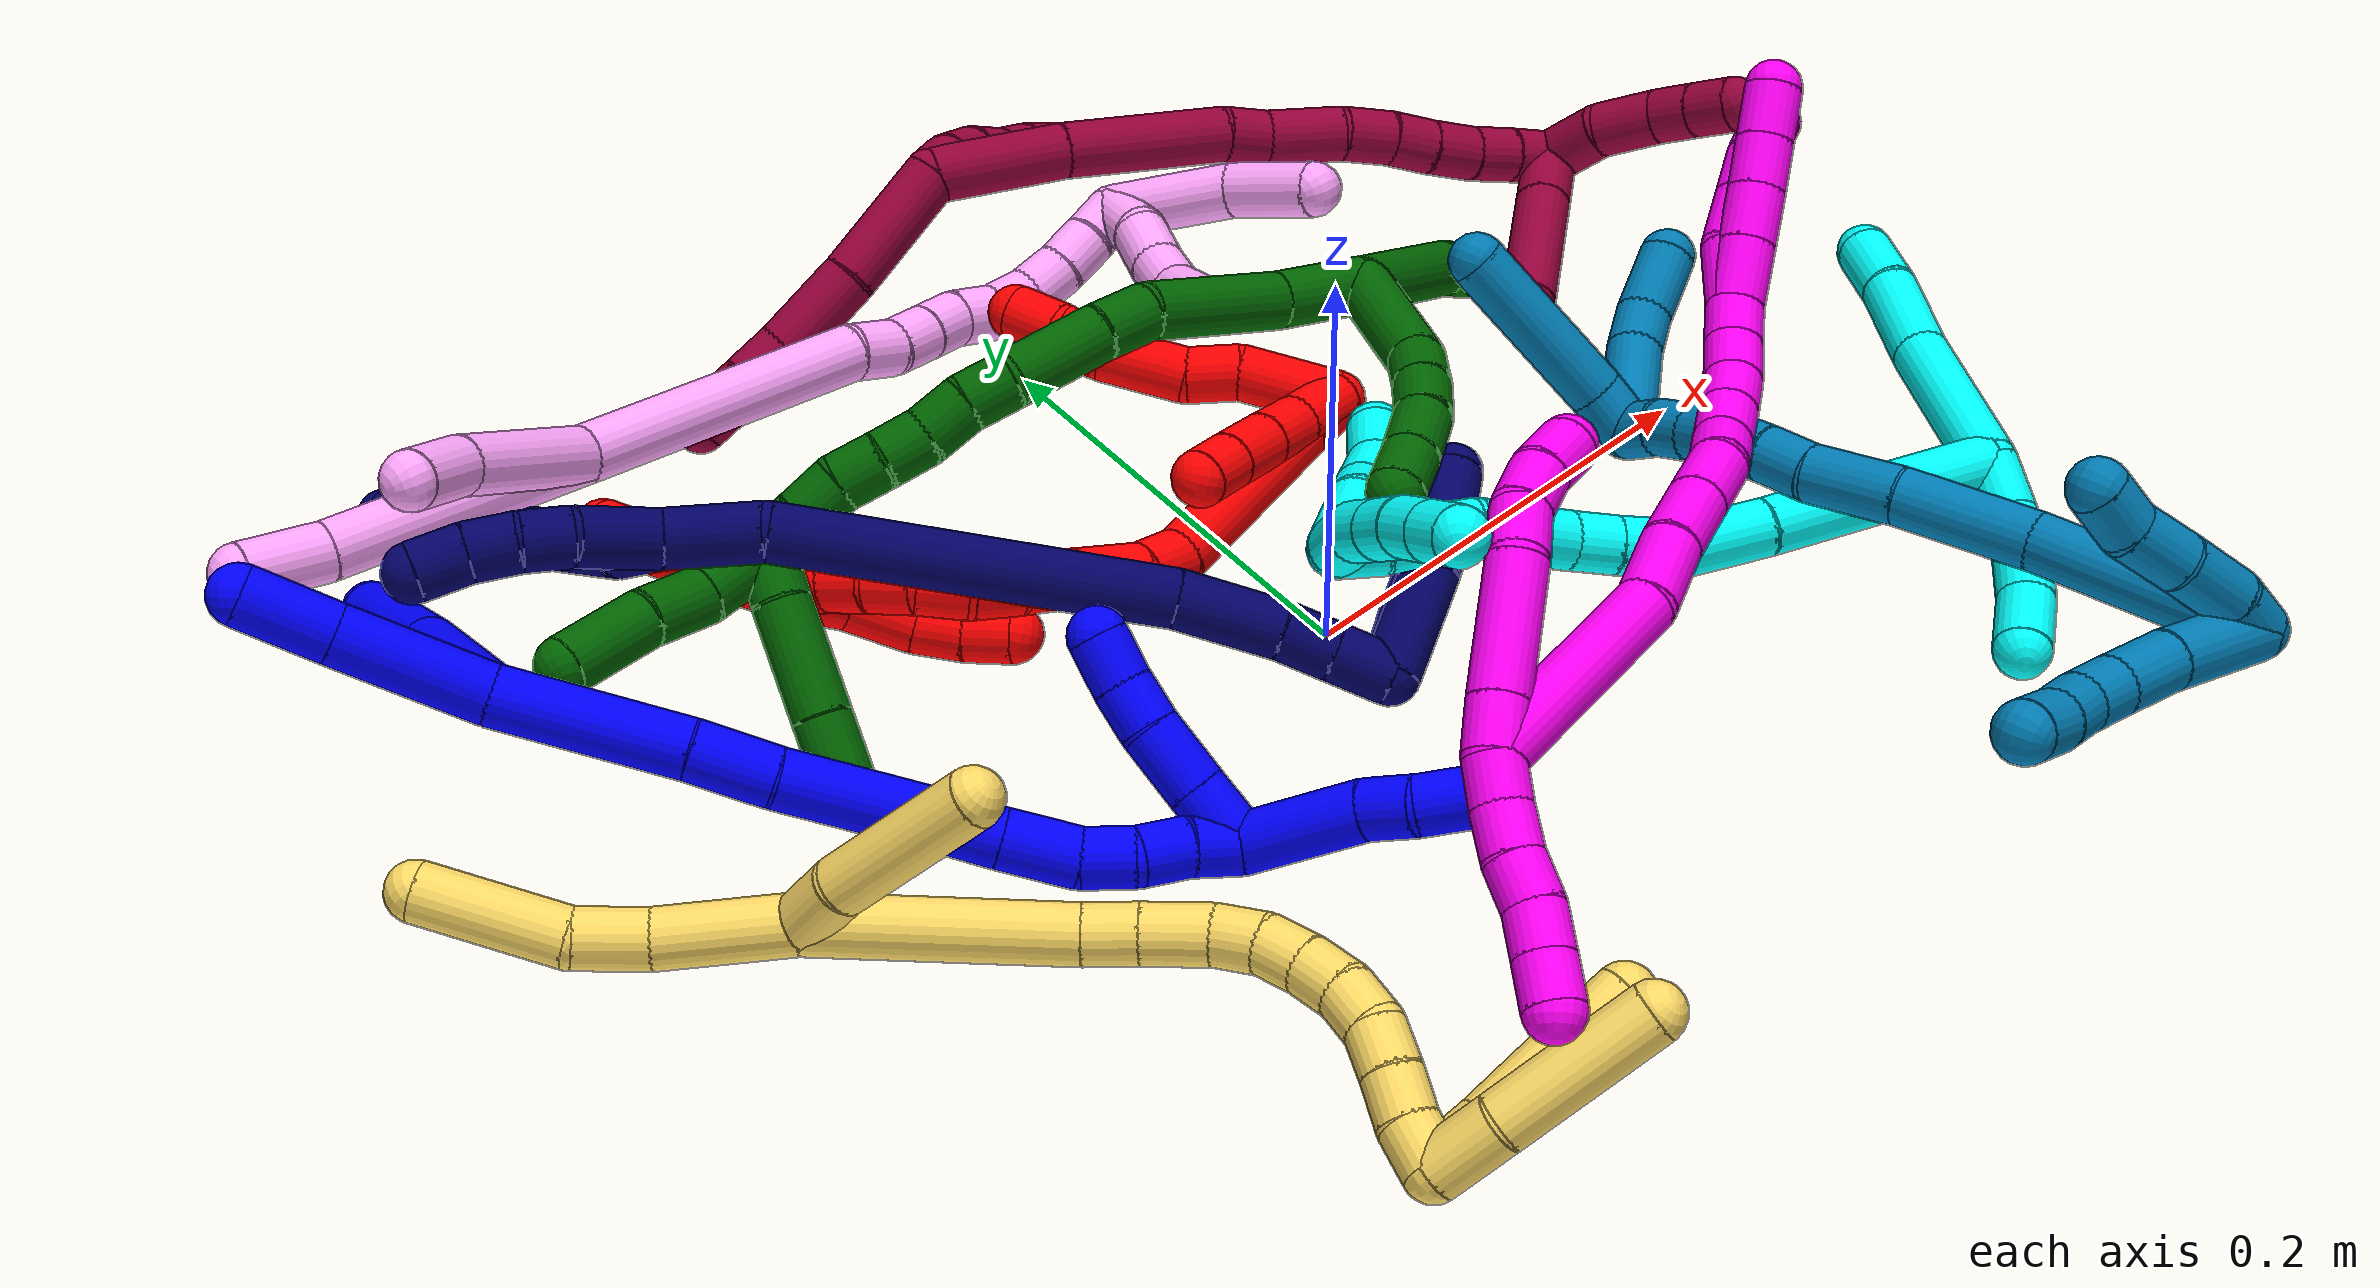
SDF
<sdf version="1.7">
 <world name="default">
  <plugin name="TubeGeneratorPlugin" filename="libtube_generator_plugin.so"/>
  <model name="photoneo_s_sensor">
   <static>1</static>
   <pose>0 0 2 1.57079 1.57079 3.14159</pose>
   <link name="link">
    <inertial><mass>0.1</mass></inertial>
    <sensor name="sensor" type="depth">
     <update_rate>30</update_rate>
     <camera>
      <horizontal_fov>1.22</horizontal_fov>
      <image><width>1920</width><height>1200</height><format>B8G8R8</format></image>
      <clip><near>0.1</near><far>4</far></clip>
      <depth_camera><output>points</output></depth_camera>
     </camera>
     <plugin name="camera_plugin" filename="libgazebo_ros_depth_camera.so">
      <baseline>0.2</baseline>
      <alwaysOn>1</alwaysOn>
      <updateRate>0.0</updateRate>
      <cameraName>camera_ir</cameraName>
      <imageTopicName>/camera/color/image_raw</imageTopicName>
      <cameraInfoTopicName>/camera/color/camera_info</cameraInfoTopicName>
      <depthImageTopicName>/camera/depth/image_raw</depthImageTopicName>
      <depthImageCameraInfoTopicName>/camera/depth/camera_info</depthImageCameraInfoTopicName>
      <pointCloudTopicName>/camera/depth/points</pointCloudTopicName>
      <frameName>fr_optical</frameName>
      <pointCloudCutoff>0.1</pointCloudCutoff>
      <pointCloudCutoffMax>2.0</pointCloudCutoffMax>
      <distortionK1>0</distortionK1>
      <distortionK2>0</distortionK2>
      <distortionK3>0</distortionK3>
      <distortionT1>0</distortionT1>
      <distortionT2>0</distortionT2>
      <CxPrime>0</CxPrime>
      <Cx>0</Cx>
      <Cy>0</Cy>
      <focalLength>0</focalLength>
      <hackBaseline>0</hackBaseline>
     </plugin>
    </sensor>
   </link>
  </model>
  <gravity>0 0 -9.8</gravity>
  <magnetic_field>6e-06 2.3e-05 -4.2e-05</magnetic_field>
  <atmosphere type="adiabatic"/>
  <physics name="default_physics" default="0" type="ode">
   <max_step_size>0.003</max_step_size>
   <real_time_factor>1</real_time_factor>
   <real_time_update_rate>1000</real_time_update_rate>
   <max_contacts>10000</max_contacts>
   <ode>
    <solver>
     <type>quick</type>
     <iters>100</iters>
     <sor>1.3</sor>
     <use_dynamic_moi_rescaling>0</use_dynamic_moi_rescaling>
    </solver>
    <constraints>
     <contact_max_correcting_vel>0</contact_max_correcting_vel>
     <contact_surface_layer>0.001</contact_surface_layer>
     <cfm>0</cfm>
     <erp>0.2</erp>
    </constraints>
   </ode>
  </physics>
  <scene><ambient>0.4 0.4 0.4 1</ambient><background>0.7 0.7 0.7 1</background><shadows>0</shadows></scene>
  <audio><device>default</device></audio>
  <spherical_coordinates>
   <surface_model>EARTH_WGS84</surface_model>
   <latitude_deg>0</latitude_deg>
   <longitude_deg>0</longitude_deg>
   <elevation>0</elevation>
   <heading_deg>0</heading_deg>
  </spherical_coordinates>
  <model name="bin">
   <static>1</static>
   <link name="bottom">
    <collision name="collision-bottom">
     <pose>0 0 -0.01 0 -0 0</pose>
     <geometry><box><size>0.8 0.6 0.02</size></box></geometry>
     <surface>
      <friction><ode><mu>100</mu><mu2>100</mu2></ode></friction>
      <contact><collide_bitmask>65535</collide_bitmask></contact>
     </surface>
    </collision>
   </link>
   <link name="west_wall">
    <collision name="collision-west_wall">
     <pose>-0.41 0 0.1 0 -0 0</pose>
     <geometry><box><size>0.02 0.6 0.2</size></box></geometry>
     <surface>
      <friction><ode><mu>100</mu><mu2>100</mu2></ode></friction>
      <contact><collide_bitmask>65535</collide_bitmask></contact>
     </surface>
    </collision>
   </link>
   <link name="east_wall">
    <collision name="collision-east_wall">
     <pose>0.41 0 0.1 0 -0 0</pose>
     <geometry><box><size>0.02 0.6 0.2</size></box></geometry>
     <surface>
      <friction><ode><mu>100</mu><mu2>100</mu2></ode></friction>
      <contact><collide_bitmask>65535</collide_bitmask></contact>
     </surface>
    </collision>
   </link>
   <link name="south_wall">
    <collision name="collision-south_wall">
     <pose>0 -0.31 0.1 0 -0 0</pose>
     <geometry><box><size>0.8 0.02 0.2</size></box></geometry>
     <surface>
      <friction><ode><mu>100</mu><mu2>100</mu2></ode></friction>
      <contact><collide_bitmask>65535</collide_bitmask></contact>
     </surface>
    </collision>
   </link>
   <link name="north_wall">
    <collision name="collision-north_wall">
     <pose>0 0.31 0.1 0 -0 0</pose>
     <geometry><box><size>0.8 0.02 0.2</size></box></geometry>
     <surface>
      <friction><ode><mu>100</mu><mu2>100</mu2></ode></friction>
      <contact><collide_bitmask>65535</collide_bitmask></contact>
     </surface>
    </collision>
   </link>
  </model>
  <model name="1">
   <static>0</static>
   <link name="1">
    <collision name="collision-cylinder-e_1_2_8">
     <pose>-0.029915 0.015747 0.020905 -0.645601 -0.85204 0.301301</pose>
     <geometry><cylinder><radius>0.0125</radius><length>0.079496</length></cylinder></geometry>
     <surface>
      <friction><ode><mu>1.16</mu><mu2>1.16</mu2><slip1>0</slip1><slip2>0</slip2></ode></friction>
      <contact><ode><kp>1e+06</kp><kd>1</kd><max_vel>0</max_vel><min_depth>0.001</min_depth></ode></contact>
     </surface>
    </collision>
    <visual name="visual-cylinder-e_1_2_8">
     <pose>-0.029915 0.015747 0.020905 -0.645601 -0.85204 0.301301</pose>
     <geometry><cylinder><radius>0.0125</radius><length>0.079496</length></cylinder></geometry>
     <material><ambient>0 0 1 1</ambient></material>
    </visual>
    <collision name="collision-cylinder-e_2_8_6">
     <pose>-0.085674 0.044643 0.061858 -0.580463 -0.822875 0.259179</pose>
     <geometry><cylinder><radius>0.0125</radius><length>0.070504</length></cylinder></geometry>
     <surface>
      <friction><ode><mu>1.16</mu><mu2>1.16</mu2><slip1>0</slip1><slip2>0</slip2></ode></friction>
      <contact><ode><kp>1e+06</kp><kd>1</kd><max_vel>0</max_vel><min_depth>0.001</min_depth></ode></contact>
     </surface>
    </collision>
    <visual name="visual-cylinder-e_2_8_6">
     <pose>-0.085674 0.044643 0.061858 -0.580463 -0.822875 0.259179</pose>
     <geometry><cylinder><radius>0.0125</radius><length>0.070504</length></cylinder></geometry>
     <material><ambient>0 0 1 1</ambient></material>
    </visual>
    <collision name="collision-cylinder-e_1_2_9">
     <pose>0.011663 0.009392 0.027526 -0.328805 0.381384 -0.064028</pose>
     <geometry><cylinder><radius>0.0125</radius><length>0.062671</length></cylinder></geometry>
     <surface>
      <friction><ode><mu>1.16</mu><mu2>1.16</mu2><slip1>0</slip1><slip2>0</slip2></ode></friction>
      <contact><ode><kp>1e+06</kp><kd>1</kd><max_vel>0</max_vel><min_depth>0.001</min_depth></ode></contact>
     </surface>
    </collision>
    <visual name="visual-cylinder-e_1_2_9">
     <pose>0.011663 0.009392 0.027526 -0.328805 0.381384 -0.064028</pose>
     <geometry><cylinder><radius>0.0125</radius><length>0.062671</length></cylinder></geometry>
     <material><ambient>0 0 1 1</ambient></material>
    </visual>
    <collision name="collision-cylinder-e_2_9_5">
     <pose>0.030401 0.024668 0.071291 -0.347682 0.388746 -0.069115</pose>
     <geometry><cylinder><radius>0.0125</radius><length>0.037329</length></cylinder></geometry>
     <surface>
      <friction><ode><mu>1.16</mu><mu2>1.16</mu2><slip1>0</slip1><slip2>0</slip2></ode></friction>
      <contact><ode><kp>1e+06</kp><kd>1</kd><max_vel>0</max_vel><min_depth>0.001</min_depth></ode></contact>
     </surface>
    </collision>
    <visual name="visual-cylinder-e_2_9_5">
     <pose>0.030401 0.024668 0.071291 -0.347682 0.388746 -0.069115</pose>
     <geometry><cylinder><radius>0.0125</radius><length>0.037329</length></cylinder></geometry>
     <material><ambient>0 0 1 1</ambient></material>
    </visual>
    <collision name="collision-cylinder-e_1_2_10">
     <pose>-0.006516 -0.009317 -0.037463 2.89785 -0.167205 -1.20006</pose>
     <geometry><cylinder><radius>0.0125</radius><length>0.0783</length></cylinder></geometry>
     <surface>
      <friction><ode><mu>1.16</mu><mu2>1.16</mu2><slip1>0</slip1><slip2>0</slip2></ode></friction>
      <contact><ode><kp>1e+06</kp><kd>1</kd><max_vel>0</max_vel><min_depth>0.001</min_depth></ode></contact>
     </surface>
    </collision>
    <visual name="visual-cylinder-e_1_2_10">
     <pose>-0.006516 -0.009317 -0.037463 2.89785 -0.167205 -1.20006</pose>
     <geometry><cylinder><radius>0.0125</radius><length>0.0783</length></cylinder></geometry>
     <material><ambient>0 0 1 1</ambient></material>
    </visual>
    <collision name="collision-cylinder-e_2_10_11">
     <pose>-0.017143 -0.023383 -0.090851 2.85172 -0.242556 -1.39143</pose>
     <geometry><cylinder><radius>0.0125</radius><length>0.034239</length></cylinder></geometry>
     <surface>
      <friction><ode><mu>1.16</mu><mu2>1.16</mu2><slip1>0</slip1><slip2>0</slip2></ode></friction>
      <contact><ode><kp>1e+06</kp><kd>1</kd><max_vel>0</max_vel><min_depth>0.001</min_depth></ode></contact>
     </surface>
    </collision>
    <visual name="visual-cylinder-e_2_10_11">
     <pose>-0.017143 -0.023383 -0.090851 2.85172 -0.242556 -1.39143</pose>
     <geometry><cylinder><radius>0.0125</radius><length>0.034239</length></cylinder></geometry>
     <material><ambient>0 0 1 1</ambient></material>
    </visual>
    <collision name="collision-cylinder-e_3_11_12">
     <pose>-0.032321 -0.034599 -0.13748 2.93404 -0.339058 -2.04837</pose>
     <geometry><cylinder><radius>0.0125</radius><length>0.066544</length></cylinder></geometry>
     <surface>
      <friction><ode><mu>1.16</mu><mu2>1.16</mu2><slip1>0</slip1><slip2>0</slip2></ode></friction>
      <contact><ode><kp>1e+06</kp><kd>1</kd><max_vel>0</max_vel><min_depth>0.001</min_depth></ode></contact>
     </surface>
    </collision>
    <visual name="visual-cylinder-e_3_11_12">
     <pose>-0.032321 -0.034599 -0.13748 2.93404 -0.339058 -2.04837</pose>
     <geometry><cylinder><radius>0.0125</radius><length>0.066544</length></cylinder></geometry>
     <material><ambient>0 0 1 1</ambient></material>
    </visual>
    <collision name="collision-cylinder-e_4_12_13">
     <pose>-0.046033 -0.043985 -0.179445 2.88788 -0.223622 -1.44369</pose>
     <geometry><cylinder><radius>0.0125</radius><length>0.023859</length></cylinder></geometry>
     <surface>
      <friction><ode><mu>1.16</mu><mu2>1.16</mu2><slip1>0</slip1><slip2>0</slip2></ode></friction>
      <contact><ode><kp>1e+06</kp><kd>1</kd><max_vel>0</max_vel><min_depth>0.001</min_depth></ode></contact>
     </surface>
    </collision>
    <visual name="visual-cylinder-e_4_12_13">
     <pose>-0.046033 -0.043985 -0.179445 2.88788 -0.223622 -1.44369</pose>
     <geometry><cylinder><radius>0.0125</radius><length>0.023859</length></cylinder></geometry>
     <material><ambient>0 0 1 1</ambient></material>
    </visual>
    <collision name="collision-cylinder-e_5_13_14">
     <pose>-0.051768 -0.050335 -0.206055 2.92175 -0.193927 -1.44478</pose>
     <geometry><cylinder><radius>0.0125</radius><length>0.032059</length></cylinder></geometry>
     <surface>
      <friction><ode><mu>1.16</mu><mu2>1.16</mu2><slip1>0</slip1><slip2>0</slip2></ode></friction>
      <contact><ode><kp>1e+06</kp><kd>1</kd><max_vel>0</max_vel><min_depth>0.001</min_depth></ode></contact>
     </surface>
    </collision>
    <visual name="visual-cylinder-e_5_13_14">
     <pose>-0.051768 -0.050335 -0.206055 2.92175 -0.193927 -1.44478</pose>
     <geometry><cylinder><radius>0.0125</radius><length>0.032059</length></cylinder></geometry>
     <material><ambient>0 0 1 1</ambient></material>
    </visual>
    <collision name="collision-cylinder-e_6_14_15">
     <pose>-0.055504 -0.05338 -0.232438 -3.10674 -0.05859 2.06838</pose>
     <geometry><cylinder><radius>0.0125</radius><length>0.022116</length></cylinder></geometry>
     <surface>
      <friction><ode><mu>1.16</mu><mu2>1.16</mu2><slip1>0</slip1><slip2>0</slip2></ode></friction>
      <contact><ode><kp>1e+06</kp><kd>1</kd><max_vel>0</max_vel><min_depth>0.001</min_depth></ode></contact>
     </surface>
    </collision>
    <visual name="visual-cylinder-e_6_14_15">
     <pose>-0.055504 -0.05338 -0.232438 -3.10674 -0.05859 2.06838</pose>
     <geometry><cylinder><radius>0.0125</radius><length>0.022116</length></cylinder></geometry>
     <material><ambient>0 0 1 1</ambient></material>
    </visual>
    <collision name="collision-cylinder-e_7_15_16">
     <pose>-0.059526 -0.050392 -0.253192 -2.87989 -0.323451 1.78405</pose>
     <geometry><cylinder><radius>0.0125</radius><length>0.02123</length></cylinder></geometry>
     <surface>
      <friction><ode><mu>1.16</mu><mu2>1.16</mu2><slip1>0</slip1><slip2>0</slip2></ode></friction>
      <contact><ode><kp>1e+06</kp><kd>1</kd><max_vel>0</max_vel><min_depth>0.001</min_depth></ode></contact>
     </surface>
    </collision>
    <visual name="visual-cylinder-e_7_15_16">
     <pose>-0.059526 -0.050392 -0.253192 -2.87989 -0.323451 1.78405</pose>
     <geometry><cylinder><radius>0.0125</radius><length>0.02123</length></cylinder></geometry>
     <material><ambient>0 0 1 1</ambient></material>
    </visual>
    <collision name="collision-cylinder-e_8_16_1">
     <pose>-0.066859 -0.04672 -0.272933 -3.03539 -0.374427 2.59448</pose>
     <geometry><cylinder><radius>0.0125</radius><length>0.021653</length></cylinder></geometry>
     <surface>
      <friction><ode><mu>1.16</mu><mu2>1.16</mu2><slip1>0</slip1><slip2>0</slip2></ode></friction>
      <contact><ode><kp>1e+06</kp><kd>1</kd><max_vel>0</max_vel><min_depth>0.001</min_depth></ode></contact>
     </surface>
    </collision>
    <visual name="visual-cylinder-e_8_16_1">
     <pose>-0.066859 -0.04672 -0.272933 -3.03539 -0.374427 2.59448</pose>
     <geometry><cylinder><radius>0.0125</radius><length>0.021653</length></cylinder></geometry>
     <material><ambient>0 0 1 1</ambient></material>
    </visual>
    <collision name="collision-cylinder-e_1_1_17">
     <pose>-0.061743 -0.040176 -0.307669 -2.92359 0.344227 -2.01786</pose>
     <geometry><cylinder><radius>0.0125</radius><length>0.053786</length></cylinder></geometry>
     <surface>
      <friction><ode><mu>1.16</mu><mu2>1.16</mu2><slip1>0</slip1><slip2>0</slip2></ode></friction>
      <contact><ode><kp>1e+06</kp><kd>1</kd><max_vel>0</max_vel><min_depth>0.001</min_depth></ode></contact>
     </surface>
    </collision>
    <visual name="visual-cylinder-e_1_1_17">
     <pose>-0.061743 -0.040176 -0.307669 -2.92359 0.344227 -2.01786</pose>
     <geometry><cylinder><radius>0.0125</radius><length>0.053786</length></cylinder></geometry>
     <material><ambient>0 0 1 1</ambient></material>
    </visual>
    <collision name="collision-cylinder-e_2_17_18">
     <pose>-0.048302 -0.034663 -0.342479 -3.13782 0.408232 -3.12335</pose>
     <geometry><cylinder><radius>0.0125</radius><length>0.021995</length></cylinder></geometry>
     <surface>
      <friction><ode><mu>1.16</mu><mu2>1.16</mu2><slip1>0</slip1><slip2>0</slip2></ode></friction>
      <contact><ode><kp>1e+06</kp><kd>1</kd><max_vel>0</max_vel><min_depth>0.001</min_depth></ode></contact>
     </surface>
    </collision>
    <visual name="visual-cylinder-e_2_17_18">
     <pose>-0.048302 -0.034663 -0.342479 -3.13782 0.408232 -3.12335</pose>
     <geometry><cylinder><radius>0.0125</radius><length>0.021995</length></cylinder></geometry>
     <material><ambient>0 0 1 1</ambient></material>
    </visual>
    <collision name="collision-cylinder-e_3_18_4">
     <pose>-0.041764 -0.033033 -0.364379 -3.00759 0.180365 -1.86479</pose>
     <geometry><cylinder><radius>0.0125</radius><length>0.024219</length></cylinder></geometry>
     <surface>
      <friction><ode><mu>1.16</mu><mu2>1.16</mu2><slip1>0</slip1><slip2>0</slip2></ode></friction>
      <contact><ode><kp>1e+06</kp><kd>1</kd><max_vel>0</max_vel><min_depth>0.001</min_depth></ode></contact>
     </surface>
    </collision>
    <visual name="visual-cylinder-e_3_18_4">
     <pose>-0.041764 -0.033033 -0.364379 -3.00759 0.180365 -1.86479</pose>
     <geometry><cylinder><radius>0.0125</radius><length>0.024219</length></cylinder></geometry>
     <material><ambient>0 0 1 1</ambient></material>
    </visual>
    <collision name="collision-cylinder-e_1_1_19">
     <pose>-0.068661 -0.034897 -0.274114 -0.882801 0.153756 -0.07276</pose>
     <geometry><cylinder><radius>0.0125</radius><length>0.028174</length></cylinder></geometry>
     <surface>
      <friction><ode><mu>1.16</mu><mu2>1.16</mu2><slip1>0</slip1><slip2>0</slip2></ode></friction>
      <contact><ode><kp>1e+06</kp><kd>1</kd><max_vel>0</max_vel><min_depth>0.001</min_depth></ode></contact>
     </surface>
    </collision>
    <visual name="visual-cylinder-e_1_1_19">
     <pose>-0.068661 -0.034897 -0.274114 -0.882801 0.153756 -0.07276</pose>
     <geometry><cylinder><radius>0.0125</radius><length>0.028174</length></cylinder></geometry>
     <material><ambient>0 0 1 1</ambient></material>
    </visual>
    <collision name="collision-cylinder-e_2_19_20">
     <pose>-0.063879 -0.012691 -0.256122 -0.896563 0.177182 -0.085385</pose>
     <geometry><cylinder><radius>0.0125</radius><length>0.029786</length></cylinder></geometry>
     <surface>
      <friction><ode><mu>1.16</mu><mu2>1.16</mu2><slip1>0</slip1><slip2>0</slip2></ode></friction>
      <contact><ode><kp>1e+06</kp><kd>1</kd><max_vel>0</max_vel><min_depth>0.001</min_depth></ode></contact>
     </surface>
    </collision>
    <visual name="visual-cylinder-e_2_19_20">
     <pose>-0.063879 -0.012691 -0.256122 -0.896563 0.177182 -0.085385</pose>
     <geometry><cylinder><radius>0.0125</radius><length>0.029786</length></cylinder></geometry>
     <material><ambient>0 0 1 1</ambient></material>
    </visual>
    <collision name="collision-cylinder-e_3_20_21">
     <pose>-0.060446 0.007303 -0.241547 -1.00514 0.079702 -0.043824</pose>
     <geometry><cylinder><radius>0.0125</radius><length>0.020299</length></cylinder></geometry>
     <surface>
      <friction><ode><mu>1.16</mu><mu2>1.16</mu2><slip1>0</slip1><slip2>0</slip2></ode></friction>
      <contact><ode><kp>1e+06</kp><kd>1</kd><max_vel>0</max_vel><min_depth>0.001</min_depth></ode></contact>
     </surface>
    </collision>
    <visual name="visual-cylinder-e_3_20_21">
     <pose>-0.060446 0.007303 -0.241547 -1.00514 0.079702 -0.043824</pose>
     <geometry><cylinder><radius>0.0125</radius><length>0.020299</length></cylinder></geometry>
     <material><ambient>0 0 1 1</ambient></material>
    </visual>
    <collision name="collision-cylinder-e_4_21_3">
     <pose>-0.05765 0.025302 -0.231148 -1.08645 0.183896 -0.111239</pose>
     <geometry><cylinder><radius>0.0125</radius><length>0.02174</length></cylinder></geometry>
     <surface>
      <friction><ode><mu>1.16</mu><mu2>1.16</mu2><slip1>0</slip1><slip2>0</slip2></ode></friction>
      <contact><ode><kp>1e+06</kp><kd>1</kd><max_vel>0</max_vel><min_depth>0.001</min_depth></ode></contact>
     </surface>
    </collision>
    <visual name="visual-cylinder-e_4_21_3">
     <pose>-0.05765 0.025302 -0.231148 -1.08645 0.183896 -0.111239</pose>
     <geometry><cylinder><radius>0.0125</radius><length>0.02174</length></cylinder></geometry>
     <material><ambient>0 0 1 1</ambient></material>
    </visual>
    <collision name="collision-sphere-3">
     <pose>-0.055662 0.03476 -0.226172 0 -0 0</pose>
     <geometry><sphere><radius>0.0125</radius></sphere></geometry>
     <surface>
      <friction><ode><mu>1.16</mu><mu2>1.16</mu2><slip1>0</slip1><slip2>0</slip2></ode></friction>
      <contact><ode><kp>1e+06</kp><kd>1</kd><max_vel>0</max_vel><min_depth>0.001</min_depth></ode></contact>
     </surface>
    </collision>
    <visual name="visual-sphere-3">
     <pose>-0.055662 0.03476 -0.226172 0 -0 0</pose>
     <geometry><sphere><radius>0.0125</radius></sphere></geometry>
     <material><ambient>0 0 1 1</ambient></material>
    </visual>
    <collision name="collision-sphere-21">
     <pose>-0.059638 0.015845 -0.236124 0 -0 0</pose>
     <geometry><sphere><radius>0.0125</radius></sphere></geometry>
     <surface>
      <friction><ode><mu>1.16</mu><mu2>1.16</mu2><slip1>0</slip1><slip2>0</slip2></ode></friction>
      <contact><ode><kp>1e+06</kp><kd>1</kd><max_vel>0</max_vel><min_depth>0.001</min_depth></ode></contact>
     </surface>
    </collision>
    <visual name="visual-sphere-21">
     <pose>-0.059638 0.015845 -0.236124 0 -0 0</pose>
     <geometry><sphere><radius>0.0125</radius></sphere></geometry>
     <material><ambient>0 0 1 1</ambient></material>
    </visual>
    <collision name="collision-sphere-20">
     <pose>-0.061254 -0.001238 -0.246969 0 -0 0</pose>
     <geometry><sphere><radius>0.0125</radius></sphere></geometry>
     <surface>
      <friction><ode><mu>1.16</mu><mu2>1.16</mu2><slip1>0</slip1><slip2>0</slip2></ode></friction>
      <contact><ode><kp>1e+06</kp><kd>1</kd><max_vel>0</max_vel><min_depth>0.001</min_depth></ode></contact>
     </surface>
    </collision>
    <visual name="visual-sphere-20">
     <pose>-0.061254 -0.001238 -0.246969 0 -0 0</pose>
     <geometry><sphere><radius>0.0125</radius></sphere></geometry>
     <material><ambient>0 0 1 1</ambient></material>
    </visual>
    <collision name="collision-sphere-19">
     <pose>-0.066504 -0.024143 -0.265274 0 -0 0</pose>
     <geometry><sphere><radius>0.0125</radius></sphere></geometry>
     <surface>
      <friction><ode><mu>1.16</mu><mu2>1.16</mu2><slip1>0</slip1><slip2>0</slip2></ode></friction>
      <contact><ode><kp>1e+06</kp><kd>1</kd><max_vel>0</max_vel><min_depth>0.001</min_depth></ode></contact>
     </surface>
    </collision>
    <visual name="visual-sphere-19">
     <pose>-0.066504 -0.024143 -0.265274 0 -0 0</pose>
     <geometry><sphere><radius>0.0125</radius></sphere></geometry>
     <material><ambient>0 0 1 1</ambient></material>
    </visual>
    <collision name="collision-sphere-10">
     <pose>-0.013031 -0.018633 -0.074926 0 -0 0</pose>
     <geometry><sphere><radius>0.0125</radius></sphere></geometry>
     <surface>
      <friction><ode><mu>1.16</mu><mu2>1.16</mu2><slip1>0</slip1><slip2>0</slip2></ode></friction>
      <contact><ode><kp>1e+06</kp><kd>1</kd><max_vel>0</max_vel><min_depth>0.001</min_depth></ode></contact>
     </surface>
    </collision>
    <visual name="visual-sphere-10">
     <pose>-0.013031 -0.018633 -0.074926 0 -0 0</pose>
     <geometry><sphere><radius>0.0125</radius></sphere></geometry>
     <material><ambient>0 0 1 1</ambient></material>
    </visual>
    <collision name="collision-sphere-5">
     <pose>0.037475 0.030553 0.087529 0 -0 0</pose>
     <geometry><sphere><radius>0.0125</radius></sphere></geometry>
     <surface>
      <friction><ode><mu>1.16</mu><mu2>1.16</mu2><slip1>0</slip1><slip2>0</slip2></ode></friction>
      <contact><ode><kp>1e+06</kp><kd>1</kd><max_vel>0</max_vel><min_depth>0.001</min_depth></ode></contact>
     </surface>
    </collision>
    <visual name="visual-sphere-5">
     <pose>0.037475 0.030553 0.087529 0 -0 0</pose>
     <geometry><sphere><radius>0.0125</radius></sphere></geometry>
     <material><ambient>0 0 1 1</ambient></material>
    </visual>
    <collision name="collision-sphere-6">
     <pose>-0.111517 0.057791 0.081906 0 -0 0</pose>
     <geometry><sphere><radius>0.0125</radius></sphere></geometry>
     <surface>
      <friction><ode><mu>1.16</mu><mu2>1.16</mu2><slip1>0</slip1><slip2>0</slip2></ode></friction>
      <contact><ode><kp>1e+06</kp><kd>1</kd><max_vel>0</max_vel><min_depth>0.001</min_depth></ode></contact>
     </surface>
    </collision>
    <visual name="visual-sphere-6">
     <pose>-0.111517 0.057791 0.081906 0 -0 0</pose>
     <geometry><sphere><radius>0.0125</radius></sphere></geometry>
     <material><ambient>0 0 1 1</ambient></material>
    </visual>
    <collision name="collision-sphere-9">
     <pose>0.023327 0.018783 0.055052 0 -0 0</pose>
     <geometry><sphere><radius>0.0125</radius></sphere></geometry>
     <surface>
      <friction><ode><mu>1.16</mu><mu2>1.16</mu2><slip1>0</slip1><slip2>0</slip2></ode></friction>
      <contact><ode><kp>1e+06</kp><kd>1</kd><max_vel>0</max_vel><min_depth>0.001</min_depth></ode></contact>
     </surface>
    </collision>
    <visual name="visual-sphere-9">
     <pose>0.023327 0.018783 0.055052 0 -0 0</pose>
     <geometry><sphere><radius>0.0125</radius></sphere></geometry>
     <material><ambient>0 0 1 1</ambient></material>
    </visual>
    <collision name="collision-sphere-2">
     <geometry><sphere><radius>0.0125</radius></sphere></geometry>
     <surface>
      <friction><ode><mu>1.16</mu><mu2>1.16</mu2><slip1>0</slip1><slip2>0</slip2></ode></friction>
      <contact><ode><kp>1e+06</kp><kd>1</kd><max_vel>0</max_vel><min_depth>0.001</min_depth></ode></contact>
     </surface>
    </collision>
    <visual name="visual-sphere-2">
     <geometry><sphere><radius>0.0125</radius></sphere></geometry>
     <material><ambient>0 0 1 1</ambient></material>
    </visual>
    <collision name="collision-sphere-8">
     <pose>-0.059831 0.031494 0.041809 0 -0 0</pose>
     <geometry><sphere><radius>0.0125</radius></sphere></geometry>
     <surface>
      <friction><ode><mu>1.16</mu><mu2>1.16</mu2><slip1>0</slip1><slip2>0</slip2></ode></friction>
      <contact><ode><kp>1e+06</kp><kd>1</kd><max_vel>0</max_vel><min_depth>0.001</min_depth></ode></contact>
     </surface>
    </collision>
    <visual name="visual-sphere-8">
     <pose>-0.059831 0.031494 0.041809 0 -0 0</pose>
     <geometry><sphere><radius>0.0125</radius></sphere></geometry>
     <material><ambient>0 0 1 1</ambient></material>
    </visual>
    <collision name="collision-sphere-11">
     <pose>-0.021255 -0.028133 -0.106776 0 -0 0</pose>
     <geometry><sphere><radius>0.0125</radius></sphere></geometry>
     <surface>
      <friction><ode><mu>1.16</mu><mu2>1.16</mu2><slip1>0</slip1><slip2>0</slip2></ode></friction>
      <contact><ode><kp>1e+06</kp><kd>1</kd><max_vel>0</max_vel><min_depth>0.001</min_depth></ode></contact>
     </surface>
    </collision>
    <visual name="visual-sphere-11">
     <pose>-0.021255 -0.028133 -0.106776 0 -0 0</pose>
     <geometry><sphere><radius>0.0125</radius></sphere></geometry>
     <material><ambient>0 0 1 1</ambient></material>
    </visual>
    <collision name="collision-sphere-12">
     <pose>-0.043387 -0.041065 -0.168185 0 -0 0</pose>
     <geometry><sphere><radius>0.0125</radius></sphere></geometry>
     <surface>
      <friction><ode><mu>1.16</mu><mu2>1.16</mu2><slip1>0</slip1><slip2>0</slip2></ode></friction>
      <contact><ode><kp>1e+06</kp><kd>1</kd><max_vel>0</max_vel><min_depth>0.001</min_depth></ode></contact>
     </surface>
    </collision>
    <visual name="visual-sphere-12">
     <pose>-0.043387 -0.041065 -0.168185 0 -0 0</pose>
     <geometry><sphere><radius>0.0125</radius></sphere></geometry>
     <material><ambient>0 0 1 1</ambient></material>
    </visual>
    <collision name="collision-sphere-13">
     <pose>-0.048678 -0.046905 -0.190705 0 -0 0</pose>
     <geometry><sphere><radius>0.0125</radius></sphere></geometry>
     <surface>
      <friction><ode><mu>1.16</mu><mu2>1.16</mu2><slip1>0</slip1><slip2>0</slip2></ode></friction>
      <contact><ode><kp>1e+06</kp><kd>1</kd><max_vel>0</max_vel><min_depth>0.001</min_depth></ode></contact>
     </surface>
    </collision>
    <visual name="visual-sphere-13">
     <pose>-0.048678 -0.046905 -0.190705 0 -0 0</pose>
     <geometry><sphere><radius>0.0125</radius></sphere></geometry>
     <material><ambient>0 0 1 1</ambient></material>
    </visual>
    <collision name="collision-sphere-14">
     <pose>-0.054857 -0.053765 -0.221406 0 -0 0</pose>
     <geometry><sphere><radius>0.0125</radius></sphere></geometry>
     <surface>
      <friction><ode><mu>1.16</mu><mu2>1.16</mu2><slip1>0</slip1><slip2>0</slip2></ode></friction>
      <contact><ode><kp>1e+06</kp><kd>1</kd><max_vel>0</max_vel><min_depth>0.001</min_depth></ode></contact>
     </surface>
    </collision>
    <visual name="visual-sphere-14">
     <pose>-0.054857 -0.053765 -0.221406 0 -0 0</pose>
     <geometry><sphere><radius>0.0125</radius></sphere></geometry>
     <material><ambient>0 0 1 1</ambient></material>
    </visual>
    <collision name="collision-sphere-15">
     <pose>-0.056152 -0.052996 -0.24347 0 -0 0</pose>
     <geometry><sphere><radius>0.0125</radius></sphere></geometry>
     <surface>
      <friction><ode><mu>1.16</mu><mu2>1.16</mu2><slip1>0</slip1><slip2>0</slip2></ode></friction>
      <contact><ode><kp>1e+06</kp><kd>1</kd><max_vel>0</max_vel><min_depth>0.001</min_depth></ode></contact>
     </surface>
    </collision>
    <visual name="visual-sphere-15">
     <pose>-0.056152 -0.052996 -0.24347 0 -0 0</pose>
     <geometry><sphere><radius>0.0125</radius></sphere></geometry>
     <material><ambient>0 0 1 1</ambient></material>
    </visual>
    <collision name="collision-sphere-16">
     <pose>-0.062899 -0.047788 -0.262914 0 -0 0</pose>
     <geometry><sphere><radius>0.0125</radius></sphere></geometry>
     <surface>
      <friction><ode><mu>1.16</mu><mu2>1.16</mu2><slip1>0</slip1><slip2>0</slip2></ode></friction>
      <contact><ode><kp>1e+06</kp><kd>1</kd><max_vel>0</max_vel><min_depth>0.001</min_depth></ode></contact>
     </surface>
    </collision>
    <visual name="visual-sphere-16">
     <pose>-0.062899 -0.047788 -0.262914 0 -0 0</pose>
     <geometry><sphere><radius>0.0125</radius></sphere></geometry>
     <material><ambient>0 0 1 1</ambient></material>
    </visual>
    <collision name="collision-sphere-1">
     <pose>-0.070819 -0.045651 -0.282953 0 -0 0</pose>
     <geometry><sphere><radius>0.0125</radius></sphere></geometry>
     <surface>
      <friction><ode><mu>1.16</mu><mu2>1.16</mu2><slip1>0</slip1><slip2>0</slip2></ode></friction>
      <contact><ode><kp>1e+06</kp><kd>1</kd><max_vel>0</max_vel><min_depth>0.001</min_depth></ode></contact>
     </surface>
    </collision>
    <visual name="visual-sphere-1">
     <pose>-0.070819 -0.045651 -0.282953 0 -0 0</pose>
     <geometry><sphere><radius>0.0125</radius></sphere></geometry>
     <material><ambient>0 0 1 1</ambient></material>
    </visual>
    <collision name="collision-sphere-18">
     <pose>-0.043936 -0.034624 -0.352573 0 -0 0</pose>
     <geometry><sphere><radius>0.0125</radius></sphere></geometry>
     <surface>
      <friction><ode><mu>1.16</mu><mu2>1.16</mu2><slip1>0</slip1><slip2>0</slip2></ode></friction>
      <contact><ode><kp>1e+06</kp><kd>1</kd><max_vel>0</max_vel><min_depth>0.001</min_depth></ode></contact>
     </surface>
    </collision>
    <visual name="visual-sphere-18">
     <pose>-0.043936 -0.034624 -0.352573 0 -0 0</pose>
     <geometry><sphere><radius>0.0125</radius></sphere></geometry>
     <material><ambient>0 0 1 1</ambient></material>
    </visual>
    <collision name="collision-sphere-17">
     <pose>-0.052668 -0.034701 -0.332386 0 -0 0</pose>
     <geometry><sphere><radius>0.0125</radius></sphere></geometry>
     <surface>
      <friction><ode><mu>1.16</mu><mu2>1.16</mu2><slip1>0</slip1><slip2>0</slip2></ode></friction>
      <contact><ode><kp>1e+06</kp><kd>1</kd><max_vel>0</max_vel><min_depth>0.001</min_depth></ode></contact>
     </surface>
    </collision>
    <visual name="visual-sphere-17">
     <pose>-0.052668 -0.034701 -0.332386 0 -0 0</pose>
     <geometry><sphere><radius>0.0125</radius></sphere></geometry>
     <material><ambient>0 0 1 1</ambient></material>
    </visual>
    <collision name="collision-sphere-4">
     <pose>-0.039591 -0.031441 -0.376186 0 -0 0</pose>
     <geometry><sphere><radius>0.0125</radius></sphere></geometry>
     <surface>
      <friction><ode><mu>1.16</mu><mu2>1.16</mu2><slip1>0</slip1><slip2>0</slip2></ode></friction>
      <contact><ode><kp>1e+06</kp><kd>1</kd><max_vel>0</max_vel><min_depth>0.001</min_depth></ode></contact>
     </surface>
    </collision>
    <visual name="visual-sphere-4">
     <pose>-0.039591 -0.031441 -0.376186 0 -0 0</pose>
     <geometry><sphere><radius>0.0125</radius></sphere></geometry>
     <material><ambient>0 0 1 1</ambient></material>
    </visual>
    <inertial>
     <pose>-0.037613 -0.01098 -0.120377 0 -0 0</pose>
     <mass>0.75</mass>
     <inertia><ixx>0</ixx><ixy>0</ixy><ixz>0</ixz><iyy>5.3e-05</iyy><iyz>0</iyz><izz>1.5e-05</izz></inertia>
    </inertial>
   </link>
   <pose>-0.309119 0.135326 0.082994 1.65279 -1.06345 -2.39699</pose>
  </model>
  <model name="2">
   <static>0</static>
   <link name="2">
    <collision name="collision-cylinder-e_1_2_8">
     <pose>-0.0006 0.009678 0.019788 -0.454863 -0.027252 0.006307</pose>
     <geometry><cylinder><radius>0.0125</radius><length>0.044072</length></cylinder></geometry>
     <surface>
      <friction><ode><mu>1.16</mu><mu2>1.16</mu2><slip1>0</slip1><slip2>0</slip2></ode></friction>
      <contact><ode><kp>1e+06</kp><kd>1</kd><max_vel>0</max_vel><min_depth>0.001</min_depth></ode></contact>
     </surface>
    </collision>
    <visual name="visual-cylinder-e_1_2_8">
     <pose>-0.0006 0.009678 0.019788 -0.454863 -0.027252 0.006307</pose>
     <geometry><cylinder><radius>0.0125</radius><length>0.044072</length></cylinder></geometry>
     <material><ambient>1 0 0 1</ambient></material>
    </visual>
    <collision name="collision-cylinder-e_2_8_9">
     <pose>-0.004984 0.022444 0.050459 -0.276574 -0.322746 0.045305</pose>
     <geometry><cylinder><radius>0.0125</radius><length>0.023856</length></cylinder></geometry>
     <surface>
      <friction><ode><mu>1.16</mu><mu2>1.16</mu2><slip1>0</slip1><slip2>0</slip2></ode></friction>
      <contact><ode><kp>1e+06</kp><kd>1</kd><max_vel>0</max_vel><min_depth>0.001</min_depth></ode></contact>
     </surface>
    </collision>
    <visual name="visual-cylinder-e_2_8_9">
     <pose>-0.004984 0.022444 0.050459 -0.276574 -0.322746 0.045305</pose>
     <geometry><cylinder><radius>0.0125</radius><length>0.023856</length></cylinder></geometry>
     <material><ambient>1 0 0 1</ambient></material>
    </visual>
    <collision name="collision-cylinder-e_3_9_10">
     <pose>-0.00917 0.032739 0.079033 -0.386769 -0.021063 0.004125</pose>
     <geometry><cylinder><radius>0.0125</radius><length>0.038216</length></cylinder></geometry>
     <surface>
      <friction><ode><mu>1.16</mu><mu2>1.16</mu2><slip1>0</slip1><slip2>0</slip2></ode></friction>
      <contact><ode><kp>1e+06</kp><kd>1</kd><max_vel>0</max_vel><min_depth>0.001</min_depth></ode></contact>
     </surface>
    </collision>
    <visual name="visual-cylinder-e_3_9_10">
     <pose>-0.00917 0.032739 0.079033 -0.386769 -0.021063 0.004125</pose>
     <geometry><cylinder><radius>0.0125</radius><length>0.038216</length></cylinder></geometry>
     <material><ambient>1 0 0 1</ambient></material>
    </visual>
    <collision name="collision-cylinder-e_4_10_11">
     <pose>-0.007635 0.045069 0.105794 -0.514315 0.18385 -0.048476</pose>
     <geometry><cylinder><radius>0.0125</radius><length>0.021188</length></cylinder></geometry>
     <surface>
      <friction><ode><mu>1.16</mu><mu2>1.16</mu2><slip1>0</slip1><slip2>0</slip2></ode></friction>
      <contact><ode><kp>1e+06</kp><kd>1</kd><max_vel>0</max_vel><min_depth>0.001</min_depth></ode></contact>
     </surface>
    </collision>
    <visual name="visual-cylinder-e_4_10_11">
     <pose>-0.007635 0.045069 0.105794 -0.514315 0.18385 -0.048476</pose>
     <geometry><cylinder><radius>0.0125</radius><length>0.021188</length></cylinder></geometry>
     <material><ambient>1 0 0 1</ambient></material>
    </visual>
    <collision name="collision-cylinder-e_5_11_6">
     <pose>-0.005253 0.057787 0.123264 -0.734954 0.039358 -0.015153</pose>
     <geometry><cylinder><radius>0.0125</radius><length>0.022668</length></cylinder></geometry>
     <surface>
      <friction><ode><mu>1.16</mu><mu2>1.16</mu2><slip1>0</slip1><slip2>0</slip2></ode></friction>
      <contact><ode><kp>1e+06</kp><kd>1</kd><max_vel>0</max_vel><min_depth>0.001</min_depth></ode></contact>
     </surface>
    </collision>
    <visual name="visual-cylinder-e_5_11_6">
     <pose>-0.005253 0.057787 0.123264 -0.734954 0.039358 -0.015153</pose>
     <geometry><cylinder><radius>0.0125</radius><length>0.022668</length></cylinder></geometry>
     <material><ambient>1 0 0 1</ambient></material>
    </visual>
    <collision name="collision-cylinder-e_1_2_12">
     <pose>-0.005519 -0.008826 0.010967 0.677625 -0.373642 -0.133029</pose>
     <geometry><cylinder><radius>0.0125</radius><length>0.030241</length></cylinder></geometry>
     <surface>
      <friction><ode><mu>1.16</mu><mu2>1.16</mu2><slip1>0</slip1><slip2>0</slip2></ode></friction>
      <contact><ode><kp>1e+06</kp><kd>1</kd><max_vel>0</max_vel><min_depth>0.001</min_depth></ode></contact>
     </surface>
    </collision>
    <visual name="visual-cylinder-e_1_2_12">
     <pose>-0.005519 -0.008826 0.010967 0.677625 -0.373642 -0.133029</pose>
     <geometry><cylinder><radius>0.0125</radius><length>0.030241</length></cylinder></geometry>
     <material><ambient>1 0 0 1</ambient></material>
    </visual>
    <collision name="collision-cylinder-e_2_12_13">
     <pose>-0.014712 -0.024919 0.030553 0.700548 -0.314995 -0.115911</pose>
     <geometry><cylinder><radius>0.0125</radius><length>0.023716</length></cylinder></geometry>
     <surface>
      <friction><ode><mu>1.16</mu><mu2>1.16</mu2><slip1>0</slip1><slip2>0</slip2></ode></friction>
      <contact><ode><kp>1e+06</kp><kd>1</kd><max_vel>0</max_vel><min_depth>0.001</min_depth></ode></contact>
     </surface>
    </collision>
    <visual name="visual-cylinder-e_2_12_13">
     <pose>-0.014712 -0.024919 0.030553 0.700548 -0.314995 -0.115911</pose>
     <geometry><cylinder><radius>0.0125</radius><length>0.023716</length></cylinder></geometry>
     <material><ambient>1 0 0 1</ambient></material>
    </visual>
    <collision name="collision-cylinder-e_3_13_14">
     <pose>-0.022573 -0.040021 0.048424 0.702633 -0.332555 -0.122869</pose>
     <geometry><cylinder><radius>0.0125</radius><length>0.025651</length></cylinder></geometry>
     <surface>
      <friction><ode><mu>1.16</mu><mu2>1.16</mu2><slip1>0</slip1><slip2>0</slip2></ode></friction>
      <contact><ode><kp>1e+06</kp><kd>1</kd><max_vel>0</max_vel><min_depth>0.001</min_depth></ode></contact>
     </surface>
    </collision>
    <visual name="visual-cylinder-e_3_13_14">
     <pose>-0.022573 -0.040021 0.048424 0.702633 -0.332555 -0.122869</pose>
     <geometry><cylinder><radius>0.0125</radius><length>0.025651</length></cylinder></geometry>
     <material><ambient>1 0 0 1</ambient></material>
    </visual>
    <collision name="collision-cylinder-e_4_14_5">
     <pose>-0.030281 -0.054102 0.064924 0.711224 -0.352586 -0.132132</pose>
     <geometry><cylinder><radius>0.0125</radius><length>0.020392</length></cylinder></geometry>
     <surface>
      <friction><ode><mu>1.16</mu><mu2>1.16</mu2><slip1>0</slip1><slip2>0</slip2></ode></friction>
      <contact><ode><kp>1e+06</kp><kd>1</kd><max_vel>0</max_vel><min_depth>0.001</min_depth></ode></contact>
     </surface>
    </collision>
    <visual name="visual-cylinder-e_4_14_5">
     <pose>-0.030281 -0.054102 0.064924 0.711224 -0.352586 -0.132132</pose>
     <geometry><cylinder><radius>0.0125</radius><length>0.020392</length></cylinder></geometry>
     <material><ambient>1 0 0 1</ambient></material>
    </visual>
    <collision name="collision-cylinder-e_1_2_15">
     <pose>-0.007637 -0.007066 0.008508 0.693092 -0.604353 -0.224194</pose>
     <geometry><cylinder><radius>0.0125</radius><length>0.02688</length></cylinder></geometry>
     <surface>
      <friction><ode><mu>1.16</mu><mu2>1.16</mu2><slip1>0</slip1><slip2>0</slip2></ode></friction>
      <contact><ode><kp>1e+06</kp><kd>1</kd><max_vel>0</max_vel><min_depth>0.001</min_depth></ode></contact>
     </surface>
    </collision>
    <visual name="visual-cylinder-e_1_2_15">
     <pose>-0.007637 -0.007066 0.008508 0.693092 -0.604353 -0.224194</pose>
     <geometry><cylinder><radius>0.0125</radius><length>0.02688</length></cylinder></geometry>
     <material><ambient>1 0 0 1</ambient></material>
    </visual>
    <collision name="collision-cylinder-e_2_15_16">
     <pose>-0.041623 -0.038419 0.044971 0.715288 -0.618414 -0.237644</pose>
     <geometry><cylinder><radius>0.0125</radius><length>0.090899</length></cylinder></geometry>
     <surface>
      <friction><ode><mu>1.16</mu><mu2>1.16</mu2><slip1>0</slip1><slip2>0</slip2></ode></friction>
      <contact><ode><kp>1e+06</kp><kd>1</kd><max_vel>0</max_vel><min_depth>0.001</min_depth></ode></contact>
     </surface>
    </collision>
    <visual name="visual-cylinder-e_2_15_16">
     <pose>-0.041623 -0.038419 0.044971 0.715288 -0.618414 -0.237644</pose>
     <geometry><cylinder><radius>0.0125</radius><length>0.090899</length></cylinder></geometry>
     <material><ambient>1 0 0 1</ambient></material>
    </visual>
    <collision name="collision-cylinder-e_3_16_17">
     <pose>-0.071357 -0.068551 0.082134 0.56563 -0.300917 -0.088057</pose>
     <geometry><cylinder><radius>0.0125</radius><length>0.022839</length></cylinder></geometry>
     <surface>
      <friction><ode><mu>1.16</mu><mu2>1.16</mu2><slip1>0</slip1><slip2>0</slip2></ode></friction>
      <contact><ode><kp>1e+06</kp><kd>1</kd><max_vel>0</max_vel><min_depth>0.001</min_depth></ode></contact>
     </surface>
    </collision>
    <visual name="visual-cylinder-e_3_16_17">
     <pose>-0.071357 -0.068551 0.082134 0.56563 -0.300917 -0.088057</pose>
     <geometry><cylinder><radius>0.0125</radius><length>0.022839</length></cylinder></geometry>
     <material><ambient>1 0 0 1</ambient></material>
    </visual>
    <collision name="collision-cylinder-e_4_17_18">
     <pose>-0.077778 -0.078013 0.105977 0.242264 -0.198778 -0.024276</pose>
     <geometry><cylinder><radius>0.0125</radius><length>0.030757</length></cylinder></geometry>
     <surface>
      <friction><ode><mu>1.16</mu><mu2>1.16</mu2><slip1>0</slip1><slip2>0</slip2></ode></friction>
      <contact><ode><kp>1e+06</kp><kd>1</kd><max_vel>0</max_vel><min_depth>0.001</min_depth></ode></contact>
     </surface>
    </collision>
    <visual name="visual-cylinder-e_4_17_18">
     <pose>-0.077778 -0.078013 0.105977 0.242264 -0.198778 -0.024276</pose>
     <geometry><cylinder><radius>0.0125</radius><length>0.030757</length></cylinder></geometry>
     <material><ambient>1 0 0 1</ambient></material>
    </visual>
    <collision name="collision-cylinder-e_5_18_19">
     <pose>-0.083458 -0.085246 0.132667 0.291425 -0.207016 -0.030487</pose>
     <geometry><cylinder><radius>0.0125</radius><length>0.025719</length></cylinder></geometry>
     <surface>
      <friction><ode><mu>1.16</mu><mu2>1.16</mu2><slip1>0</slip1><slip2>0</slip2></ode></friction>
      <contact><ode><kp>1e+06</kp><kd>1</kd><max_vel>0</max_vel><min_depth>0.001</min_depth></ode></contact>
     </surface>
    </collision>
    <visual name="visual-cylinder-e_5_18_19">
     <pose>-0.083458 -0.085246 0.132667 0.291425 -0.207016 -0.030487</pose>
     <geometry><cylinder><radius>0.0125</radius><length>0.025719</length></cylinder></geometry>
     <material><ambient>1 0 0 1</ambient></material>
    </visual>
    <collision name="collision-cylinder-e_6_19_20">
     <pose>-0.088996 -0.08892 0.154673 0.005895 -0.28309 -0.00084</pose>
     <geometry><cylinder><radius>0.0125</radius><length>0.020729</length></cylinder></geometry>
     <surface>
      <friction><ode><mu>1.16</mu><mu2>1.16</mu2><slip1>0</slip1><slip2>0</slip2></ode></friction>
      <contact><ode><kp>1e+06</kp><kd>1</kd><max_vel>0</max_vel><min_depth>0.001</min_depth></ode></contact>
     </surface>
    </collision>
    <visual name="visual-cylinder-e_6_19_20">
     <pose>-0.088996 -0.08892 0.154673 0.005895 -0.28309 -0.00084</pose>
     <geometry><cylinder><radius>0.0125</radius><length>0.020729</length></cylinder></geometry>
     <material><ambient>1 0 0 1</ambient></material>
    </visual>
    <collision name="collision-cylinder-e_7_20_21">
     <pose>-0.093566 -0.0864 0.175113 -0.241135 -0.153833 0.018674</pose>
     <geometry><cylinder><radius>0.0125</radius><length>0.021859</length></cylinder></geometry>
     <surface>
      <friction><ode><mu>1.16</mu><mu2>1.16</mu2><slip1>0</slip1><slip2>0</slip2></ode></friction>
      <contact><ode><kp>1e+06</kp><kd>1</kd><max_vel>0</max_vel><min_depth>0.001</min_depth></ode></contact>
     </surface>
    </collision>
    <visual name="visual-cylinder-e_7_20_21">
     <pose>-0.093566 -0.0864 0.175113 -0.241135 -0.153833 0.018674</pose>
     <geometry><cylinder><radius>0.0125</radius><length>0.021859</length></cylinder></geometry>
     <material><ambient>1 0 0 1</ambient></material>
    </visual>
    <collision name="collision-cylinder-e_8_21_22">
     <pose>-0.0981 -0.078724 0.193867 -0.552504 -0.286318 0.081685</pose>
     <geometry><cylinder><radius>0.0125</radius><length>0.020246</length></cylinder></geometry>
     <surface>
      <friction><ode><mu>1.16</mu><mu2>1.16</mu2><slip1>0</slip1><slip2>0</slip2></ode></friction>
      <contact><ode><kp>1e+06</kp><kd>1</kd><max_vel>0</max_vel><min_depth>0.001</min_depth></ode></contact>
     </surface>
    </collision>
    <visual name="visual-cylinder-e_8_21_22">
     <pose>-0.0981 -0.078724 0.193867 -0.552504 -0.286318 0.081685</pose>
     <geometry><cylinder><radius>0.0125</radius><length>0.020246</length></cylinder></geometry>
     <material><ambient>1 0 0 1</ambient></material>
    </visual>
    <collision name="collision-cylinder-e_9_22_23">
     <pose>-0.104223 -0.06721 0.209104 -0.744023 -0.331807 0.13048</pose>
     <geometry><cylinder><radius>0.0125</radius><length>0.020043</length></cylinder></geometry>
     <surface>
      <friction><ode><mu>1.16</mu><mu2>1.16</mu2><slip1>0</slip1><slip2>0</slip2></ode></friction>
      <contact><ode><kp>1e+06</kp><kd>1</kd><max_vel>0</max_vel><min_depth>0.001</min_depth></ode></contact>
     </surface>
    </collision>
    <visual name="visual-cylinder-e_9_22_23">
     <pose>-0.104223 -0.06721 0.209104 -0.744023 -0.331807 0.13048</pose>
     <geometry><cylinder><radius>0.0125</radius><length>0.020043</length></cylinder></geometry>
     <material><ambient>1 0 0 1</ambient></material>
    </visual>
    <collision name="collision-cylinder-e_10_23_1">
     <pose>-0.111641 -0.056432 0.224077 -0.499013 -0.427627 0.110545</pose>
     <geometry><cylinder><radius>0.0125</radius><length>0.020029</length></cylinder></geometry>
     <surface>
      <friction><ode><mu>1.16</mu><mu2>1.16</mu2><slip1>0</slip1><slip2>0</slip2></ode></friction>
      <contact><ode><kp>1e+06</kp><kd>1</kd><max_vel>0</max_vel><min_depth>0.001</min_depth></ode></contact>
     </surface>
    </collision>
    <visual name="visual-cylinder-e_10_23_1">
     <pose>-0.111641 -0.056432 0.224077 -0.499013 -0.427627 0.110545</pose>
     <geometry><cylinder><radius>0.0125</radius><length>0.020029</length></cylinder></geometry>
     <material><ambient>1 0 0 1</ambient></material>
    </visual>
    <collision name="collision-cylinder-e_1_1_24">
     <pose>-0.117575 -0.040533 0.240804 -0.923304 -0.122483 0.060994</pose>
     <geometry><cylinder><radius>0.0125</radius><length>0.029151</length></cylinder></geometry>
     <surface>
      <friction><ode><mu>1.16</mu><mu2>1.16</mu2><slip1>0</slip1><slip2>0</slip2></ode></friction>
      <contact><ode><kp>1e+06</kp><kd>1</kd><max_vel>0</max_vel><min_depth>0.001</min_depth></ode></contact>
     </surface>
    </collision>
    <visual name="visual-cylinder-e_1_1_24">
     <pose>-0.117575 -0.040533 0.240804 -0.923304 -0.122483 0.060994</pose>
     <geometry><cylinder><radius>0.0125</radius><length>0.029151</length></cylinder></geometry>
     <material><ambient>1 0 0 1</ambient></material>
    </visual>
    <collision name="collision-cylinder-e_2_24_4">
     <pose>-0.122509 -0.001579 0.271741 -0.889906 -0.08914 0.042528</pose>
     <geometry><cylinder><radius>0.0125</radius><length>0.070849</length></cylinder></geometry>
     <surface>
      <friction><ode><mu>1.16</mu><mu2>1.16</mu2><slip1>0</slip1><slip2>0</slip2></ode></friction>
      <contact><ode><kp>1e+06</kp><kd>1</kd><max_vel>0</max_vel><min_depth>0.001</min_depth></ode></contact>
     </surface>
    </collision>
    <visual name="visual-cylinder-e_2_24_4">
     <pose>-0.122509 -0.001579 0.271741 -0.889906 -0.08914 0.042528</pose>
     <geometry><cylinder><radius>0.0125</radius><length>0.070849</length></cylinder></geometry>
     <material><ambient>1 0 0 1</ambient></material>
    </visual>
    <collision name="collision-cylinder-e_1_1_25">
     <pose>-0.115998 -0.051834 0.217521 -3.12529 -0.01398 1.41786</pose>
     <geometry><cylinder><radius>0.0125</radius><length>0.029122</length></cylinder></geometry>
     <surface>
      <friction><ode><mu>1.16</mu><mu2>1.16</mu2><slip1>0</slip1><slip2>0</slip2></ode></friction>
      <contact><ode><kp>1e+06</kp><kd>1</kd><max_vel>0</max_vel><min_depth>0.001</min_depth></ode></contact>
     </surface>
    </collision>
    <visual name="visual-cylinder-e_1_1_25">
     <pose>-0.115998 -0.051834 0.217521 -3.12529 -0.01398 1.41786</pose>
     <geometry><cylinder><radius>0.0125</radius><length>0.029122</length></cylinder></geometry>
     <material><ambient>1 0 0 1</ambient></material>
    </visual>
    <collision name="collision-cylinder-e_2_25_26">
     <pose>-0.117666 -0.054416 0.18857 2.94815 -0.099557 -0.948762</pose>
     <geometry><cylinder><radius>0.0125</radius><length>0.02948</length></cylinder></geometry>
     <surface>
      <friction><ode><mu>1.16</mu><mu2>1.16</mu2><slip1>0</slip1><slip2>0</slip2></ode></friction>
      <contact><ode><kp>1e+06</kp><kd>1</kd><max_vel>0</max_vel><min_depth>0.001</min_depth></ode></contact>
     </surface>
    </collision>
    <visual name="visual-cylinder-e_2_25_26">
     <pose>-0.117666 -0.054416 0.18857 2.94815 -0.099557 -0.948762</pose>
     <geometry><cylinder><radius>0.0125</radius><length>0.02948</length></cylinder></geometry>
     <material><ambient>1 0 0 1</ambient></material>
    </visual>
    <collision name="collision-cylinder-e_3_26_27">
     <pose>-0.117744 -0.061492 0.164575 2.72428 0.131364 0.602391</pose>
     <geometry><cylinder><radius>0.0125</radius><length>0.021187</length></cylinder></geometry>
     <surface>
      <friction><ode><mu>1.16</mu><mu2>1.16</mu2><slip1>0</slip1><slip2>0</slip2></ode></friction>
      <contact><ode><kp>1e+06</kp><kd>1</kd><max_vel>0</max_vel><min_depth>0.001</min_depth></ode></contact>
     </surface>
    </collision>
    <visual name="visual-cylinder-e_3_26_27">
     <pose>-0.117744 -0.061492 0.164575 2.72428 0.131364 0.602391</pose>
     <geometry><cylinder><radius>0.0125</radius><length>0.021187</length></cylinder></geometry>
     <material><ambient>1 0 0 1</ambient></material>
    </visual>
    <collision name="collision-cylinder-e_4_27_3">
     <pose>-0.113743 -0.069816 0.1461 2.71185 0.261606 1.08495</pose>
     <geometry><cylinder><radius>0.0125</radius><length>0.020211</length></cylinder></geometry>
     <surface>
      <friction><ode><mu>1.16</mu><mu2>1.16</mu2><slip1>0</slip1><slip2>0</slip2></ode></friction>
      <contact><ode><kp>1e+06</kp><kd>1</kd><max_vel>0</max_vel><min_depth>0.001</min_depth></ode></contact>
     </surface>
    </collision>
    <visual name="visual-cylinder-e_4_27_3">
     <pose>-0.113743 -0.069816 0.1461 2.71185 0.261606 1.08495</pose>
     <geometry><cylinder><radius>0.0125</radius><length>0.020211</length></cylinder></geometry>
     <material><ambient>1 0 0 1</ambient></material>
    </visual>
    <collision name="collision-sphere-3">
     <pose>-0.111129 -0.073883 0.137226 0 -0 0</pose>
     <geometry><sphere><radius>0.0125</radius></sphere></geometry>
     <surface>
      <friction><ode><mu>1.16</mu><mu2>1.16</mu2><slip1>0</slip1><slip2>0</slip2></ode></friction>
      <contact><ode><kp>1e+06</kp><kd>1</kd><max_vel>0</max_vel><min_depth>0.001</min_depth></ode></contact>
     </surface>
    </collision>
    <visual name="visual-sphere-3">
     <pose>-0.111129 -0.073883 0.137226 0 -0 0</pose>
     <geometry><sphere><radius>0.0125</radius></sphere></geometry>
     <material><ambient>1 0 0 1</ambient></material>
    </visual>
    <collision name="collision-sphere-27">
     <pose>-0.116356 -0.065749 0.154974 0 -0 0</pose>
     <geometry><sphere><radius>0.0125</radius></sphere></geometry>
     <surface>
      <friction><ode><mu>1.16</mu><mu2>1.16</mu2><slip1>0</slip1><slip2>0</slip2></ode></friction>
      <contact><ode><kp>1e+06</kp><kd>1</kd><max_vel>0</max_vel><min_depth>0.001</min_depth></ode></contact>
     </surface>
    </collision>
    <visual name="visual-sphere-27">
     <pose>-0.116356 -0.065749 0.154974 0 -0 0</pose>
     <geometry><sphere><radius>0.0125</radius></sphere></geometry>
     <material><ambient>1 0 0 1</ambient></material>
    </visual>
    <collision name="collision-sphere-26">
     <pose>-0.119131 -0.057236 0.174176 0 -0 0</pose>
     <geometry><sphere><radius>0.0125</radius></sphere></geometry>
     <surface>
      <friction><ode><mu>1.16</mu><mu2>1.16</mu2><slip1>0</slip1><slip2>0</slip2></ode></friction>
      <contact><ode><kp>1e+06</kp><kd>1</kd><max_vel>0</max_vel><min_depth>0.001</min_depth></ode></contact>
     </surface>
    </collision>
    <visual name="visual-sphere-26">
     <pose>-0.119131 -0.057236 0.174176 0 -0 0</pose>
     <geometry><sphere><radius>0.0125</radius></sphere></geometry>
     <material><ambient>1 0 0 1</ambient></material>
    </visual>
    <collision name="collision-sphere-25">
     <pose>-0.116201 -0.051597 0.202964 0 -0 0</pose>
     <geometry><sphere><radius>0.0125</radius></sphere></geometry>
     <surface>
      <friction><ode><mu>1.16</mu><mu2>1.16</mu2><slip1>0</slip1><slip2>0</slip2></ode></friction>
      <contact><ode><kp>1e+06</kp><kd>1</kd><max_vel>0</max_vel><min_depth>0.001</min_depth></ode></contact>
     </surface>
    </collision>
    <visual name="visual-sphere-25">
     <pose>-0.116201 -0.051597 0.202964 0 -0 0</pose>
     <geometry><sphere><radius>0.0125</radius></sphere></geometry>
     <material><ambient>1 0 0 1</ambient></material>
    </visual>
    <collision name="collision-sphere-4">
     <pose>-0.125663 0.025837 0.293952 0 -0 0</pose>
     <geometry><sphere><radius>0.0125</radius></sphere></geometry>
     <surface>
      <friction><ode><mu>1.16</mu><mu2>1.16</mu2><slip1>0</slip1><slip2>0</slip2></ode></friction>
      <contact><ode><kp>1e+06</kp><kd>1</kd><max_vel>0</max_vel><min_depth>0.001</min_depth></ode></contact>
     </surface>
    </collision>
    <visual name="visual-sphere-4">
     <pose>-0.125663 0.025837 0.293952 0 -0 0</pose>
     <geometry><sphere><radius>0.0125</radius></sphere></geometry>
     <material><ambient>1 0 0 1</ambient></material>
    </visual>
    <collision name="collision-sphere-24">
     <pose>-0.119356 -0.028995 0.24953 0 -0 0</pose>
     <geometry><sphere><radius>0.0125</radius></sphere></geometry>
     <surface>
      <friction><ode><mu>1.16</mu><mu2>1.16</mu2><slip1>0</slip1><slip2>0</slip2></ode></friction>
      <contact><ode><kp>1e+06</kp><kd>1</kd><max_vel>0</max_vel><min_depth>0.001</min_depth></ode></contact>
     </surface>
    </collision>
    <visual name="visual-sphere-24">
     <pose>-0.119356 -0.028995 0.24953 0 -0 0</pose>
     <geometry><sphere><radius>0.0125</radius></sphere></geometry>
     <material><ambient>1 0 0 1</ambient></material>
    </visual>
    <collision name="collision-sphere-1">
     <pose>-0.115794 -0.052071 0.232079 0 -0 0</pose>
     <geometry><sphere><radius>0.0125</radius></sphere></geometry>
     <surface>
      <friction><ode><mu>1.16</mu><mu2>1.16</mu2><slip1>0</slip1><slip2>0</slip2></ode></friction>
      <contact><ode><kp>1e+06</kp><kd>1</kd><max_vel>0</max_vel><min_depth>0.001</min_depth></ode></contact>
     </surface>
    </collision>
    <visual name="visual-sphere-1">
     <pose>-0.115794 -0.052071 0.232079 0 -0 0</pose>
     <geometry><sphere><radius>0.0125</radius></sphere></geometry>
     <material><ambient>1 0 0 1</ambient></material>
    </visual>
    <collision name="collision-sphere-23">
     <pose>-0.107488 -0.060793 0.216076 0 -0 0</pose>
     <geometry><sphere><radius>0.0125</radius></sphere></geometry>
     <surface>
      <friction><ode><mu>1.16</mu><mu2>1.16</mu2><slip1>0</slip1><slip2>0</slip2></ode></friction>
      <contact><ode><kp>1e+06</kp><kd>1</kd><max_vel>0</max_vel><min_depth>0.001</min_depth></ode></contact>
     </surface>
    </collision>
    <visual name="visual-sphere-23">
     <pose>-0.107488 -0.060793 0.216076 0 -0 0</pose>
     <geometry><sphere><radius>0.0125</radius></sphere></geometry>
     <material><ambient>1 0 0 1</ambient></material>
    </visual>
    <collision name="collision-sphere-22">
     <pose>-0.100959 -0.073627 0.202133 0 -0 0</pose>
     <geometry><sphere><radius>0.0125</radius></sphere></geometry>
     <surface>
      <friction><ode><mu>1.16</mu><mu2>1.16</mu2><slip1>0</slip1><slip2>0</slip2></ode></friction>
      <contact><ode><kp>1e+06</kp><kd>1</kd><max_vel>0</max_vel><min_depth>0.001</min_depth></ode></contact>
     </surface>
    </collision>
    <visual name="visual-sphere-22">
     <pose>-0.100959 -0.073627 0.202133 0 -0 0</pose>
     <geometry><sphere><radius>0.0125</radius></sphere></geometry>
     <material><ambient>1 0 0 1</ambient></material>
    </visual>
    <collision name="collision-sphere-21">
     <pose>-0.095241 -0.08382 0.185601 0 -0 0</pose>
     <geometry><sphere><radius>0.0125</radius></sphere></geometry>
     <surface>
      <friction><ode><mu>1.16</mu><mu2>1.16</mu2><slip1>0</slip1><slip2>0</slip2></ode></friction>
      <contact><ode><kp>1e+06</kp><kd>1</kd><max_vel>0</max_vel><min_depth>0.001</min_depth></ode></contact>
     </surface>
    </collision>
    <visual name="visual-sphere-21">
     <pose>-0.095241 -0.08382 0.185601 0 -0 0</pose>
     <geometry><sphere><radius>0.0125</radius></sphere></geometry>
     <material><ambient>1 0 0 1</ambient></material>
    </visual>
    <collision name="collision-sphere-6">
     <pose>-0.004807 0.065381 0.131665 0 -0 0</pose>
     <geometry><sphere><radius>0.0125</radius></sphere></geometry>
     <surface>
      <friction><ode><mu>1.16</mu><mu2>1.16</mu2><slip1>0</slip1><slip2>0</slip2></ode></friction>
      <contact><ode><kp>1e+06</kp><kd>1</kd><max_vel>0</max_vel><min_depth>0.001</min_depth></ode></contact>
     </surface>
    </collision>
    <visual name="visual-sphere-6">
     <pose>-0.004807 0.065381 0.131665 0 -0 0</pose>
     <geometry><sphere><radius>0.0125</radius></sphere></geometry>
     <material><ambient>1 0 0 1</ambient></material>
    </visual>
    <collision name="collision-sphere-11">
     <pose>-0.005699 0.050193 0.114862 0 -0 0</pose>
     <geometry><sphere><radius>0.0125</radius></sphere></geometry>
     <surface>
      <friction><ode><mu>1.16</mu><mu2>1.16</mu2><slip1>0</slip1><slip2>0</slip2></ode></friction>
      <contact><ode><kp>1e+06</kp><kd>1</kd><max_vel>0</max_vel><min_depth>0.001</min_depth></ode></contact>
     </surface>
    </collision>
    <visual name="visual-sphere-11">
     <pose>-0.005699 0.050193 0.114862 0 -0 0</pose>
     <geometry><sphere><radius>0.0125</radius></sphere></geometry>
     <material><ambient>1 0 0 1</ambient></material>
    </visual>
    <collision name="collision-sphere-10">
     <pose>-0.009572 0.039945 0.096726 0 -0 0</pose>
     <geometry><sphere><radius>0.0125</radius></sphere></geometry>
     <surface>
      <friction><ode><mu>1.16</mu><mu2>1.16</mu2><slip1>0</slip1><slip2>0</slip2></ode></friction>
      <contact><ode><kp>1e+06</kp><kd>1</kd><max_vel>0</max_vel><min_depth>0.001</min_depth></ode></contact>
     </surface>
    </collision>
    <visual name="visual-sphere-10">
     <pose>-0.009572 0.039945 0.096726 0 -0 0</pose>
     <geometry><sphere><radius>0.0125</radius></sphere></geometry>
     <material><ambient>1 0 0 1</ambient></material>
    </visual>
    <collision name="collision-sphere-9">
     <pose>-0.008767 0.025533 0.061341 0 -0 0</pose>
     <geometry><sphere><radius>0.0125</radius></sphere></geometry>
     <surface>
      <friction><ode><mu>1.16</mu><mu2>1.16</mu2><slip1>0</slip1><slip2>0</slip2></ode></friction>
      <contact><ode><kp>1e+06</kp><kd>1</kd><max_vel>0</max_vel><min_depth>0.001</min_depth></ode></contact>
     </surface>
    </collision>
    <visual name="visual-sphere-9">
     <pose>-0.008767 0.025533 0.061341 0 -0 0</pose>
     <geometry><sphere><radius>0.0125</radius></sphere></geometry>
     <material><ambient>1 0 0 1</ambient></material>
    </visual>
    <collision name="collision-sphere-2">
     <geometry><sphere><radius>0.0125</radius></sphere></geometry>
     <surface>
      <friction><ode><mu>1.16</mu><mu2>1.16</mu2><slip1>0</slip1><slip2>0</slip2></ode></friction>
      <contact><ode><kp>1e+06</kp><kd>1</kd><max_vel>0</max_vel><min_depth>0.001</min_depth></ode></contact>
     </surface>
    </collision>
    <visual name="visual-sphere-2">
     <geometry><sphere><radius>0.0125</radius></sphere></geometry>
     <material><ambient>1 0 0 1</ambient></material>
    </visual>
    <collision name="collision-sphere-19">
     <pose>-0.086101 -0.088861 0.144721 0 -0 0</pose>
     <geometry><sphere><radius>0.0125</radius></sphere></geometry>
     <surface>
      <friction><ode><mu>1.16</mu><mu2>1.16</mu2><slip1>0</slip1><slip2>0</slip2></ode></friction>
      <contact><ode><kp>1e+06</kp><kd>1</kd><max_vel>0</max_vel><min_depth>0.001</min_depth></ode></contact>
     </surface>
    </collision>
    <visual name="visual-sphere-19">
     <pose>-0.086101 -0.088861 0.144721 0 -0 0</pose>
     <geometry><sphere><radius>0.0125</radius></sphere></geometry>
     <material><ambient>1 0 0 1</ambient></material>
    </visual>
    <collision name="collision-sphere-8">
     <pose>-0.001201 0.019356 0.039576 0 -0 0</pose>
     <geometry><sphere><radius>0.0125</radius></sphere></geometry>
     <surface>
      <friction><ode><mu>1.16</mu><mu2>1.16</mu2><slip1>0</slip1><slip2>0</slip2></ode></friction>
      <contact><ode><kp>1e+06</kp><kd>1</kd><max_vel>0</max_vel><min_depth>0.001</min_depth></ode></contact>
     </surface>
    </collision>
    <visual name="visual-sphere-8">
     <pose>-0.001201 0.019356 0.039576 0 -0 0</pose>
     <geometry><sphere><radius>0.0125</radius></sphere></geometry>
     <material><ambient>1 0 0 1</ambient></material>
    </visual>
    <collision name="collision-sphere-12">
     <pose>-0.011038 -0.017651 0.021934 0 -0 0</pose>
     <geometry><sphere><radius>0.0125</radius></sphere></geometry>
     <surface>
      <friction><ode><mu>1.16</mu><mu2>1.16</mu2><slip1>0</slip1><slip2>0</slip2></ode></friction>
      <contact><ode><kp>1e+06</kp><kd>1</kd><max_vel>0</max_vel><min_depth>0.001</min_depth></ode></contact>
     </surface>
    </collision>
    <visual name="visual-sphere-12">
     <pose>-0.011038 -0.017651 0.021934 0 -0 0</pose>
     <geometry><sphere><radius>0.0125</radius></sphere></geometry>
     <material><ambient>1 0 0 1</ambient></material>
    </visual>
    <collision name="collision-sphere-13">
     <pose>-0.018386 -0.032187 0.039173 0 -0 0</pose>
     <geometry><sphere><radius>0.0125</radius></sphere></geometry>
     <surface>
      <friction><ode><mu>1.16</mu><mu2>1.16</mu2><slip1>0</slip1><slip2>0</slip2></ode></friction>
      <contact><ode><kp>1e+06</kp><kd>1</kd><max_vel>0</max_vel><min_depth>0.001</min_depth></ode></contact>
     </surface>
    </collision>
    <visual name="visual-sphere-13">
     <pose>-0.018386 -0.032187 0.039173 0 -0 0</pose>
     <geometry><sphere><radius>0.0125</radius></sphere></geometry>
     <material><ambient>1 0 0 1</ambient></material>
    </visual>
    <collision name="collision-sphere-14">
     <pose>-0.02676 -0.047855 0.057675 0 -0 0</pose>
     <geometry><sphere><radius>0.0125</radius></sphere></geometry>
     <surface>
      <friction><ode><mu>1.16</mu><mu2>1.16</mu2><slip1>0</slip1><slip2>0</slip2></ode></friction>
      <contact><ode><kp>1e+06</kp><kd>1</kd><max_vel>0</max_vel><min_depth>0.001</min_depth></ode></contact>
     </surface>
    </collision>
    <visual name="visual-sphere-14">
     <pose>-0.02676 -0.047855 0.057675 0 -0 0</pose>
     <geometry><sphere><radius>0.0125</radius></sphere></geometry>
     <material><ambient>1 0 0 1</ambient></material>
    </visual>
    <collision name="collision-sphere-5">
     <pose>-0.033802 -0.060348 0.072173 0 -0 0</pose>
     <geometry><sphere><radius>0.0125</radius></sphere></geometry>
     <surface>
      <friction><ode><mu>1.16</mu><mu2>1.16</mu2><slip1>0</slip1><slip2>0</slip2></ode></friction>
      <contact><ode><kp>1e+06</kp><kd>1</kd><max_vel>0</max_vel><min_depth>0.001</min_depth></ode></contact>
     </surface>
    </collision>
    <visual name="visual-sphere-5">
     <pose>-0.033802 -0.060348 0.072173 0 -0 0</pose>
     <geometry><sphere><radius>0.0125</radius></sphere></geometry>
     <material><ambient>1 0 0 1</ambient></material>
    </visual>
    <collision name="collision-sphere-15">
     <pose>-0.015274 -0.014132 0.017015 0 -0 0</pose>
     <geometry><sphere><radius>0.0125</radius></sphere></geometry>
     <surface>
      <friction><ode><mu>1.16</mu><mu2>1.16</mu2><slip1>0</slip1><slip2>0</slip2></ode></friction>
      <contact><ode><kp>1e+06</kp><kd>1</kd><max_vel>0</max_vel><min_depth>0.001</min_depth></ode></contact>
     </surface>
    </collision>
    <visual name="visual-sphere-15">
     <pose>-0.015274 -0.014132 0.017015 0 -0 0</pose>
     <geometry><sphere><radius>0.0125</radius></sphere></geometry>
     <material><ambient>1 0 0 1</ambient></material>
    </visual>
    <collision name="collision-sphere-16">
     <pose>-0.067972 -0.062706 0.072927 0 -0 0</pose>
     <geometry><sphere><radius>0.0125</radius></sphere></geometry>
     <surface>
      <friction><ode><mu>1.16</mu><mu2>1.16</mu2><slip1>0</slip1><slip2>0</slip2></ode></friction>
      <contact><ode><kp>1e+06</kp><kd>1</kd><max_vel>0</max_vel><min_depth>0.001</min_depth></ode></contact>
     </surface>
    </collision>
    <visual name="visual-sphere-16">
     <pose>-0.067972 -0.062706 0.072927 0 -0 0</pose>
     <geometry><sphere><radius>0.0125</radius></sphere></geometry>
     <material><ambient>1 0 0 1</ambient></material>
    </visual>
    <collision name="collision-sphere-17">
     <pose>-0.074741 -0.074396 0.091342 0 -0 0</pose>
     <geometry><sphere><radius>0.0125</radius></sphere></geometry>
     <surface>
      <friction><ode><mu>1.16</mu><mu2>1.16</mu2><slip1>0</slip1><slip2>0</slip2></ode></friction>
      <contact><ode><kp>1e+06</kp><kd>1</kd><max_vel>0</max_vel><min_depth>0.001</min_depth></ode></contact>
     </surface>
    </collision>
    <visual name="visual-sphere-17">
     <pose>-0.074741 -0.074396 0.091342 0 -0 0</pose>
     <geometry><sphere><radius>0.0125</radius></sphere></geometry>
     <material><ambient>1 0 0 1</ambient></material>
    </visual>
    <collision name="collision-sphere-18">
     <pose>-0.080815 -0.08163 0.120613 0 -0 0</pose>
     <geometry><sphere><radius>0.0125</radius></sphere></geometry>
     <surface>
      <friction><ode><mu>1.16</mu><mu2>1.16</mu2><slip1>0</slip1><slip2>0</slip2></ode></friction>
      <contact><ode><kp>1e+06</kp><kd>1</kd><max_vel>0</max_vel><min_depth>0.001</min_depth></ode></contact>
     </surface>
    </collision>
    <visual name="visual-sphere-18">
     <pose>-0.080815 -0.08163 0.120613 0 -0 0</pose>
     <geometry><sphere><radius>0.0125</radius></sphere></geometry>
     <material><ambient>1 0 0 1</ambient></material>
    </visual>
    <collision name="collision-sphere-20">
     <pose>-0.091891 -0.088979 0.164625 0 -0 0</pose>
     <geometry><sphere><radius>0.0125</radius></sphere></geometry>
     <surface>
      <friction><ode><mu>1.16</mu><mu2>1.16</mu2><slip1>0</slip1><slip2>0</slip2></ode></friction>
      <contact><ode><kp>1e+06</kp><kd>1</kd><max_vel>0</max_vel><min_depth>0.001</min_depth></ode></contact>
     </surface>
    </collision>
    <visual name="visual-sphere-20">
     <pose>-0.091891 -0.088979 0.164625 0 -0 0</pose>
     <geometry><sphere><radius>0.0125</radius></sphere></geometry>
     <material><ambient>1 0 0 1</ambient></material>
    </visual>
    <inertial>
     <pose>-0.062126 -0.031031 0.121149 0 -0 0</pose>
     <mass>0.75</mass>
     <inertia><ixx>0.000116</ixx><ixy>0</ixy><ixz>0</ixz><iyy>0.000106</iyy><iyz>0</iyz><izz>9e-05</izz></inertia>
    </inertial>
   </link>
   <pose>0.087103 0.090443 0.014194 -0.904883 -0.918689 0.396279</pose>
  </model>
  <model name="3">
   <static>0</static>
   <link name="3">
    <collision name="collision-cylinder-e_1_2_8">
     <pose>-0.01226 -0.00419 -0.03676 3.0281 -0.319987 -2.46465</pose>
     <geometry><cylinder><radius>0.0125</radius><length>0.077952</length></cylinder></geometry>
     <surface>
      <friction><ode><mu>1.16</mu><mu2>1.16</mu2><slip1>0</slip1><slip2>0</slip2></ode></friction>
      <contact><ode><kp>1e+06</kp><kd>1</kd><max_vel>0</max_vel><min_depth>0.001</min_depth></ode></contact>
     </surface>
    </collision>
    <visual name="visual-cylinder-e_1_2_8">
     <pose>-0.01226 -0.00419 -0.03676 3.0281 -0.319987 -2.46465</pose>
     <geometry><cylinder><radius>0.0125</radius><length>0.077952</length></cylinder></geometry>
     <material><ambient>0.003922 1 0.996078 1</ambient></material>
    </visual>
    <collision name="collision-cylinder-e_2_8_9">
     <pose>-0.03248 -0.00863 -0.092896 3.12866 -0.389759 -3.0761</pose>
     <geometry><cylinder><radius>0.0125</radius><length>0.0419</length></cylinder></geometry>
     <surface>
      <friction><ode><mu>1.16</mu><mu2>1.16</mu2><slip1>0</slip1><slip2>0</slip2></ode></friction>
      <contact><ode><kp>1e+06</kp><kd>1</kd><max_vel>0</max_vel><min_depth>0.001</min_depth></ode></contact>
     </surface>
    </collision>
    <visual name="visual-cylinder-e_2_8_9">
     <pose>-0.03248 -0.00863 -0.092896 3.12866 -0.389759 -3.0761</pose>
     <geometry><cylinder><radius>0.0125</radius><length>0.0419</length></cylinder></geometry>
     <material><ambient>0.003922 1 0.996078 1</ambient></material>
    </visual>
    <collision name="collision-cylinder-e_3_9_6">
     <pose>-0.044894 -0.010807 -0.126545 3.00746 -0.299913 -2.30499</pose>
     <geometry><cylinder><radius>0.0125</radius><length>0.030148</length></cylinder></geometry>
     <surface>
      <friction><ode><mu>1.16</mu><mu2>1.16</mu2><slip1>0</slip1><slip2>0</slip2></ode></friction>
      <contact><ode><kp>1e+06</kp><kd>1</kd><max_vel>0</max_vel><min_depth>0.001</min_depth></ode></contact>
     </surface>
    </collision>
    <visual name="visual-cylinder-e_3_9_6">
     <pose>-0.044894 -0.010807 -0.126545 3.00746 -0.299913 -2.30499</pose>
     <geometry><cylinder><radius>0.0125</radius><length>0.030148</length></cylinder></geometry>
     <material><ambient>0.003922 1 0.996078 1</ambient></material>
    </visual>
    <collision name="collision-cylinder-e_1_2_10">
     <pose>0.008108 -0.002126 0.009667 0.216462 0.686324 0.077606</pose>
     <geometry><cylinder><radius>0.0125</radius><length>0.02559</length></cylinder></geometry>
     <surface>
      <friction><ode><mu>1.16</mu><mu2>1.16</mu2><slip1>0</slip1><slip2>0</slip2></ode></friction>
      <contact><ode><kp>1e+06</kp><kd>1</kd><max_vel>0</max_vel><min_depth>0.001</min_depth></ode></contact>
     </surface>
    </collision>
    <visual name="visual-cylinder-e_1_2_10">
     <pose>0.008108 -0.002126 0.009667 0.216462 0.686324 0.077606</pose>
     <geometry><cylinder><radius>0.0125</radius><length>0.02559</length></cylinder></geometry>
     <material><ambient>0.003922 1 0.996078 1</ambient></material>
    </visual>
    <collision name="collision-cylinder-e_2_10_11">
     <pose>0.020254 -0.005364 0.029926 0.104639 0.362374 0.019186</pose>
     <geometry><cylinder><radius>0.0125</radius><length>0.02278</length></cylinder></geometry>
     <surface>
      <friction><ode><mu>1.16</mu><mu2>1.16</mu2><slip1>0</slip1><slip2>0</slip2></ode></friction>
      <contact><ode><kp>1e+06</kp><kd>1</kd><max_vel>0</max_vel><min_depth>0.001</min_depth></ode></contact>
     </surface>
    </collision>
    <visual name="visual-cylinder-e_2_10_11">
     <pose>0.020254 -0.005364 0.029926 0.104639 0.362374 0.019186</pose>
     <geometry><cylinder><radius>0.0125</radius><length>0.02278</length></cylinder></geometry>
     <material><ambient>0.003922 1 0.996078 1</ambient></material>
    </visual>
    <collision name="collision-cylinder-e_3_11_12">
     <pose>0.027657 -0.009312 0.050469 0.277587 0.314473 0.044288</pose>
     <geometry><cylinder><radius>0.0125</radius><length>0.02176</length></cylinder></geometry>
     <surface>
      <friction><ode><mu>1.16</mu><mu2>1.16</mu2><slip1>0</slip1><slip2>0</slip2></ode></friction>
      <contact><ode><kp>1e+06</kp><kd>1</kd><max_vel>0</max_vel><min_depth>0.001</min_depth></ode></contact>
     </surface>
    </collision>
    <visual name="visual-cylinder-e_3_11_12">
     <pose>0.027657 -0.009312 0.050469 0.277587 0.314473 0.044288</pose>
     <geometry><cylinder><radius>0.0125</radius><length>0.02176</length></cylinder></geometry>
     <material><ambient>0.003922 1 0.996078 1</ambient></material>
    </visual>
    <collision name="collision-cylinder-e_4_12_5">
     <pose>0.031559 -0.015668 0.074923 0.238135 0.035927 0.004299</pose>
     <geometry><cylinder><radius>0.0125</radius><length>0.029869</length></cylinder></geometry>
     <surface>
      <friction><ode><mu>1.16</mu><mu2>1.16</mu2><slip1>0</slip1><slip2>0</slip2></ode></friction>
      <contact><ode><kp>1e+06</kp><kd>1</kd><max_vel>0</max_vel><min_depth>0.001</min_depth></ode></contact>
     </surface>
    </collision>
    <visual name="visual-cylinder-e_4_12_5">
     <pose>0.031559 -0.015668 0.074923 0.238135 0.035927 0.004299</pose>
     <geometry><cylinder><radius>0.0125</radius><length>0.029869</length></cylinder></geometry>
     <material><ambient>0.003922 1 0.996078 1</ambient></material>
    </visual>
    <collision name="collision-cylinder-e_1_2_13">
     <pose>-0.031169 -0.03731 0.025412 0.972854 -0.604294 -0.326711</pose>
     <geometry><cylinder><radius>0.0125</radius><length>0.109714</length></cylinder></geometry>
     <surface>
      <friction><ode><mu>1.16</mu><mu2>1.16</mu2><slip1>0</slip1><slip2>0</slip2></ode></friction>
      <contact><ode><kp>1e+06</kp><kd>1</kd><max_vel>0</max_vel><min_depth>0.001</min_depth></ode></contact>
     </surface>
    </collision>
    <visual name="visual-cylinder-e_1_2_13">
     <pose>-0.031169 -0.03731 0.025412 0.972854 -0.604294 -0.326711</pose>
     <geometry><cylinder><radius>0.0125</radius><length>0.109714</length></cylinder></geometry>
     <material><ambient>0.003922 1 0.996078 1</ambient></material>
    </visual>
    <collision name="collision-cylinder-e_2_13_14">
     <pose>-0.073909 -0.089037 0.058574 1.07761 -0.615391 -0.375477</pose>
     <geometry><cylinder><radius>0.0125</radius><length>0.040092</length></cylinder></geometry>
     <surface>
      <friction><ode><mu>1.16</mu><mu2>1.16</mu2><slip1>0</slip1><slip2>0</slip2></ode></friction>
      <contact><ode><kp>1e+06</kp><kd>1</kd><max_vel>0</max_vel><min_depth>0.001</min_depth></ode></contact>
     </surface>
    </collision>
    <visual name="visual-cylinder-e_2_13_14">
     <pose>-0.073909 -0.089037 0.058574 1.07761 -0.615391 -0.375477</pose>
     <geometry><cylinder><radius>0.0125</radius><length>0.040092</length></cylinder></geometry>
     <material><ambient>0.003922 1 0.996078 1</ambient></material>
    </visual>
    <collision name="collision-cylinder-e_3_14_15">
     <pose>-0.095979 -0.111239 0.069454 1.18844 -0.89654 -0.628377</pose>
     <geometry><cylinder><radius>0.0125</radius><length>0.026877</length></cylinder></geometry>
     <surface>
      <friction><ode><mu>1.16</mu><mu2>1.16</mu2><slip1>0</slip1><slip2>0</slip2></ode></friction>
      <contact><ode><kp>1e+06</kp><kd>1</kd><max_vel>0</max_vel><min_depth>0.001</min_depth></ode></contact>
     </surface>
    </collision>
    <visual name="visual-cylinder-e_3_14_15">
     <pose>-0.095979 -0.111239 0.069454 1.18844 -0.89654 -0.628377</pose>
     <geometry><cylinder><radius>0.0125</radius><length>0.026877</length></cylinder></geometry>
     <material><ambient>0.003922 1 0.996078 1</ambient></material>
    </visual>
    <collision name="collision-cylinder-e_4_15_16">
     <pose>-0.114712 -0.124795 0.074753 1.21131 -0.928098 -0.667255</pose>
     <geometry><cylinder><radius>0.0125</radius><length>0.020576</length></cylinder></geometry>
     <surface>
      <friction><ode><mu>1.16</mu><mu2>1.16</mu2><slip1>0</slip1><slip2>0</slip2></ode></friction>
      <contact><ode><kp>1e+06</kp><kd>1</kd><max_vel>0</max_vel><min_depth>0.001</min_depth></ode></contact>
     </surface>
    </collision>
    <visual name="visual-cylinder-e_4_15_16">
     <pose>-0.114712 -0.124795 0.074753 1.21131 -0.928098 -0.667255</pose>
     <geometry><cylinder><radius>0.0125</radius><length>0.020576</length></cylinder></geometry>
     <material><ambient>0.003922 1 0.996078 1</ambient></material>
    </visual>
    <collision name="collision-cylinder-e_5_16_17">
     <pose>-0.132313 -0.134976 0.081518 0.764722 -0.973644 -0.419469</pose>
     <geometry><cylinder><radius>0.0125</radius><length>0.022651</length></cylinder></geometry>
     <surface>
      <friction><ode><mu>1.16</mu><mu2>1.16</mu2><slip1>0</slip1><slip2>0</slip2></ode></friction>
      <contact><ode><kp>1e+06</kp><kd>1</kd><max_vel>0</max_vel><min_depth>0.001</min_depth></ode></contact>
     </surface>
    </collision>
    <visual name="visual-cylinder-e_5_16_17">
     <pose>-0.132313 -0.134976 0.081518 0.764722 -0.973644 -0.419469</pose>
     <geometry><cylinder><radius>0.0125</radius><length>0.022651</length></cylinder></geometry>
     <material><ambient>0.003922 1 0.996078 1</ambient></material>
    </visual>
    <collision name="collision-cylinder-e_6_17_18">
     <pose>-0.150023 -0.144283 0.088731 1.07991 -0.983487 -0.621292</pose>
     <geometry><cylinder><radius>0.0125</radius><length>0.020046</length></cylinder></geometry>
     <surface>
      <friction><ode><mu>1.16</mu><mu2>1.16</mu2><slip1>0</slip1><slip2>0</slip2></ode></friction>
      <contact><ode><kp>1e+06</kp><kd>1</kd><max_vel>0</max_vel><min_depth>0.001</min_depth></ode></contact>
     </surface>
    </collision>
    <visual name="visual-cylinder-e_6_17_18">
     <pose>-0.150023 -0.144283 0.088731 1.07991 -0.983487 -0.621292</pose>
     <geometry><cylinder><radius>0.0125</radius><length>0.020046</length></cylinder></geometry>
     <material><ambient>0.003922 1 0.996078 1</ambient></material>
    </visual>
    <collision name="collision-cylinder-e_7_18_19">
     <pose>-0.164972 -0.155647 0.095183 1.03564 -0.721009 -0.423081</pose>
     <geometry><cylinder><radius>0.0125</radius><length>0.020014</length></cylinder></geometry>
     <surface>
      <friction><ode><mu>1.16</mu><mu2>1.16</mu2><slip1>0</slip1><slip2>0</slip2></ode></friction>
      <contact><ode><kp>1e+06</kp><kd>1</kd><max_vel>0</max_vel><min_depth>0.001</min_depth></ode></contact>
     </surface>
    </collision>
    <visual name="visual-cylinder-e_7_18_19">
     <pose>-0.164972 -0.155647 0.095183 1.03564 -0.721009 -0.423081</pose>
     <geometry><cylinder><radius>0.0125</radius><length>0.020014</length></cylinder></geometry>
     <material><ambient>0.003922 1 0.996078 1</ambient></material>
    </visual>
    <collision name="collision-cylinder-e_8_19_20">
     <pose>-0.177441 -0.169422 0.102548 1.12068 -0.625416 -0.400281</pose>
     <geometry><cylinder><radius>0.0125</radius><length>0.020027</length></cylinder></geometry>
     <surface>
      <friction><ode><mu>1.16</mu><mu2>1.16</mu2><slip1>0</slip1><slip2>0</slip2></ode></friction>
      <contact><ode><kp>1e+06</kp><kd>1</kd><max_vel>0</max_vel><min_depth>0.001</min_depth></ode></contact>
     </surface>
    </collision>
    <visual name="visual-cylinder-e_8_19_20">
     <pose>-0.177441 -0.169422 0.102548 1.12068 -0.625416 -0.400281</pose>
     <geometry><cylinder><radius>0.0125</radius><length>0.020027</length></cylinder></geometry>
     <material><ambient>0.003922 1 0.996078 1</ambient></material>
    </visual>
    <collision name="collision-cylinder-e_9_20_1">
     <pose>-0.190278 -0.183275 0.109005 1.15047 -0.771841 -0.515163</pose>
     <geometry><cylinder><radius>0.0125</radius><length>0.020003</length></cylinder></geometry>
     <surface>
      <friction><ode><mu>1.16</mu><mu2>1.16</mu2><slip1>0</slip1><slip2>0</slip2></ode></friction>
      <contact><ode><kp>1e+06</kp><kd>1</kd><max_vel>0</max_vel><min_depth>0.001</min_depth></ode></contact>
     </surface>
    </collision>
    <visual name="visual-cylinder-e_9_20_1">
     <pose>-0.190278 -0.183275 0.109005 1.15047 -0.771841 -0.515163</pose>
     <geometry><cylinder><radius>0.0125</radius><length>0.020003</length></cylinder></geometry>
     <material><ambient>0.003922 1 0.996078 1</ambient></material>
    </visual>
    <collision name="collision-cylinder-e_1_1_21">
     <pose>-0.20034 -0.182209 0.117636 -0.927373 -0.313759 0.157866</pose>
     <geometry><cylinder><radius>0.0125</radius><length>0.02</length></cylinder></geometry>
     <surface>
      <friction><ode><mu>1.16</mu><mu2>1.16</mu2><slip1>0</slip1><slip2>0</slip2></ode></friction>
      <contact><ode><kp>1e+06</kp><kd>1</kd><max_vel>0</max_vel><min_depth>0.001</min_depth></ode></contact>
     </surface>
    </collision>
    <visual name="visual-cylinder-e_1_1_21">
     <pose>-0.20034 -0.182209 0.117636 -0.927373 -0.313759 0.157866</pose>
     <geometry><cylinder><radius>0.0125</radius><length>0.02</length></cylinder></geometry>
     <material><ambient>0.003922 1 0.996078 1</ambient></material>
    </visual>
    <collision name="collision-cylinder-e_2_21_22">
     <pose>-0.203657 -0.167535 0.130417 -0.784587 -0.023008 0.00952</pose>
     <geometry><cylinder><radius>0.0125</radius><length>0.02</length></cylinder></geometry>
     <surface>
      <friction><ode><mu>1.16</mu><mu2>1.16</mu2><slip1>0</slip1><slip2>0</slip2></ode></friction>
      <contact><ode><kp>1e+06</kp><kd>1</kd><max_vel>0</max_vel><min_depth>0.001</min_depth></ode></contact>
     </surface>
    </collision>
    <visual name="visual-cylinder-e_2_21_22">
     <pose>-0.203657 -0.167535 0.130417 -0.784587 -0.023008 0.00952</pose>
     <geometry><cylinder><radius>0.0125</radius><length>0.02</length></cylinder></geometry>
     <material><ambient>0.003922 1 0.996078 1</ambient></material>
    </visual>
    <collision name="collision-cylinder-e_3_22_23">
     <pose>-0.204277 -0.153391 0.144542 -0.787636 -0.03907 0.016236</pose>
     <geometry><cylinder><radius>0.0125</radius><length>0.02</length></cylinder></geometry>
     <surface>
      <friction><ode><mu>1.16</mu><mu2>1.16</mu2><slip1>0</slip1><slip2>0</slip2></ode></friction>
      <contact><ode><kp>1e+06</kp><kd>1</kd><max_vel>0</max_vel><min_depth>0.001</min_depth></ode></contact>
     </surface>
    </collision>
    <visual name="visual-cylinder-e_3_22_23">
     <pose>-0.204277 -0.153391 0.144542 -0.787636 -0.03907 0.016236</pose>
     <geometry><cylinder><radius>0.0125</radius><length>0.02</length></cylinder></geometry>
     <material><ambient>0.003922 1 0.996078 1</ambient></material>
    </visual>
    <collision name="collision-cylinder-e_4_23_24">
     <pose>-0.203806 -0.139864 0.159189 -0.703502 0.086343 -0.031706</pose>
     <geometry><cylinder><radius>0.0125</radius><length>0.02</length></cylinder></geometry>
     <surface>
      <friction><ode><mu>1.16</mu><mu2>1.16</mu2><slip1>0</slip1><slip2>0</slip2></ode></friction>
      <contact><ode><kp>1e+06</kp><kd>1</kd><max_vel>0</max_vel><min_depth>0.001</min_depth></ode></contact>
     </surface>
    </collision>
    <visual name="visual-cylinder-e_4_23_24">
     <pose>-0.203806 -0.139864 0.159189 -0.703502 0.086343 -0.031706</pose>
     <geometry><cylinder><radius>0.0125</radius><length>0.02</length></cylinder></geometry>
     <material><ambient>0.003922 1 0.996078 1</ambient></material>
    </visual>
    <collision name="collision-cylinder-e_5_24_4">
     <pose>-0.202028 -0.127011 0.174409 -0.69907 0.091644 -0.033425</pose>
     <geometry><cylinder><radius>0.0125</radius><length>0.02</length></cylinder></geometry>
     <surface>
      <friction><ode><mu>1.16</mu><mu2>1.16</mu2><slip1>0</slip1><slip2>0</slip2></ode></friction>
      <contact><ode><kp>1e+06</kp><kd>1</kd><max_vel>0</max_vel><min_depth>0.001</min_depth></ode></contact>
     </surface>
    </collision>
    <visual name="visual-cylinder-e_5_24_4">
     <pose>-0.202028 -0.127011 0.174409 -0.69907 0.091644 -0.033425</pose>
     <geometry><cylinder><radius>0.0125</radius><length>0.02</length></cylinder></geometry>
     <material><ambient>0.003922 1 0.996078 1</ambient></material>
    </visual>
    <collision name="collision-cylinder-e_1_1_25">
     <pose>-0.195135 -0.186979 0.094654 -2.97866 0.120424 -1.27201</pose>
     <geometry><cylinder><radius>0.0125</radius><length>0.035269</length></cylinder></geometry>
     <surface>
      <friction><ode><mu>1.16</mu><mu2>1.16</mu2><slip1>0</slip1><slip2>0</slip2></ode></friction>
      <contact><ode><kp>1e+06</kp><kd>1</kd><max_vel>0</max_vel><min_depth>0.001</min_depth></ode></contact>
     </surface>
    </collision>
    <visual name="visual-cylinder-e_1_1_25">
     <pose>-0.195135 -0.186979 0.094654 -2.97866 0.120424 -1.27201</pose>
     <geometry><cylinder><radius>0.0125</radius><length>0.035269</length></cylinder></geometry>
     <material><ambient>0.003922 1 0.996078 1</ambient></material>
    </visual>
    <collision name="collision-cylinder-e_2_25_26">
     <pose>-0.190403 -0.185144 0.067499 3.04021 0.257352 2.39425</pose>
     <geometry><cylinder><radius>0.0125</radius><length>0.02054</length></cylinder></geometry>
     <surface>
      <friction><ode><mu>1.16</mu><mu2>1.16</mu2><slip1>0</slip1><slip2>0</slip2></ode></friction>
      <contact><ode><kp>1e+06</kp><kd>1</kd><max_vel>0</max_vel><min_depth>0.001</min_depth></ode></contact>
     </surface>
    </collision>
    <visual name="visual-cylinder-e_2_25_26">
     <pose>-0.190403 -0.185144 0.067499 3.04021 0.257352 2.39425</pose>
     <geometry><cylinder><radius>0.0125</radius><length>0.02054</length></cylinder></geometry>
     <material><ambient>0.003922 1 0.996078 1</ambient></material>
    </visual>
    <collision name="collision-cylinder-e_3_26_27">
     <pose>-0.186396 -0.184061 0.047471 -2.93863 0.133671 -1.16298</pose>
     <geometry><cylinder><radius>0.0125</radius><length>0.020906</length></cylinder></geometry>
     <surface>
      <friction><ode><mu>1.16</mu><mu2>1.16</mu2><slip1>0</slip1><slip2>0</slip2></ode></friction>
      <contact><ode><kp>1e+06</kp><kd>1</kd><max_vel>0</max_vel><min_depth>0.001</min_depth></ode></contact>
     </surface>
    </collision>
    <visual name="visual-cylinder-e_3_26_27">
     <pose>-0.186396 -0.184061 0.047471 -2.93863 0.133671 -1.16298</pose>
     <geometry><cylinder><radius>0.0125</radius><length>0.020906</length></cylinder></geometry>
     <material><ambient>0.003922 1 0.996078 1</ambient></material>
    </visual>
    <collision name="collision-cylinder-e_4_27_3">
     <pose>-0.186505 -0.181495 0.025788 -3.10022 -0.129357 2.52318</pose>
     <geometry><cylinder><radius>0.0125</radius><length>0.023285</length></cylinder></geometry>
     <surface>
      <friction><ode><mu>1.16</mu><mu2>1.16</mu2><slip1>0</slip1><slip2>0</slip2></ode></friction>
      <contact><ode><kp>1e+06</kp><kd>1</kd><max_vel>0</max_vel><min_depth>0.001</min_depth></ode></contact>
     </surface>
    </collision>
    <visual name="visual-cylinder-e_4_27_3">
     <pose>-0.186505 -0.181495 0.025788 -3.10022 -0.129357 2.52318</pose>
     <geometry><cylinder><radius>0.0125</radius><length>0.023285</length></cylinder></geometry>
     <material><ambient>0.003922 1 0.996078 1</ambient></material>
    </visual>
    <collision name="collision-sphere-3">
     <pose>-0.188007 -0.181018 0.014253 0 -0 0</pose>
     <geometry><sphere><radius>0.0125</radius></sphere></geometry>
     <surface>
      <friction><ode><mu>1.16</mu><mu2>1.16</mu2><slip1>0</slip1><slip2>0</slip2></ode></friction>
      <contact><ode><kp>1e+06</kp><kd>1</kd><max_vel>0</max_vel><min_depth>0.001</min_depth></ode></contact>
     </surface>
    </collision>
    <visual name="visual-sphere-3">
     <pose>-0.188007 -0.181018 0.014253 0 -0 0</pose>
     <geometry><sphere><radius>0.0125</radius></sphere></geometry>
     <material><ambient>0.003922 1 0.996078 1</ambient></material>
    </visual>
    <collision name="collision-sphere-27">
     <pose>-0.185003 -0.181973 0.037324 0 -0 0</pose>
     <geometry><sphere><radius>0.0125</radius></sphere></geometry>
     <surface>
      <friction><ode><mu>1.16</mu><mu2>1.16</mu2><slip1>0</slip1><slip2>0</slip2></ode></friction>
      <contact><ode><kp>1e+06</kp><kd>1</kd><max_vel>0</max_vel><min_depth>0.001</min_depth></ode></contact>
     </surface>
    </collision>
    <visual name="visual-sphere-27">
     <pose>-0.185003 -0.181973 0.037324 0 -0 0</pose>
     <geometry><sphere><radius>0.0125</radius></sphere></geometry>
     <material><ambient>0.003922 1 0.996078 1</ambient></material>
    </visual>
    <collision name="collision-sphere-26">
     <pose>-0.187789 -0.186149 0.057618 0 -0 0</pose>
     <geometry><sphere><radius>0.0125</radius></sphere></geometry>
     <surface>
      <friction><ode><mu>1.16</mu><mu2>1.16</mu2><slip1>0</slip1><slip2>0</slip2></ode></friction>
      <contact><ode><kp>1e+06</kp><kd>1</kd><max_vel>0</max_vel><min_depth>0.001</min_depth></ode></contact>
     </surface>
    </collision>
    <visual name="visual-sphere-26">
     <pose>-0.187789 -0.186149 0.057618 0 -0 0</pose>
     <geometry><sphere><radius>0.0125</radius></sphere></geometry>
     <material><ambient>0.003922 1 0.996078 1</ambient></material>
    </visual>
    <collision name="collision-sphere-25">
     <pose>-0.193017 -0.184139 0.077379 0 -0 0</pose>
     <geometry><sphere><radius>0.0125</radius></sphere></geometry>
     <surface>
      <friction><ode><mu>1.16</mu><mu2>1.16</mu2><slip1>0</slip1><slip2>0</slip2></ode></friction>
      <contact><ode><kp>1e+06</kp><kd>1</kd><max_vel>0</max_vel><min_depth>0.001</min_depth></ode></contact>
     </surface>
    </collision>
    <visual name="visual-sphere-25">
     <pose>-0.193017 -0.184139 0.077379 0 -0 0</pose>
     <geometry><sphere><radius>0.0125</radius></sphere></geometry>
     <material><ambient>0.003922 1 0.996078 1</ambient></material>
    </visual>
    <collision name="collision-sphere-4">
     <pose>-0.201113 -0.120603 0.182031 0 -0 0</pose>
     <geometry><sphere><radius>0.0125</radius></sphere></geometry>
     <surface>
      <friction><ode><mu>1.16</mu><mu2>1.16</mu2><slip1>0</slip1><slip2>0</slip2></ode></friction>
      <contact><ode><kp>1e+06</kp><kd>1</kd><max_vel>0</max_vel><min_depth>0.001</min_depth></ode></contact>
     </surface>
    </collision>
    <visual name="visual-sphere-4">
     <pose>-0.201113 -0.120603 0.182031 0 -0 0</pose>
     <geometry><sphere><radius>0.0125</radius></sphere></geometry>
     <material><ambient>0.003922 1 0.996078 1</ambient></material>
    </visual>
    <collision name="collision-sphere-24">
     <pose>-0.202943 -0.133419 0.166787 0 -0 0</pose>
     <geometry><sphere><radius>0.0125</radius></sphere></geometry>
     <surface>
      <friction><ode><mu>1.16</mu><mu2>1.16</mu2><slip1>0</slip1><slip2>0</slip2></ode></friction>
      <contact><ode><kp>1e+06</kp><kd>1</kd><max_vel>0</max_vel><min_depth>0.001</min_depth></ode></contact>
     </surface>
    </collision>
    <visual name="visual-sphere-24">
     <pose>-0.202943 -0.133419 0.166787 0 -0 0</pose>
     <geometry><sphere><radius>0.0125</radius></sphere></geometry>
     <material><ambient>0.003922 1 0.996078 1</ambient></material>
    </visual>
    <collision name="collision-sphere-23">
     <pose>-0.204668 -0.146309 0.151592 0 -0 0</pose>
     <geometry><sphere><radius>0.0125</radius></sphere></geometry>
     <surface>
      <friction><ode><mu>1.16</mu><mu2>1.16</mu2><slip1>0</slip1><slip2>0</slip2></ode></friction>
      <contact><ode><kp>1e+06</kp><kd>1</kd><max_vel>0</max_vel><min_depth>0.001</min_depth></ode></contact>
     </surface>
    </collision>
    <visual name="visual-sphere-23">
     <pose>-0.204668 -0.146309 0.151592 0 -0 0</pose>
     <geometry><sphere><radius>0.0125</radius></sphere></geometry>
     <material><ambient>0.003922 1 0.996078 1</ambient></material>
    </visual>
    <collision name="collision-sphere-22">
     <pose>-0.203887 -0.160472 0.137492 0 -0 0</pose>
     <geometry><sphere><radius>0.0125</radius></sphere></geometry>
     <surface>
      <friction><ode><mu>1.16</mu><mu2>1.16</mu2><slip1>0</slip1><slip2>0</slip2></ode></friction>
      <contact><ode><kp>1e+06</kp><kd>1</kd><max_vel>0</max_vel><min_depth>0.001</min_depth></ode></contact>
     </surface>
    </collision>
    <visual name="visual-sphere-22">
     <pose>-0.203887 -0.160472 0.137492 0 -0 0</pose>
     <geometry><sphere><radius>0.0125</radius></sphere></geometry>
     <material><ambient>0.003922 1 0.996078 1</ambient></material>
    </visual>
    <collision name="collision-sphere-21">
     <pose>-0.203427 -0.174599 0.123342 0 -0 0</pose>
     <geometry><sphere><radius>0.0125</radius></sphere></geometry>
     <surface>
      <friction><ode><mu>1.16</mu><mu2>1.16</mu2><slip1>0</slip1><slip2>0</slip2></ode></friction>
      <contact><ode><kp>1e+06</kp><kd>1</kd><max_vel>0</max_vel><min_depth>0.001</min_depth></ode></contact>
     </surface>
    </collision>
    <visual name="visual-sphere-21">
     <pose>-0.203427 -0.174599 0.123342 0 -0 0</pose>
     <geometry><sphere><radius>0.0125</radius></sphere></geometry>
     <material><ambient>0.003922 1 0.996078 1</ambient></material>
    </visual>
    <collision name="collision-sphere-1">
     <pose>-0.197254 -0.189819 0.111929 0 -0 0</pose>
     <geometry><sphere><radius>0.0125</radius></sphere></geometry>
     <surface>
      <friction><ode><mu>1.16</mu><mu2>1.16</mu2><slip1>0</slip1><slip2>0</slip2></ode></friction>
      <contact><ode><kp>1e+06</kp><kd>1</kd><max_vel>0</max_vel><min_depth>0.001</min_depth></ode></contact>
     </surface>
    </collision>
    <visual name="visual-sphere-1">
     <pose>-0.197254 -0.189819 0.111929 0 -0 0</pose>
     <geometry><sphere><radius>0.0125</radius></sphere></geometry>
     <material><ambient>0.003922 1 0.996078 1</ambient></material>
    </visual>
    <collision name="collision-sphere-11">
     <pose>0.024292 -0.006477 0.040518 0 -0 0</pose>
     <geometry><sphere><radius>0.0125</radius></sphere></geometry>
     <surface>
      <friction><ode><mu>1.16</mu><mu2>1.16</mu2><slip1>0</slip1><slip2>0</slip2></ode></friction>
      <contact><ode><kp>1e+06</kp><kd>1</kd><max_vel>0</max_vel><min_depth>0.001</min_depth></ode></contact>
     </surface>
    </collision>
    <visual name="visual-sphere-11">
     <pose>0.024292 -0.006477 0.040518 0 -0 0</pose>
     <geometry><sphere><radius>0.0125</radius></sphere></geometry>
     <material><ambient>0.003922 1 0.996078 1</ambient></material>
    </visual>
    <collision name="collision-sphere-10">
     <pose>0.016217 -0.004252 0.019334 0 -0 0</pose>
     <geometry><sphere><radius>0.0125</radius></sphere></geometry>
     <surface>
      <friction><ode><mu>1.16</mu><mu2>1.16</mu2><slip1>0</slip1><slip2>0</slip2></ode></friction>
      <contact><ode><kp>1e+06</kp><kd>1</kd><max_vel>0</max_vel><min_depth>0.001</min_depth></ode></contact>
     </surface>
    </collision>
    <visual name="visual-sphere-10">
     <pose>0.016217 -0.004252 0.019334 0 -0 0</pose>
     <geometry><sphere><radius>0.0125</radius></sphere></geometry>
     <material><ambient>0.003922 1 0.996078 1</ambient></material>
    </visual>
    <collision name="collision-sphere-6">
     <pose>-0.049348 -0.012732 -0.140817 0 -0 0</pose>
     <geometry><sphere><radius>0.0125</radius></sphere></geometry>
     <surface>
      <friction><ode><mu>1.16</mu><mu2>1.16</mu2><slip1>0</slip1><slip2>0</slip2></ode></friction>
      <contact><ode><kp>1e+06</kp><kd>1</kd><max_vel>0</max_vel><min_depth>0.001</min_depth></ode></contact>
     </surface>
    </collision>
    <visual name="visual-sphere-6">
     <pose>-0.049348 -0.012732 -0.140817 0 -0 0</pose>
     <geometry><sphere><radius>0.0125</radius></sphere></geometry>
     <material><ambient>0.003922 1 0.996078 1</ambient></material>
    </visual>
    <collision name="collision-sphere-9">
     <pose>-0.040441 -0.008881 -0.112274 0 -0 0</pose>
     <geometry><sphere><radius>0.0125</radius></sphere></geometry>
     <surface>
      <friction><ode><mu>1.16</mu><mu2>1.16</mu2><slip1>0</slip1><slip2>0</slip2></ode></friction>
      <contact><ode><kp>1e+06</kp><kd>1</kd><max_vel>0</max_vel><min_depth>0.001</min_depth></ode></contact>
     </surface>
    </collision>
    <visual name="visual-sphere-9">
     <pose>-0.040441 -0.008881 -0.112274 0 -0 0</pose>
     <geometry><sphere><radius>0.0125</radius></sphere></geometry>
     <material><ambient>0.003922 1 0.996078 1</ambient></material>
    </visual>
    <collision name="collision-sphere-2">
     <geometry><sphere><radius>0.0125</radius></sphere></geometry>
     <surface>
      <friction><ode><mu>1.16</mu><mu2>1.16</mu2><slip1>0</slip1><slip2>0</slip2></ode></friction>
      <contact><ode><kp>1e+06</kp><kd>1</kd><max_vel>0</max_vel><min_depth>0.001</min_depth></ode></contact>
     </surface>
    </collision>
    <visual name="visual-sphere-2">
     <geometry><sphere><radius>0.0125</radius></sphere></geometry>
     <material><ambient>0.003922 1 0.996078 1</ambient></material>
    </visual>
    <collision name="collision-sphere-19">
     <pose>-0.171578 -0.162113 0.099016 0 -0 0</pose>
     <geometry><sphere><radius>0.0125</radius></sphere></geometry>
     <surface>
      <friction><ode><mu>1.16</mu><mu2>1.16</mu2><slip1>0</slip1><slip2>0</slip2></ode></friction>
      <contact><ode><kp>1e+06</kp><kd>1</kd><max_vel>0</max_vel><min_depth>0.001</min_depth></ode></contact>
     </surface>
    </collision>
    <visual name="visual-sphere-19">
     <pose>-0.171578 -0.162113 0.099016 0 -0 0</pose>
     <geometry><sphere><radius>0.0125</radius></sphere></geometry>
     <material><ambient>0.003922 1 0.996078 1</ambient></material>
    </visual>
    <collision name="collision-sphere-8">
     <pose>-0.02452 -0.00838 -0.073519 0 -0 0</pose>
     <geometry><sphere><radius>0.0125</radius></sphere></geometry>
     <surface>
      <friction><ode><mu>1.16</mu><mu2>1.16</mu2><slip1>0</slip1><slip2>0</slip2></ode></friction>
      <contact><ode><kp>1e+06</kp><kd>1</kd><max_vel>0</max_vel><min_depth>0.001</min_depth></ode></contact>
     </surface>
    </collision>
    <visual name="visual-sphere-8">
     <pose>-0.02452 -0.00838 -0.073519 0 -0 0</pose>
     <geometry><sphere><radius>0.0125</radius></sphere></geometry>
     <material><ambient>0.003922 1 0.996078 1</ambient></material>
    </visual>
    <collision name="collision-sphere-12">
     <pose>0.031023 -0.012147 0.060419 0 -0 0</pose>
     <geometry><sphere><radius>0.0125</radius></sphere></geometry>
     <surface>
      <friction><ode><mu>1.16</mu><mu2>1.16</mu2><slip1>0</slip1><slip2>0</slip2></ode></friction>
      <contact><ode><kp>1e+06</kp><kd>1</kd><max_vel>0</max_vel><min_depth>0.001</min_depth></ode></contact>
     </surface>
    </collision>
    <visual name="visual-sphere-12">
     <pose>0.031023 -0.012147 0.060419 0 -0 0</pose>
     <geometry><sphere><radius>0.0125</radius></sphere></geometry>
     <material><ambient>0.003922 1 0.996078 1</ambient></material>
    </visual>
    <collision name="collision-sphere-5">
     <pose>0.032096 -0.019189 0.089427 0 -0 0</pose>
     <geometry><sphere><radius>0.0125</radius></sphere></geometry>
     <surface>
      <friction><ode><mu>1.16</mu><mu2>1.16</mu2><slip1>0</slip1><slip2>0</slip2></ode></friction>
      <contact><ode><kp>1e+06</kp><kd>1</kd><max_vel>0</max_vel><min_depth>0.001</min_depth></ode></contact>
     </surface>
    </collision>
    <visual name="visual-sphere-5">
     <pose>0.032096 -0.019189 0.089427 0 -0 0</pose>
     <geometry><sphere><radius>0.0125</radius></sphere></geometry>
     <material><ambient>0.003922 1 0.996078 1</ambient></material>
    </visual>
    <collision name="collision-sphere-13">
     <pose>-0.062337 -0.074619 0.050825 0 -0 0</pose>
     <geometry><sphere><radius>0.0125</radius></sphere></geometry>
     <surface>
      <friction><ode><mu>1.16</mu><mu2>1.16</mu2><slip1>0</slip1><slip2>0</slip2></ode></friction>
      <contact><ode><kp>1e+06</kp><kd>1</kd><max_vel>0</max_vel><min_depth>0.001</min_depth></ode></contact>
     </surface>
    </collision>
    <visual name="visual-sphere-13">
     <pose>-0.062337 -0.074619 0.050825 0 -0 0</pose>
     <geometry><sphere><radius>0.0125</radius></sphere></geometry>
     <material><ambient>0.003922 1 0.996078 1</ambient></material>
    </visual>
    <collision name="collision-sphere-14">
     <pose>-0.085481 -0.103455 0.066323 0 -0 0</pose>
     <geometry><sphere><radius>0.0125</radius></sphere></geometry>
     <surface>
      <friction><ode><mu>1.16</mu><mu2>1.16</mu2><slip1>0</slip1><slip2>0</slip2></ode></friction>
      <contact><ode><kp>1e+06</kp><kd>1</kd><max_vel>0</max_vel><min_depth>0.001</min_depth></ode></contact>
     </surface>
    </collision>
    <visual name="visual-sphere-14">
     <pose>-0.085481 -0.103455 0.066323 0 -0 0</pose>
     <geometry><sphere><radius>0.0125</radius></sphere></geometry>
     <material><ambient>0.003922 1 0.996078 1</ambient></material>
    </visual>
    <collision name="collision-sphere-15">
     <pose>-0.106477 -0.119023 0.072584 0 -0 0</pose>
     <geometry><sphere><radius>0.0125</radius></sphere></geometry>
     <surface>
      <friction><ode><mu>1.16</mu><mu2>1.16</mu2><slip1>0</slip1><slip2>0</slip2></ode></friction>
      <contact><ode><kp>1e+06</kp><kd>1</kd><max_vel>0</max_vel><min_depth>0.001</min_depth></ode></contact>
     </surface>
    </collision>
    <visual name="visual-sphere-15">
     <pose>-0.106477 -0.119023 0.072584 0 -0 0</pose>
     <geometry><sphere><radius>0.0125</radius></sphere></geometry>
     <material><ambient>0.003922 1 0.996078 1</ambient></material>
    </visual>
    <collision name="collision-sphere-16">
     <pose>-0.122948 -0.130567 0.076923 0 -0 0</pose>
     <geometry><sphere><radius>0.0125</radius></sphere></geometry>
     <surface>
      <friction><ode><mu>1.16</mu><mu2>1.16</mu2><slip1>0</slip1><slip2>0</slip2></ode></friction>
      <contact><ode><kp>1e+06</kp><kd>1</kd><max_vel>0</max_vel><min_depth>0.001</min_depth></ode></contact>
     </surface>
    </collision>
    <visual name="visual-sphere-16">
     <pose>-0.122948 -0.130567 0.076923 0 -0 0</pose>
     <geometry><sphere><radius>0.0125</radius></sphere></geometry>
     <material><ambient>0.003922 1 0.996078 1</ambient></material>
    </visual>
    <collision name="collision-sphere-17">
     <pose>-0.141679 -0.139385 0.086113 0 -0 0</pose>
     <geometry><sphere><radius>0.0125</radius></sphere></geometry>
     <surface>
      <friction><ode><mu>1.16</mu><mu2>1.16</mu2><slip1>0</slip1><slip2>0</slip2></ode></friction>
      <contact><ode><kp>1e+06</kp><kd>1</kd><max_vel>0</max_vel><min_depth>0.001</min_depth></ode></contact>
     </surface>
    </collision>
    <visual name="visual-sphere-17">
     <pose>-0.141679 -0.139385 0.086113 0 -0 0</pose>
     <geometry><sphere><radius>0.0125</radius></sphere></geometry>
     <material><ambient>0.003922 1 0.996078 1</ambient></material>
    </visual>
    <collision name="collision-sphere-18">
     <pose>-0.158366 -0.149181 0.091349 0 -0 0</pose>
     <geometry><sphere><radius>0.0125</radius></sphere></geometry>
     <surface>
      <friction><ode><mu>1.16</mu><mu2>1.16</mu2><slip1>0</slip1><slip2>0</slip2></ode></friction>
      <contact><ode><kp>1e+06</kp><kd>1</kd><max_vel>0</max_vel><min_depth>0.001</min_depth></ode></contact>
     </surface>
    </collision>
    <visual name="visual-sphere-18">
     <pose>-0.158366 -0.149181 0.091349 0 -0 0</pose>
     <geometry><sphere><radius>0.0125</radius></sphere></geometry>
     <material><ambient>0.003922 1 0.996078 1</ambient></material>
    </visual>
    <collision name="collision-sphere-20">
     <pose>-0.183303 -0.176732 0.10608 0 -0 0</pose>
     <geometry><sphere><radius>0.0125</radius></sphere></geometry>
     <surface>
      <friction><ode><mu>1.16</mu><mu2>1.16</mu2><slip1>0</slip1><slip2>0</slip2></ode></friction>
      <contact><ode><kp>1e+06</kp><kd>1</kd><max_vel>0</max_vel><min_depth>0.001</min_depth></ode></contact>
     </surface>
    </collision>
    <visual name="visual-sphere-20">
     <pose>-0.183303 -0.176732 0.10608 0 -0 0</pose>
     <geometry><sphere><radius>0.0125</radius></sphere></geometry>
     <material><ambient>0.003922 1 0.996078 1</ambient></material>
    </visual>
    <inertial>
     <pose>-0.09168 -0.08677 0.043786 0 -0 0</pose>
     <mass>0.75</mass>
     <inertia><ixx>-9e-06</ixx><ixy>0</ixy><ixz>0</ixz><iyy>7.1e-05</iyy><iyz>0</iyz><izz>0.000185</izz></inertia>
    </inertial>
   </link>
   <pose>0.262083 -0.128912 0.025652 1.17893 0.766651 -1.06129</pose>
  </model>
  <model name="4">
   <static>0</static>
   <link name="4">
    <collision name="collision-cylinder-e_1_2_8">
     <pose>0.000877 0.004072 0.056854 -0.071498 0.015381 -0.00055</pose>
     <geometry><cylinder><radius>0.0125</radius><length>0.114013</length></cylinder></geometry>
     <surface>
      <friction><ode><mu>1.16</mu><mu2>1.16</mu2><slip1>0</slip1><slip2>0</slip2></ode></friction>
      <contact><ode><kp>1e+06</kp><kd>1</kd><max_vel>0</max_vel><min_depth>0.001</min_depth></ode></contact>
     </surface>
    </collision>
    <visual name="visual-cylinder-e_1_2_8">
     <pose>0.000877 0.004072 0.056854 -0.071498 0.015381 -0.00055</pose>
     <geometry><cylinder><radius>0.0125</radius><length>0.114013</length></cylinder></geometry>
     <material><ambient>1 0.65098 0.996078 1</ambient></material>
    </visual>
    <collision name="collision-cylinder-e_2_8_6">
     <pose>0.004184 0.010181 0.13142 -0.114503 0.135475 -0.007776</pose>
     <geometry><cylinder><radius>0.0125</radius><length>0.035987</length></cylinder></geometry>
     <surface>
      <friction><ode><mu>1.16</mu><mu2>1.16</mu2><slip1>0</slip1><slip2>0</slip2></ode></friction>
      <contact><ode><kp>1e+06</kp><kd>1</kd><max_vel>0</max_vel><min_depth>0.001</min_depth></ode></contact>
     </surface>
    </collision>
    <visual name="visual-cylinder-e_2_8_6">
     <pose>0.004184 0.010181 0.13142 -0.114503 0.135475 -0.007776</pose>
     <geometry><cylinder><radius>0.0125</radius><length>0.035987</length></cylinder></geometry>
     <material><ambient>1 0.65098 0.996078 1</ambient></material>
    </visual>
    <collision name="collision-cylinder-e_1_2_9">
     <pose>0.016343 -0.002328 0.030234 0.076851 0.494312 0.0194</pose>
     <geometry><cylinder><radius>0.0125</radius><length>0.068895</length></cylinder></geometry>
     <surface>
      <friction><ode><mu>1.16</mu><mu2>1.16</mu2><slip1>0</slip1><slip2>0</slip2></ode></friction>
      <contact><ode><kp>1e+06</kp><kd>1</kd><max_vel>0</max_vel><min_depth>0.001</min_depth></ode></contact>
     </surface>
    </collision>
    <visual name="visual-cylinder-e_1_2_9">
     <pose>0.016343 -0.002328 0.030234 0.076851 0.494312 0.0194</pose>
     <geometry><cylinder><radius>0.0125</radius><length>0.068895</length></cylinder></geometry>
     <material><ambient>1 0.65098 0.996078 1</ambient></material>
    </visual>
    <collision name="collision-cylinder-e_2_9_5">
     <pose>0.03976 -0.008668 0.073725 0.293896 0.472241 0.071197</pose>
     <geometry><cylinder><radius>0.0125</radius><length>0.031105</length></cylinder></geometry>
     <surface>
      <friction><ode><mu>1.16</mu><mu2>1.16</mu2><slip1>0</slip1><slip2>0</slip2></ode></friction>
      <contact><ode><kp>1e+06</kp><kd>1</kd><max_vel>0</max_vel><min_depth>0.001</min_depth></ode></contact>
     </surface>
    </collision>
    <visual name="visual-cylinder-e_2_9_5">
     <pose>0.03976 -0.008668 0.073725 0.293896 0.472241 0.071197</pose>
     <geometry><cylinder><radius>0.0125</radius><length>0.031105</length></cylinder></geometry>
     <material><ambient>1 0.65098 0.996078 1</ambient></material>
    </visual>
    <collision name="collision-cylinder-e_1_2_10">
     <pose>-0.005881 -0.000489 -0.068253 3.13443 -0.085944 -2.9753</pose>
     <geometry><cylinder><radius>0.0125</radius><length>0.137015</length></cylinder></geometry>
     <surface>
      <friction><ode><mu>1.16</mu><mu2>1.16</mu2><slip1>0</slip1><slip2>0</slip2></ode></friction>
      <contact><ode><kp>1e+06</kp><kd>1</kd><max_vel>0</max_vel><min_depth>0.001</min_depth></ode></contact>
     </surface>
    </collision>
    <visual name="visual-cylinder-e_1_2_10">
     <pose>-0.005881 -0.000489 -0.068253 3.13443 -0.085944 -2.9753</pose>
     <geometry><cylinder><radius>0.0125</radius><length>0.137015</length></cylinder></geometry>
     <material><ambient>1 0.65098 0.996078 1</ambient></material>
    </visual>
    <collision name="collision-cylinder-e_2_10_11">
     <pose>-0.015198 -0.001859 -0.147244 3.05972 -0.308797 -2.62692</pose>
     <geometry><cylinder><radius>0.0125</radius><length>0.022618</length></cylinder></geometry>
     <surface>
      <friction><ode><mu>1.16</mu><mu2>1.16</mu2><slip1>0</slip1><slip2>0</slip2></ode></friction>
      <contact><ode><kp>1e+06</kp><kd>1</kd><max_vel>0</max_vel><min_depth>0.001</min_depth></ode></contact>
     </surface>
    </collision>
    <visual name="visual-cylinder-e_2_10_11">
     <pose>-0.015198 -0.001859 -0.147244 3.05972 -0.308797 -2.62692</pose>
     <geometry><cylinder><radius>0.0125</radius><length>0.022618</length></cylinder></geometry>
     <material><ambient>1 0.65098 0.996078 1</ambient></material>
    </visual>
    <collision name="collision-cylinder-e_3_11_12">
     <pose>-0.020359 -0.001419 -0.167749 -3.00706 -0.173178 1.82163</pose>
     <geometry><cylinder><radius>0.0125</radius><length>0.020012</length></cylinder></geometry>
     <surface>
      <friction><ode><mu>1.16</mu><mu2>1.16</mu2><slip1>0</slip1><slip2>0</slip2></ode></friction>
      <contact><ode><kp>1e+06</kp><kd>1</kd><max_vel>0</max_vel><min_depth>0.001</min_depth></ode></contact>
     </surface>
    </collision>
    <visual name="visual-cylinder-e_3_11_12">
     <pose>-0.020359 -0.001419 -0.167749 -3.00706 -0.173178 1.82163</pose>
     <geometry><cylinder><radius>0.0125</radius><length>0.020012</length></cylinder></geometry>
     <material><ambient>1 0.65098 0.996078 1</ambient></material>
    </visual>
    <collision name="collision-cylinder-e_4_12_13">
     <pose>-0.023997 0.001445 -0.187262 -2.98468 -0.19154 1.7699</pose>
     <geometry><cylinder><radius>0.0125</radius><length>0.020102</length></cylinder></geometry>
     <surface>
      <friction><ode><mu>1.16</mu><mu2>1.16</mu2><slip1>0</slip1><slip2>0</slip2></ode></friction>
      <contact><ode><kp>1e+06</kp><kd>1</kd><max_vel>0</max_vel><min_depth>0.001</min_depth></ode></contact>
     </surface>
    </collision>
    <visual name="visual-cylinder-e_4_12_13">
     <pose>-0.023997 0.001445 -0.187262 -2.98468 -0.19154 1.7699</pose>
     <geometry><cylinder><radius>0.0125</radius><length>0.020102</length></cylinder></geometry>
     <material><ambient>1 0.65098 0.996078 1</ambient></material>
    </visual>
    <collision name="collision-cylinder-e_5_13_14">
     <pose>-0.027646 0.00131 -0.206727 2.97072 -0.174225 -1.59031</pose>
     <geometry><cylinder><radius>0.0125</radius><length>0.020029</length></cylinder></geometry>
     <surface>
      <friction><ode><mu>1.16</mu><mu2>1.16</mu2><slip1>0</slip1><slip2>0</slip2></ode></friction>
      <contact><ode><kp>1e+06</kp><kd>1</kd><max_vel>0</max_vel><min_depth>0.001</min_depth></ode></contact>
     </surface>
    </collision>
    <visual name="visual-cylinder-e_5_13_14">
     <pose>-0.027646 0.00131 -0.206727 2.97072 -0.174225 -1.59031</pose>
     <geometry><cylinder><radius>0.0125</radius><length>0.020029</length></cylinder></geometry>
     <material><ambient>1 0.65098 0.996078 1</ambient></material>
    </visual>
    <collision name="collision-cylinder-e_6_14_15">
     <pose>-0.029146 -0.000128 -0.226535 -3.11792 0.023443 -1.56095</pose>
     <geometry><cylinder><radius>0.0125</radius><length>0.020188</length></cylinder></geometry>
     <surface>
      <friction><ode><mu>1.16</mu><mu2>1.16</mu2><slip1>0</slip1><slip2>0</slip2></ode></friction>
      <contact><ode><kp>1e+06</kp><kd>1</kd><max_vel>0</max_vel><min_depth>0.001</min_depth></ode></contact>
     </surface>
    </collision>
    <visual name="visual-cylinder-e_6_14_15">
     <pose>-0.029146 -0.000128 -0.226535 -3.11792 0.023443 -1.56095</pose>
     <geometry><cylinder><radius>0.0125</radius><length>0.020188</length></cylinder></geometry>
     <material><ambient>1 0.65098 0.996078 1</ambient></material>
    </visual>
    <collision name="collision-cylinder-e_7_15_16">
     <pose>-0.026437 0.001012 -0.246288 -3.04857 0.249343 -2.43037</pose>
     <geometry><cylinder><radius>0.0125</radius><length>0.020034</length></cylinder></geometry>
     <surface>
      <friction><ode><mu>1.16</mu><mu2>1.16</mu2><slip1>0</slip1><slip2>0</slip2></ode></friction>
      <contact><ode><kp>1e+06</kp><kd>1</kd><max_vel>0</max_vel><min_depth>0.001</min_depth></ode></contact>
     </surface>
    </collision>
    <visual name="visual-cylinder-e_7_15_16">
     <pose>-0.026437 0.001012 -0.246288 -3.04857 0.249343 -2.43037</pose>
     <geometry><cylinder><radius>0.0125</radius><length>0.020034</length></cylinder></geometry>
     <material><ambient>1 0.65098 0.996078 1</ambient></material>
    </visual>
    <collision name="collision-cylinder-e_8_16_17">
     <pose>-0.021347 0.004017 -0.265374 -2.922 0.264904 -1.7591</pose>
     <geometry><cylinder><radius>0.0125</radius><length>0.020002</length></cylinder></geometry>
     <surface>
      <friction><ode><mu>1.16</mu><mu2>1.16</mu2><slip1>0</slip1><slip2>0</slip2></ode></friction>
      <contact><ode><kp>1e+06</kp><kd>1</kd><max_vel>0</max_vel><min_depth>0.001</min_depth></ode></contact>
     </surface>
    </collision>
    <visual name="visual-cylinder-e_8_16_17">
     <pose>-0.021347 0.004017 -0.265374 -2.922 0.264904 -1.7591</pose>
     <geometry><cylinder><radius>0.0125</radius><length>0.020002</length></cylinder></geometry>
     <material><ambient>1 0.65098 0.996078 1</ambient></material>
    </visual>
    <collision name="collision-cylinder-e_9_17_1">
     <pose>-0.017004 0.008979 -0.28422 -2.84699 0.17327 -1.05917</pose>
     <geometry><cylinder><radius>0.0125</radius><length>0.02</length></cylinder></geometry>
     <surface>
      <friction><ode><mu>1.16</mu><mu2>1.16</mu2><slip1>0</slip1><slip2>0</slip2></ode></friction>
      <contact><ode><kp>1e+06</kp><kd>1</kd><max_vel>0</max_vel><min_depth>0.001</min_depth></ode></contact>
     </surface>
    </collision>
    <visual name="visual-cylinder-e_9_17_1">
     <pose>-0.017004 0.008979 -0.28422 -2.84699 0.17327 -1.05917</pose>
     <geometry><cylinder><radius>0.0125</radius><length>0.02</length></cylinder></geometry>
     <material><ambient>1 0.65098 0.996078 1</ambient></material>
    </visual>
    <collision name="collision-cylinder-e_1_1_18">
     <pose>-0.002526 -0.006628 -0.311944 2.35157 0.4561 1.01589</pose>
     <geometry><cylinder><radius>0.0125</radius><length>0.057915</length></cylinder></geometry>
     <surface>
      <friction><ode><mu>1.16</mu><mu2>1.16</mu2><slip1>0</slip1><slip2>0</slip2></ode></friction>
      <contact><ode><kp>1e+06</kp><kd>1</kd><max_vel>0</max_vel><min_depth>0.001</min_depth></ode></contact>
     </surface>
    </collision>
    <visual name="visual-cylinder-e_1_1_18">
     <pose>-0.002526 -0.006628 -0.311944 2.35157 0.4561 1.01589</pose>
     <geometry><cylinder><radius>0.0125</radius><length>0.057915</length></cylinder></geometry>
     <material><ambient>1 0.65098 0.996078 1</ambient></material>
    </visual>
    <collision name="collision-cylinder-e_2_18_4">
     <pose>0.020359 -0.041995 -0.33763 1.98291 0.502293 0.747467</pose>
     <geometry><cylinder><radius>0.0125</radius><length>0.042085</length></cylinder></geometry>
     <surface>
      <friction><ode><mu>1.16</mu><mu2>1.16</mu2><slip1>0</slip1><slip2>0</slip2></ode></friction>
      <contact><ode><kp>1e+06</kp><kd>1</kd><max_vel>0</max_vel><min_depth>0.001</min_depth></ode></contact>
     </surface>
    </collision>
    <visual name="visual-cylinder-e_2_18_4">
     <pose>0.020359 -0.041995 -0.33763 1.98291 0.502293 0.747467</pose>
     <geometry><cylinder><radius>0.0125</radius><length>0.042085</length></cylinder></geometry>
     <material><ambient>1 0.65098 0.996078 1</ambient></material>
    </visual>
    <collision name="collision-cylinder-e_1_1_19">
     <pose>-0.010103 -0.000554 -0.290476 1.32034 0.384558 0.300027</pose>
     <geometry><cylinder><radius>0.0125</radius><length>0.027602</length></cylinder></geometry>
     <surface>
      <friction><ode><mu>1.16</mu><mu2>1.16</mu2><slip1>0</slip1><slip2>0</slip2></ode></friction>
      <contact><ode><kp>1e+06</kp><kd>1</kd><max_vel>0</max_vel><min_depth>0.001</min_depth></ode></contact>
     </surface>
    </collision>
    <visual name="visual-cylinder-e_1_1_19">
     <pose>-0.010103 -0.000554 -0.290476 1.32034 0.384558 0.300027</pose>
     <geometry><cylinder><radius>0.0125</radius><length>0.027602</length></cylinder></geometry>
     <material><ambient>1 0.65098 0.996078 1</ambient></material>
    </visual>
    <collision name="collision-cylinder-e_2_19_20">
     <pose>-0.004343 -0.024036 -0.283486 1.23912 0.049635 0.035405</pose>
     <geometry><cylinder><radius>0.0125</radius><length>0.023484</length></cylinder></geometry>
     <surface>
      <friction><ode><mu>1.16</mu><mu2>1.16</mu2><slip1>0</slip1><slip2>0</slip2></ode></friction>
      <contact><ode><kp>1e+06</kp><kd>1</kd><max_vel>0</max_vel><min_depth>0.001</min_depth></ode></contact>
     </surface>
    </collision>
    <visual name="visual-cylinder-e_2_19_20">
     <pose>-0.004343 -0.024036 -0.283486 1.23912 0.049635 0.035405</pose>
     <geometry><cylinder><radius>0.0125</radius><length>0.023484</length></cylinder></geometry>
     <material><ambient>1 0.65098 0.996078 1</ambient></material>
    </visual>
    <collision name="collision-cylinder-e_3_20_21">
     <pose>-0.001396 -0.045192 -0.276255 1.24395 0.218864 0.157208</pose>
     <geometry><cylinder><radius>0.0125</radius><length>0.02178</length></cylinder></geometry>
     <surface>
      <friction><ode><mu>1.16</mu><mu2>1.16</mu2><slip1>0</slip1><slip2>0</slip2></ode></friction>
      <contact><ode><kp>1e+06</kp><kd>1</kd><max_vel>0</max_vel><min_depth>0.001</min_depth></ode></contact>
     </surface>
    </collision>
    <visual name="visual-cylinder-e_3_20_21">
     <pose>-0.001396 -0.045192 -0.276255 1.24395 0.218864 0.157208</pose>
     <geometry><cylinder><radius>0.0125</radius><length>0.02178</length></cylinder></geometry>
     <material><ambient>1 0.65098 0.996078 1</ambient></material>
    </visual>
    <collision name="collision-cylinder-e_4_21_3">
     <pose>0.007637 -0.066816 -0.270384 1.36125 0.513844 0.419209</pose>
     <geometry><cylinder><radius>0.0125</radius><length>0.027134</length></cylinder></geometry>
     <surface>
      <friction><ode><mu>1.16</mu><mu2>1.16</mu2><slip1>0</slip1><slip2>0</slip2></ode></friction>
      <contact><ode><kp>1e+06</kp><kd>1</kd><max_vel>0</max_vel><min_depth>0.001</min_depth></ode></contact>
     </surface>
    </collision>
    <visual name="visual-cylinder-e_4_21_3">
     <pose>0.007637 -0.066816 -0.270384 1.36125 0.513844 0.419209</pose>
     <geometry><cylinder><radius>0.0125</radius><length>0.027134</length></cylinder></geometry>
     <material><ambient>1 0.65098 0.996078 1</ambient></material>
    </visual>
    <collision name="collision-sphere-3">
     <pose>0.014306 -0.078373 -0.267926 0 -0 0</pose>
     <geometry><sphere><radius>0.0125</radius></sphere></geometry>
     <surface>
      <friction><ode><mu>1.16</mu><mu2>1.16</mu2><slip1>0</slip1><slip2>0</slip2></ode></friction>
      <contact><ode><kp>1e+06</kp><kd>1</kd><max_vel>0</max_vel><min_depth>0.001</min_depth></ode></contact>
     </surface>
    </collision>
    <visual name="visual-sphere-3">
     <pose>0.014306 -0.078373 -0.267926 0 -0 0</pose>
     <geometry><sphere><radius>0.0125</radius></sphere></geometry>
     <material><ambient>1 0.65098 0.996078 1</ambient></material>
    </visual>
    <collision name="collision-sphere-21">
     <pose>0.000969 -0.05526 -0.272842 0 -0 0</pose>
     <geometry><sphere><radius>0.0125</radius></sphere></geometry>
     <surface>
      <friction><ode><mu>1.16</mu><mu2>1.16</mu2><slip1>0</slip1><slip2>0</slip2></ode></friction>
      <contact><ode><kp>1e+06</kp><kd>1</kd><max_vel>0</max_vel><min_depth>0.001</min_depth></ode></contact>
     </surface>
    </collision>
    <visual name="visual-sphere-21">
     <pose>0.000969 -0.05526 -0.272842 0 -0 0</pose>
     <geometry><sphere><radius>0.0125</radius></sphere></geometry>
     <material><ambient>1 0.65098 0.996078 1</ambient></material>
    </visual>
    <collision name="collision-sphere-20">
     <pose>-0.00376 -0.035125 -0.279668 0 -0 0</pose>
     <geometry><sphere><radius>0.0125</radius></sphere></geometry>
     <surface>
      <friction><ode><mu>1.16</mu><mu2>1.16</mu2><slip1>0</slip1><slip2>0</slip2></ode></friction>
      <contact><ode><kp>1e+06</kp><kd>1</kd><max_vel>0</max_vel><min_depth>0.001</min_depth></ode></contact>
     </surface>
    </collision>
    <visual name="visual-sphere-20">
     <pose>-0.00376 -0.035125 -0.279668 0 -0 0</pose>
     <geometry><sphere><radius>0.0125</radius></sphere></geometry>
     <material><ambient>1 0.65098 0.996078 1</ambient></material>
    </visual>
    <collision name="collision-sphere-19">
     <pose>-0.004925 -0.012948 -0.287305 0 -0 0</pose>
     <geometry><sphere><radius>0.0125</radius></sphere></geometry>
     <surface>
      <friction><ode><mu>1.16</mu><mu2>1.16</mu2><slip1>0</slip1><slip2>0</slip2></ode></friction>
      <contact><ode><kp>1e+06</kp><kd>1</kd><max_vel>0</max_vel><min_depth>0.001</min_depth></ode></contact>
     </surface>
    </collision>
    <visual name="visual-sphere-19">
     <pose>-0.004925 -0.012948 -0.287305 0 -0 0</pose>
     <geometry><sphere><radius>0.0125</radius></sphere></geometry>
     <material><ambient>1 0.65098 0.996078 1</ambient></material>
    </visual>
    <collision name="collision-sphere-10">
     <pose>-0.011761 -0.000978 -0.136506 0 -0 0</pose>
     <geometry><sphere><radius>0.0125</radius></sphere></geometry>
     <surface>
      <friction><ode><mu>1.16</mu><mu2>1.16</mu2><slip1>0</slip1><slip2>0</slip2></ode></friction>
      <contact><ode><kp>1e+06</kp><kd>1</kd><max_vel>0</max_vel><min_depth>0.001</min_depth></ode></contact>
     </surface>
    </collision>
    <visual name="visual-sphere-10">
     <pose>-0.011761 -0.000978 -0.136506 0 -0 0</pose>
     <geometry><sphere><radius>0.0125</radius></sphere></geometry>
     <material><ambient>1 0.65098 0.996078 1</ambient></material>
    </visual>
    <collision name="collision-sphere-5">
     <pose>0.046835 -0.012681 0.086982 0 -0 0</pose>
     <geometry><sphere><radius>0.0125</radius></sphere></geometry>
     <surface>
      <friction><ode><mu>1.16</mu><mu2>1.16</mu2><slip1>0</slip1><slip2>0</slip2></ode></friction>
      <contact><ode><kp>1e+06</kp><kd>1</kd><max_vel>0</max_vel><min_depth>0.001</min_depth></ode></contact>
     </surface>
    </collision>
    <visual name="visual-sphere-5">
     <pose>0.046835 -0.012681 0.086982 0 -0 0</pose>
     <geometry><sphere><radius>0.0125</radius></sphere></geometry>
     <material><ambient>1 0.65098 0.996078 1</ambient></material>
    </visual>
    <collision name="collision-sphere-6">
     <pose>0.006614 0.012218 0.149132 0 -0 0</pose>
     <geometry><sphere><radius>0.0125</radius></sphere></geometry>
     <surface>
      <friction><ode><mu>1.16</mu><mu2>1.16</mu2><slip1>0</slip1><slip2>0</slip2></ode></friction>
      <contact><ode><kp>1e+06</kp><kd>1</kd><max_vel>0</max_vel><min_depth>0.001</min_depth></ode></contact>
     </surface>
    </collision>
    <visual name="visual-sphere-6">
     <pose>0.006614 0.012218 0.149132 0 -0 0</pose>
     <geometry><sphere><radius>0.0125</radius></sphere></geometry>
     <material><ambient>1 0.65098 0.996078 1</ambient></material>
    </visual>
    <collision name="collision-sphere-9">
     <pose>0.032685 -0.004656 0.060469 0 -0 0</pose>
     <geometry><sphere><radius>0.0125</radius></sphere></geometry>
     <surface>
      <friction><ode><mu>1.16</mu><mu2>1.16</mu2><slip1>0</slip1><slip2>0</slip2></ode></friction>
      <contact><ode><kp>1e+06</kp><kd>1</kd><max_vel>0</max_vel><min_depth>0.001</min_depth></ode></contact>
     </surface>
    </collision>
    <visual name="visual-sphere-9">
     <pose>0.032685 -0.004656 0.060469 0 -0 0</pose>
     <geometry><sphere><radius>0.0125</radius></sphere></geometry>
     <material><ambient>1 0.65098 0.996078 1</ambient></material>
    </visual>
    <collision name="collision-sphere-2">
     <geometry><sphere><radius>0.0125</radius></sphere></geometry>
     <surface>
      <friction><ode><mu>1.16</mu><mu2>1.16</mu2><slip1>0</slip1><slip2>0</slip2></ode></friction>
      <contact><ode><kp>1e+06</kp><kd>1</kd><max_vel>0</max_vel><min_depth>0.001</min_depth></ode></contact>
     </surface>
    </collision>
    <visual name="visual-sphere-2">
     <geometry><sphere><radius>0.0125</radius></sphere></geometry>
     <material><ambient>1 0.65098 0.996078 1</ambient></material>
    </visual>
    <collision name="collision-sphere-8">
     <pose>0.001754 0.008144 0.113708 0 -0 0</pose>
     <geometry><sphere><radius>0.0125</radius></sphere></geometry>
     <surface>
      <friction><ode><mu>1.16</mu><mu2>1.16</mu2><slip1>0</slip1><slip2>0</slip2></ode></friction>
      <contact><ode><kp>1e+06</kp><kd>1</kd><max_vel>0</max_vel><min_depth>0.001</min_depth></ode></contact>
     </surface>
    </collision>
    <visual name="visual-sphere-8">
     <pose>0.001754 0.008144 0.113708 0 -0 0</pose>
     <geometry><sphere><radius>0.0125</radius></sphere></geometry>
     <material><ambient>1 0.65098 0.996078 1</ambient></material>
    </visual>
    <collision name="collision-sphere-11">
     <pose>-0.018635 -0.002741 -0.157982 0 -0 0</pose>
     <geometry><sphere><radius>0.0125</radius></sphere></geometry>
     <surface>
      <friction><ode><mu>1.16</mu><mu2>1.16</mu2><slip1>0</slip1><slip2>0</slip2></ode></friction>
      <contact><ode><kp>1e+06</kp><kd>1</kd><max_vel>0</max_vel><min_depth>0.001</min_depth></ode></contact>
     </surface>
    </collision>
    <visual name="visual-sphere-11">
     <pose>-0.018635 -0.002741 -0.157982 0 -0 0</pose>
     <geometry><sphere><radius>0.0125</radius></sphere></geometry>
     <material><ambient>1 0.65098 0.996078 1</ambient></material>
    </visual>
    <collision name="collision-sphere-12">
     <pose>-0.022083 -9.7e-05 -0.177516 0 -0 0</pose>
     <geometry><sphere><radius>0.0125</radius></sphere></geometry>
     <surface>
      <friction><ode><mu>1.16</mu><mu2>1.16</mu2><slip1>0</slip1><slip2>0</slip2></ode></friction>
      <contact><ode><kp>1e+06</kp><kd>1</kd><max_vel>0</max_vel><min_depth>0.001</min_depth></ode></contact>
     </surface>
    </collision>
    <visual name="visual-sphere-12">
     <pose>-0.022083 -9.7e-05 -0.177516 0 -0 0</pose>
     <geometry><sphere><radius>0.0125</radius></sphere></geometry>
     <material><ambient>1 0.65098 0.996078 1</ambient></material>
    </visual>
    <collision name="collision-sphere-13">
     <pose>-0.02591 0.002987 -0.197008 0 -0 0</pose>
     <geometry><sphere><radius>0.0125</radius></sphere></geometry>
     <surface>
      <friction><ode><mu>1.16</mu><mu2>1.16</mu2><slip1>0</slip1><slip2>0</slip2></ode></friction>
      <contact><ode><kp>1e+06</kp><kd>1</kd><max_vel>0</max_vel><min_depth>0.001</min_depth></ode></contact>
     </surface>
    </collision>
    <visual name="visual-sphere-13">
     <pose>-0.02591 0.002987 -0.197008 0 -0 0</pose>
     <geometry><sphere><radius>0.0125</radius></sphere></geometry>
     <material><ambient>1 0.65098 0.996078 1</ambient></material>
    </visual>
    <collision name="collision-sphere-14">
     <pose>-0.029382 -0.000367 -0.216446 0 -0 0</pose>
     <geometry><sphere><radius>0.0125</radius></sphere></geometry>
     <surface>
      <friction><ode><mu>1.16</mu><mu2>1.16</mu2><slip1>0</slip1><slip2>0</slip2></ode></friction>
      <contact><ode><kp>1e+06</kp><kd>1</kd><max_vel>0</max_vel><min_depth>0.001</min_depth></ode></contact>
     </surface>
    </collision>
    <visual name="visual-sphere-14">
     <pose>-0.029382 -0.000367 -0.216446 0 -0 0</pose>
     <geometry><sphere><radius>0.0125</radius></sphere></geometry>
     <material><ambient>1 0.65098 0.996078 1</ambient></material>
    </visual>
    <collision name="collision-sphere-15">
     <pose>-0.028909 0.000111 -0.236623 0 -0 0</pose>
     <geometry><sphere><radius>0.0125</radius></sphere></geometry>
     <surface>
      <friction><ode><mu>1.16</mu><mu2>1.16</mu2><slip1>0</slip1><slip2>0</slip2></ode></friction>
      <contact><ode><kp>1e+06</kp><kd>1</kd><max_vel>0</max_vel><min_depth>0.001</min_depth></ode></contact>
     </surface>
    </collision>
    <visual name="visual-sphere-15">
     <pose>-0.028909 0.000111 -0.236623 0 -0 0</pose>
     <geometry><sphere><radius>0.0125</radius></sphere></geometry>
     <material><ambient>1 0.65098 0.996078 1</ambient></material>
    </visual>
    <collision name="collision-sphere-16">
     <pose>-0.023965 0.001914 -0.255954 0 -0 0</pose>
     <geometry><sphere><radius>0.0125</radius></sphere></geometry>
     <surface>
      <friction><ode><mu>1.16</mu><mu2>1.16</mu2><slip1>0</slip1><slip2>0</slip2></ode></friction>
      <contact><ode><kp>1e+06</kp><kd>1</kd><max_vel>0</max_vel><min_depth>0.001</min_depth></ode></contact>
     </surface>
    </collision>
    <visual name="visual-sphere-16">
     <pose>-0.023965 0.001914 -0.255954 0 -0 0</pose>
     <geometry><sphere><radius>0.0125</radius></sphere></geometry>
     <material><ambient>1 0.65098 0.996078 1</ambient></material>
    </visual>
    <collision name="collision-sphere-17">
     <pose>-0.018728 0.006119 -0.274794 0 -0 0</pose>
     <geometry><sphere><radius>0.0125</radius></sphere></geometry>
     <surface>
      <friction><ode><mu>1.16</mu><mu2>1.16</mu2><slip1>0</slip1><slip2>0</slip2></ode></friction>
      <contact><ode><kp>1e+06</kp><kd>1</kd><max_vel>0</max_vel><min_depth>0.001</min_depth></ode></contact>
     </surface>
    </collision>
    <visual name="visual-sphere-17">
     <pose>-0.018728 0.006119 -0.274794 0 -0 0</pose>
     <geometry><sphere><radius>0.0125</radius></sphere></geometry>
     <material><ambient>1 0.65098 0.996078 1</ambient></material>
    </visual>
    <collision name="collision-sphere-1">
     <pose>-0.01528 0.01184 -0.293647 0 -0 0</pose>
     <geometry><sphere><radius>0.0125</radius></sphere></geometry>
     <surface>
      <friction><ode><mu>1.16</mu><mu2>1.16</mu2><slip1>0</slip1><slip2>0</slip2></ode></friction>
      <contact><ode><kp>1e+06</kp><kd>1</kd><max_vel>0</max_vel><min_depth>0.001</min_depth></ode></contact>
     </surface>
    </collision>
    <visual name="visual-sphere-1">
     <pose>-0.01528 0.01184 -0.293647 0 -0 0</pose>
     <geometry><sphere><radius>0.0125</radius></sphere></geometry>
     <material><ambient>1 0.65098 0.996078 1</ambient></material>
    </visual>
    <collision name="collision-sphere-18">
     <pose>0.010229 -0.025096 -0.330242 0 -0 0</pose>
     <geometry><sphere><radius>0.0125</radius></sphere></geometry>
     <surface>
      <friction><ode><mu>1.16</mu><mu2>1.16</mu2><slip1>0</slip1><slip2>0</slip2></ode></friction>
      <contact><ode><kp>1e+06</kp><kd>1</kd><max_vel>0</max_vel><min_depth>0.001</min_depth></ode></contact>
     </surface>
    </collision>
    <visual name="visual-sphere-18">
     <pose>0.010229 -0.025096 -0.330242 0 -0 0</pose>
     <geometry><sphere><radius>0.0125</radius></sphere></geometry>
     <material><ambient>1 0.65098 0.996078 1</ambient></material>
    </visual>
    <collision name="collision-sphere-4">
     <pose>0.03049 -0.058894 -0.345017 0 -0 0</pose>
     <geometry><sphere><radius>0.0125</radius></sphere></geometry>
     <surface>
      <friction><ode><mu>1.16</mu><mu2>1.16</mu2><slip1>0</slip1><slip2>0</slip2></ode></friction>
      <contact><ode><kp>1e+06</kp><kd>1</kd><max_vel>0</max_vel><min_depth>0.001</min_depth></ode></contact>
     </surface>
    </collision>
    <visual name="visual-sphere-4">
     <pose>0.03049 -0.058894 -0.345017 0 -0 0</pose>
     <geometry><sphere><radius>0.0125</radius></sphere></geometry>
     <material><ambient>1 0.65098 0.996078 1</ambient></material>
    </visual>
    <inertial>
     <pose>-0.001811 -0.006576 -0.11888 0 -0 0</pose>
     <mass>0.75</mass>
     <inertia><ixx>-4.4e-05</ixx><ixy>0</ixy><ixz>0</ixz><iyy>0.000357</iyy><iyz>0</iyz><izz>-0</izz></inertia>
    </inertial>
   </link>
   <pose>-0.203859 0.232305 0.066939 0.728677 -1.42372 -0.747023</pose>
  </model>
  <model name="5">
   <static>0</static>
   <link name="5">
    <collision name="collision-cylinder-e_1_2_8">
     <pose>-0.016567 0.012015 -0.020197 -2.60494 -0.614045 1.71275</pose>
     <geometry><cylinder><radius>0.0125</radius><length>0.057506</length></cylinder></geometry>
     <surface>
      <friction><ode><mu>1.16</mu><mu2>1.16</mu2><slip1>0</slip1><slip2>0</slip2></ode></friction>
      <contact><ode><kp>1e+06</kp><kd>1</kd><max_vel>0</max_vel><min_depth>0.001</min_depth></ode></contact>
     </surface>
    </collision>
    <visual name="visual-cylinder-e_1_2_8">
     <pose>-0.016567 0.012015 -0.020197 -2.60494 -0.614045 1.71275</pose>
     <geometry><cylinder><radius>0.0125</radius><length>0.057506</length></cylinder></geometry>
     <material><ambient>1 0.858824 0.4 1</ambient></material>
    </visual>
    <collision name="collision-cylinder-e_2_8_9">
     <pose>-0.044888 0.030881 -0.04781 -2.3958 -0.861134 1.73061</pose>
     <geometry><cylinder><radius>0.0125</radius><length>0.03099</length></cylinder></geometry>
     <surface>
      <friction><ode><mu>1.16</mu><mu2>1.16</mu2><slip1>0</slip1><slip2>0</slip2></ode></friction>
      <contact><ode><kp>1e+06</kp><kd>1</kd><max_vel>0</max_vel><min_depth>0.001</min_depth></ode></contact>
     </surface>
    </collision>
    <visual name="visual-cylinder-e_2_8_9">
     <pose>-0.044888 0.030881 -0.04781 -2.3958 -0.861134 1.73061</pose>
     <geometry><cylinder><radius>0.0125</radius><length>0.03099</length></cylinder></geometry>
     <material><ambient>1 0.858824 0.4 1</ambient></material>
    </visual>
    <collision name="collision-cylinder-e_3_9_6">
     <pose>-0.073691 0.059552 -0.068601 -2.12068 -0.587639 0.99082</pose>
     <geometry><cylinder><radius>0.0125</radius><length>0.061504</length></cylinder></geometry>
     <surface>
      <friction><ode><mu>1.16</mu><mu2>1.16</mu2><slip1>0</slip1><slip2>0</slip2></ode></friction>
      <contact><ode><kp>1e+06</kp><kd>1</kd><max_vel>0</max_vel><min_depth>0.001</min_depth></ode></contact>
     </surface>
    </collision>
    <visual name="visual-cylinder-e_3_9_6">
     <pose>-0.073691 0.059552 -0.068601 -2.12068 -0.587639 0.99082</pose>
     <geometry><cylinder><radius>0.0125</radius><length>0.061504</length></cylinder></geometry>
     <material><ambient>1 0.858824 0.4 1</ambient></material>
    </visual>
    <collision name="collision-cylinder-e_1_2_10">
     <pose>-0.000967 -0.000499 0.014657 0.034026 -0.065867 -0.001121</pose>
     <geometry><cylinder><radius>0.0125</radius><length>0.029395</length></cylinder></geometry>
     <surface>
      <friction><ode><mu>1.16</mu><mu2>1.16</mu2><slip1>0</slip1><slip2>0</slip2></ode></friction>
      <contact><ode><kp>1e+06</kp><kd>1</kd><max_vel>0</max_vel><min_depth>0.001</min_depth></ode></contact>
     </surface>
    </collision>
    <visual name="visual-cylinder-e_1_2_10">
     <pose>-0.000967 -0.000499 0.014657 0.034026 -0.065867 -0.001121</pose>
     <geometry><cylinder><radius>0.0125</radius><length>0.029395</length></cylinder></geometry>
     <material><ambient>1 0.858824 0.4 1</ambient></material>
    </visual>
    <collision name="collision-cylinder-e_2_10_5">
     <pose>0.003064 -0.004503 0.064085 0.100469 0.142063 0.007154</pose>
     <geometry><cylinder><radius>0.0125</radius><length>0.070605</length></cylinder></geometry>
     <surface>
      <friction><ode><mu>1.16</mu><mu2>1.16</mu2><slip1>0</slip1><slip2>0</slip2></ode></friction>
      <contact><ode><kp>1e+06</kp><kd>1</kd><max_vel>0</max_vel><min_depth>0.001</min_depth></ode></contact>
     </surface>
    </collision>
    <visual name="visual-cylinder-e_2_10_5">
     <pose>0.003064 -0.004503 0.064085 0.100469 0.142063 0.007154</pose>
     <geometry><cylinder><radius>0.0125</radius><length>0.070605</length></cylinder></geometry>
     <material><ambient>1 0.858824 0.4 1</ambient></material>
    </visual>
    <collision name="collision-cylinder-e_1_2_11">
     <pose>0.03432 -0.027608 0.03109 0.726145 0.69005 0.271405</pose>
     <geometry><cylinder><radius>0.0125</radius><length>0.107828</length></cylinder></geometry>
     <surface>
      <friction><ode><mu>1.16</mu><mu2>1.16</mu2><slip1>0</slip1><slip2>0</slip2></ode></friction>
      <contact><ode><kp>1e+06</kp><kd>1</kd><max_vel>0</max_vel><min_depth>0.001</min_depth></ode></contact>
     </surface>
    </collision>
    <visual name="visual-cylinder-e_1_2_11">
     <pose>0.03432 -0.027608 0.03109 0.726145 0.69005 0.271405</pose>
     <geometry><cylinder><radius>0.0125</radius><length>0.107828</length></cylinder></geometry>
     <material><ambient>1 0.858824 0.4 1</ambient></material>
    </visual>
    <collision name="collision-cylinder-e_2_11_12">
     <pose>0.07523 -0.060714 0.069472 0.646093 0.625126 0.21553</pose>
     <geometry><cylinder><radius>0.0125</radius><length>0.022522</length></cylinder></geometry>
     <surface>
      <friction><ode><mu>1.16</mu><mu2>1.16</mu2><slip1>0</slip1><slip2>0</slip2></ode></friction>
      <contact><ode><kp>1e+06</kp><kd>1</kd><max_vel>0</max_vel><min_depth>0.001</min_depth></ode></contact>
     </surface>
    </collision>
    <visual name="visual-cylinder-e_2_11_12">
     <pose>0.07523 -0.060714 0.069472 0.646093 0.625126 0.21553</pose>
     <geometry><cylinder><radius>0.0125</radius><length>0.022522</length></cylinder></geometry>
     <material><ambient>1 0.858824 0.4 1</ambient></material>
    </visual>
    <collision name="collision-cylinder-e_3_12_13">
     <pose>0.089965 -0.073678 0.086071 0.676009 0.598917 0.216196</pose>
     <geometry><cylinder><radius>0.0125</radius><length>0.028896</length></cylinder></geometry>
     <surface>
      <friction><ode><mu>1.16</mu><mu2>1.16</mu2><slip1>0</slip1><slip2>0</slip2></ode></friction>
      <contact><ode><kp>1e+06</kp><kd>1</kd><max_vel>0</max_vel><min_depth>0.001</min_depth></ode></contact>
     </surface>
    </collision>
    <visual name="visual-cylinder-e_3_12_13">
     <pose>0.089965 -0.073678 0.086071 0.676009 0.598917 0.216196</pose>
     <geometry><cylinder><radius>0.0125</radius><length>0.028896</length></cylinder></geometry>
     <material><ambient>1 0.858824 0.4 1</ambient></material>
    </visual>
    <collision name="collision-cylinder-e_4_13_14">
     <pose>0.101152 -0.088073 0.102411 0.77807 0.298909 0.123295</pose>
     <geometry><cylinder><radius>0.0125</radius><length>0.020659</length></cylinder></geometry>
     <surface>
      <friction><ode><mu>1.16</mu><mu2>1.16</mu2><slip1>0</slip1><slip2>0</slip2></ode></friction>
      <contact><ode><kp>1e+06</kp><kd>1</kd><max_vel>0</max_vel><min_depth>0.001</min_depth></ode></contact>
     </surface>
    </collision>
    <visual name="visual-cylinder-e_4_13_14">
     <pose>0.101152 -0.088073 0.102411 0.77807 0.298909 0.123295</pose>
     <geometry><cylinder><radius>0.0125</radius><length>0.020659</length></cylinder></geometry>
     <material><ambient>1 0.858824 0.4 1</ambient></material>
    </visual>
    <collision name="collision-cylinder-e_5_14_15">
     <pose>0.105074 -0.103369 0.114863 0.995938 0.088084 0.04791</pose>
     <geometry><cylinder><radius>0.0125</radius><length>0.020016</length></cylinder></geometry>
     <surface>
      <friction><ode><mu>1.16</mu><mu2>1.16</mu2><slip1>0</slip1><slip2>0</slip2></ode></friction>
      <contact><ode><kp>1e+06</kp><kd>1</kd><max_vel>0</max_vel><min_depth>0.001</min_depth></ode></contact>
     </surface>
    </collision>
    <visual name="visual-cylinder-e_5_14_15">
     <pose>0.105074 -0.103369 0.114863 0.995938 0.088084 0.04791</pose>
     <geometry><cylinder><radius>0.0125</radius><length>0.020016</length></cylinder></geometry>
     <material><ambient>1 0.858824 0.4 1</ambient></material>
    </visual>
    <collision name="collision-cylinder-e_6_15_16">
     <pose>0.105455 -0.120445 0.125175 1.05906 -0.049992 -0.029264</pose>
     <geometry><cylinder><radius>0.0125</radius><length>0.020003</length></cylinder></geometry>
     <surface>
      <friction><ode><mu>1.16</mu><mu2>1.16</mu2><slip1>0</slip1><slip2>0</slip2></ode></friction>
      <contact><ode><kp>1e+06</kp><kd>1</kd><max_vel>0</max_vel><min_depth>0.001</min_depth></ode></contact>
     </surface>
    </collision>
    <visual name="visual-cylinder-e_6_15_16">
     <pose>0.105455 -0.120445 0.125175 1.05906 -0.049992 -0.029264</pose>
     <geometry><cylinder><radius>0.0125</radius><length>0.020003</length></cylinder></geometry>
     <material><ambient>1 0.858824 0.4 1</ambient></material>
    </visual>
    <collision name="collision-cylinder-e_7_16_17">
     <pose>0.102908 -0.138471 0.133138 1.25228 -0.20568 -0.149002</pose>
     <geometry><cylinder><radius>0.0125</radius><length>0.020042</length></cylinder></geometry>
     <surface>
      <friction><ode><mu>1.16</mu><mu2>1.16</mu2><slip1>0</slip1><slip2>0</slip2></ode></friction>
      <contact><ode><kp>1e+06</kp><kd>1</kd><max_vel>0</max_vel><min_depth>0.001</min_depth></ode></contact>
     </surface>
    </collision>
    <visual name="visual-cylinder-e_7_16_17">
     <pose>0.102908 -0.138471 0.133138 1.25228 -0.20568 -0.149002</pose>
     <geometry><cylinder><radius>0.0125</radius><length>0.020042</length></cylinder></geometry>
     <material><ambient>1 0.858824 0.4 1</ambient></material>
    </visual>
    <collision name="collision-cylinder-e_8_17_18">
     <pose>0.098221 -0.157447 0.136144 1.57762 -0.266837 -0.268643</pose>
     <geometry><cylinder><radius>0.0125</radius><length>0.020028</length></cylinder></geometry>
     <surface>
      <friction><ode><mu>1.16</mu><mu2>1.16</mu2><slip1>0</slip1><slip2>0</slip2></ode></friction>
      <contact><ode><kp>1e+06</kp><kd>1</kd><max_vel>0</max_vel><min_depth>0.001</min_depth></ode></contact>
     </surface>
    </collision>
    <visual name="visual-cylinder-e_8_17_18">
     <pose>0.098221 -0.157447 0.136144 1.57762 -0.266837 -0.268643</pose>
     <geometry><cylinder><radius>0.0125</radius><length>0.020028</length></cylinder></geometry>
     <material><ambient>1 0.858824 0.4 1</ambient></material>
    </visual>
    <collision name="collision-cylinder-e_9_18_19">
     <pose>0.093189 -0.176782 0.135251 1.65614 -0.241529 -0.262836</pose>
     <geometry><cylinder><radius>0.0125</radius><length>0.020002</length></cylinder></geometry>
     <surface>
      <friction><ode><mu>1.16</mu><mu2>1.16</mu2><slip1>0</slip1><slip2>0</slip2></ode></friction>
      <contact><ode><kp>1e+06</kp><kd>1</kd><max_vel>0</max_vel><min_depth>0.001</min_depth></ode></contact>
     </surface>
    </collision>
    <visual name="visual-cylinder-e_9_18_19">
     <pose>0.093189 -0.176782 0.135251 1.65614 -0.241529 -0.262836</pose>
     <geometry><cylinder><radius>0.0125</radius><length>0.020002</length></cylinder></geometry>
     <material><ambient>1 0.858824 0.4 1</ambient></material>
    </visual>
    <collision name="collision-cylinder-e_10_19_1">
     <pose>0.08954 -0.196361 0.135039 1.50866 -0.125905 -0.118334</pose>
     <geometry><cylinder><radius>0.0125</radius><length>0.020004</length></cylinder></geometry>
     <surface>
      <friction><ode><mu>1.16</mu><mu2>1.16</mu2><slip1>0</slip1><slip2>0</slip2></ode></friction>
      <contact><ode><kp>1e+06</kp><kd>1</kd><max_vel>0</max_vel><min_depth>0.001</min_depth></ode></contact>
     </surface>
    </collision>
    <visual name="visual-cylinder-e_10_19_1">
     <pose>0.08954 -0.196361 0.135039 1.50866 -0.125905 -0.118334</pose>
     <geometry><cylinder><radius>0.0125</radius><length>0.020004</length></cylinder></geometry>
     <material><ambient>1 0.858824 0.4 1</ambient></material>
    </visual>
    <collision name="collision-cylinder-e_1_1_20">
     <pose>0.09933 -0.203419 0.142742 -0.381958 0.965857 -0.202056</pose>
     <geometry><cylinder><radius>0.0125</radius><length>0.026857</length></cylinder></geometry>
     <surface>
      <friction><ode><mu>1.16</mu><mu2>1.16</mu2><slip1>0</slip1><slip2>0</slip2></ode></friction>
      <contact><ode><kp>1e+06</kp><kd>1</kd><max_vel>0</max_vel><min_depth>0.001</min_depth></ode></contact>
     </surface>
    </collision>
    <visual name="visual-cylinder-e_1_1_20">
     <pose>0.09933 -0.203419 0.142742 -0.381958 0.965857 -0.202056</pose>
     <geometry><cylinder><radius>0.0125</radius><length>0.026857</length></cylinder></geometry>
     <material><ambient>1 0.858824 0.4 1</ambient></material>
    </visual>
    <collision name="collision-cylinder-e_2_20_4">
     <pose>0.135444 -0.19181 0.174973 -0.335296 0.755248 -0.134058</pose>
     <geometry><cylinder><radius>0.0125</radius><length>0.073143</length></cylinder></geometry>
     <surface>
      <friction><ode><mu>1.16</mu><mu2>1.16</mu2><slip1>0</slip1><slip2>0</slip2></ode></friction>
      <contact><ode><kp>1e+06</kp><kd>1</kd><max_vel>0</max_vel><min_depth>0.001</min_depth></ode></contact>
     </surface>
    </collision>
    <visual name="visual-cylinder-e_2_20_4">
     <pose>0.135444 -0.19181 0.174973 -0.335296 0.755248 -0.134058</pose>
     <geometry><cylinder><radius>0.0125</radius><length>0.073143</length></cylinder></geometry>
     <material><ambient>1 0.858824 0.4 1</ambient></material>
    </visual>
    <collision name="collision-cylinder-e_1_1_21">
     <pose>0.092991 -0.205811 0.150481 -0.030629 0.307254 -0.004743</pose>
     <geometry><cylinder><radius>0.0125</radius><length>0.031122</length></cylinder></geometry>
     <surface>
      <friction><ode><mu>1.16</mu><mu2>1.16</mu2><slip1>0</slip1><slip2>0</slip2></ode></friction>
      <contact><ode><kp>1e+06</kp><kd>1</kd><max_vel>0</max_vel><min_depth>0.001</min_depth></ode></contact>
     </surface>
    </collision>
    <visual name="visual-cylinder-e_1_1_21">
     <pose>0.092991 -0.205811 0.150481 -0.030629 0.307254 -0.004743</pose>
     <geometry><cylinder><radius>0.0125</radius><length>0.031122</length></cylinder></geometry>
     <material><ambient>1 0.858824 0.4 1</ambient></material>
    </visual>
    <collision name="collision-cylinder-e_2_21_3">
     <pose>0.113517 -0.203266 0.195825 -0.068387 0.477292 -0.016643</pose>
     <geometry><cylinder><radius>0.0125</radius><length>0.068878</length></cylinder></geometry>
     <surface>
      <friction><ode><mu>1.16</mu><mu2>1.16</mu2><slip1>0</slip1><slip2>0</slip2></ode></friction>
      <contact><ode><kp>1e+06</kp><kd>1</kd><max_vel>0</max_vel><min_depth>0.001</min_depth></ode></contact>
     </surface>
    </collision>
    <visual name="visual-cylinder-e_2_21_3">
     <pose>0.113517 -0.203266 0.195825 -0.068387 0.477292 -0.016643</pose>
     <geometry><cylinder><radius>0.0125</radius><length>0.068878</length></cylinder></geometry>
     <material><ambient>1 0.858824 0.4 1</ambient></material>
    </visual>
    <collision name="collision-sphere-3">
     <pose>0.129338 -0.201176 0.226343 0 -0 0</pose>
     <geometry><sphere><radius>0.0125</radius></sphere></geometry>
     <surface>
      <friction><ode><mu>1.16</mu><mu2>1.16</mu2><slip1>0</slip1><slip2>0</slip2></ode></friction>
      <contact><ode><kp>1e+06</kp><kd>1</kd><max_vel>0</max_vel><min_depth>0.001</min_depth></ode></contact>
     </surface>
    </collision>
    <visual name="visual-sphere-3">
     <pose>0.129338 -0.201176 0.226343 0 -0 0</pose>
     <geometry><sphere><radius>0.0125</radius></sphere></geometry>
     <material><ambient>1 0.858824 0.4 1</ambient></material>
    </visual>
    <collision name="collision-sphere-21">
     <pose>0.097697 -0.205357 0.165306 0 -0 0</pose>
     <geometry><sphere><radius>0.0125</radius></sphere></geometry>
     <surface>
      <friction><ode><mu>1.16</mu><mu2>1.16</mu2><slip1>0</slip1><slip2>0</slip2></ode></friction>
      <contact><ode><kp>1e+06</kp><kd>1</kd><max_vel>0</max_vel><min_depth>0.001</min_depth></ode></contact>
     </surface>
    </collision>
    <visual name="visual-sphere-21">
     <pose>0.097697 -0.205357 0.165306 0 -0 0</pose>
     <geometry><sphere><radius>0.0125</radius></sphere></geometry>
     <material><ambient>1 0.858824 0.4 1</ambient></material>
    </visual>
    <collision name="collision-sphere-4">
     <pose>0.160512 -0.183048 0.200118 0 -0 0</pose>
     <geometry><sphere><radius>0.0125</radius></sphere></geometry>
     <surface>
      <friction><ode><mu>1.16</mu><mu2>1.16</mu2><slip1>0</slip1><slip2>0</slip2></ode></friction>
      <contact><ode><kp>1e+06</kp><kd>1</kd><max_vel>0</max_vel><min_depth>0.001</min_depth></ode></contact>
     </surface>
    </collision>
    <visual name="visual-sphere-4">
     <pose>0.160512 -0.183048 0.200118 0 -0 0</pose>
     <geometry><sphere><radius>0.0125</radius></sphere></geometry>
     <material><ambient>1 0.858824 0.4 1</ambient></material>
    </visual>
    <collision name="collision-sphere-20">
     <pose>0.110375 -0.200572 0.149828 0 -0 0</pose>
     <geometry><sphere><radius>0.0125</radius></sphere></geometry>
     <surface>
      <friction><ode><mu>1.16</mu><mu2>1.16</mu2><slip1>0</slip1><slip2>0</slip2></ode></friction>
      <contact><ode><kp>1e+06</kp><kd>1</kd><max_vel>0</max_vel><min_depth>0.001</min_depth></ode></contact>
     </surface>
    </collision>
    <visual name="visual-sphere-20">
     <pose>0.110375 -0.200572 0.149828 0 -0 0</pose>
     <geometry><sphere><radius>0.0125</radius></sphere></geometry>
     <material><ambient>1 0.858824 0.4 1</ambient></material>
    </visual>
    <collision name="collision-sphere-5">
     <pose>0.008062 -0.008008 0.098856 0 -0 0</pose>
     <geometry><sphere><radius>0.0125</radius></sphere></geometry>
     <surface>
      <friction><ode><mu>1.16</mu><mu2>1.16</mu2><slip1>0</slip1><slip2>0</slip2></ode></friction>
      <contact><ode><kp>1e+06</kp><kd>1</kd><max_vel>0</max_vel><min_depth>0.001</min_depth></ode></contact>
     </surface>
    </collision>
    <visual name="visual-sphere-5">
     <pose>0.008062 -0.008008 0.098856 0 -0 0</pose>
     <geometry><sphere><radius>0.0125</radius></sphere></geometry>
     <material><ambient>1 0.858824 0.4 1</ambient></material>
    </visual>
    <collision name="collision-sphere-10">
     <pose>-0.001935 -0.000998 0.029315 0 -0 0</pose>
     <geometry><sphere><radius>0.0125</radius></sphere></geometry>
     <surface>
      <friction><ode><mu>1.16</mu><mu2>1.16</mu2><slip1>0</slip1><slip2>0</slip2></ode></friction>
      <contact><ode><kp>1e+06</kp><kd>1</kd><max_vel>0</max_vel><min_depth>0.001</min_depth></ode></contact>
     </surface>
    </collision>
    <visual name="visual-sphere-10">
     <pose>-0.001935 -0.000998 0.029315 0 -0 0</pose>
     <geometry><sphere><radius>0.0125</radius></sphere></geometry>
     <material><ambient>1 0.858824 0.4 1</ambient></material>
    </visual>
    <collision name="collision-sphere-6">
     <pose>-0.09074 0.081373 -0.081976 0 -0 0</pose>
     <geometry><sphere><radius>0.0125</radius></sphere></geometry>
     <surface>
      <friction><ode><mu>1.16</mu><mu2>1.16</mu2><slip1>0</slip1><slip2>0</slip2></ode></friction>
      <contact><ode><kp>1e+06</kp><kd>1</kd><max_vel>0</max_vel><min_depth>0.001</min_depth></ode></contact>
     </surface>
    </collision>
    <visual name="visual-sphere-6">
     <pose>-0.09074 0.081373 -0.081976 0 -0 0</pose>
     <geometry><sphere><radius>0.0125</radius></sphere></geometry>
     <material><ambient>1 0.858824 0.4 1</ambient></material>
    </visual>
    <collision name="collision-sphere-9">
     <pose>-0.056642 0.037732 -0.055226 0 -0 0</pose>
     <geometry><sphere><radius>0.0125</radius></sphere></geometry>
     <surface>
      <friction><ode><mu>1.16</mu><mu2>1.16</mu2><slip1>0</slip1><slip2>0</slip2></ode></friction>
      <contact><ode><kp>1e+06</kp><kd>1</kd><max_vel>0</max_vel><min_depth>0.001</min_depth></ode></contact>
     </surface>
    </collision>
    <visual name="visual-sphere-9">
     <pose>-0.056642 0.037732 -0.055226 0 -0 0</pose>
     <geometry><sphere><radius>0.0125</radius></sphere></geometry>
     <material><ambient>1 0.858824 0.4 1</ambient></material>
    </visual>
    <collision name="collision-sphere-2">
     <geometry><sphere><radius>0.0125</radius></sphere></geometry>
     <surface>
      <friction><ode><mu>1.16</mu><mu2>1.16</mu2><slip1>0</slip1><slip2>0</slip2></ode></friction>
      <contact><ode><kp>1e+06</kp><kd>1</kd><max_vel>0</max_vel><min_depth>0.001</min_depth></ode></contact>
     </surface>
    </collision>
    <visual name="visual-sphere-2">
     <geometry><sphere><radius>0.0125</radius></sphere></geometry>
     <material><ambient>1 0.858824 0.4 1</ambient></material>
    </visual>
    <collision name="collision-sphere-19">
     <pose>0.090796 -0.186457 0.134423 0 -0 0</pose>
     <geometry><sphere><radius>0.0125</radius></sphere></geometry>
     <surface>
      <friction><ode><mu>1.16</mu><mu2>1.16</mu2><slip1>0</slip1><slip2>0</slip2></ode></friction>
      <contact><ode><kp>1e+06</kp><kd>1</kd><max_vel>0</max_vel><min_depth>0.001</min_depth></ode></contact>
     </surface>
    </collision>
    <visual name="visual-sphere-19">
     <pose>0.090796 -0.186457 0.134423 0 -0 0</pose>
     <geometry><sphere><radius>0.0125</radius></sphere></geometry>
     <material><ambient>1 0.858824 0.4 1</ambient></material>
    </visual>
    <collision name="collision-sphere-8">
     <pose>-0.033134 0.02403 -0.040394 0 -0 0</pose>
     <geometry><sphere><radius>0.0125</radius></sphere></geometry>
     <surface>
      <friction><ode><mu>1.16</mu><mu2>1.16</mu2><slip1>0</slip1><slip2>0</slip2></ode></friction>
      <contact><ode><kp>1e+06</kp><kd>1</kd><max_vel>0</max_vel><min_depth>0.001</min_depth></ode></contact>
     </surface>
    </collision>
    <visual name="visual-sphere-8">
     <pose>-0.033134 0.02403 -0.040394 0 -0 0</pose>
     <geometry><sphere><radius>0.0125</radius></sphere></geometry>
     <material><ambient>1 0.858824 0.4 1</ambient></material>
    </visual>
    <collision name="collision-sphere-11">
     <pose>0.068641 -0.055217 0.062181 0 -0 0</pose>
     <geometry><sphere><radius>0.0125</radius></sphere></geometry>
     <surface>
      <friction><ode><mu>1.16</mu><mu2>1.16</mu2><slip1>0</slip1><slip2>0</slip2></ode></friction>
      <contact><ode><kp>1e+06</kp><kd>1</kd><max_vel>0</max_vel><min_depth>0.001</min_depth></ode></contact>
     </surface>
    </collision>
    <visual name="visual-sphere-11">
     <pose>0.068641 -0.055217 0.062181 0 -0 0</pose>
     <geometry><sphere><radius>0.0125</radius></sphere></geometry>
     <material><ambient>1 0.858824 0.4 1</ambient></material>
    </visual>
    <collision name="collision-sphere-12">
     <pose>0.08182 -0.066212 0.076762 0 -0 0</pose>
     <geometry><sphere><radius>0.0125</radius></sphere></geometry>
     <surface>
      <friction><ode><mu>1.16</mu><mu2>1.16</mu2><slip1>0</slip1><slip2>0</slip2></ode></friction>
      <contact><ode><kp>1e+06</kp><kd>1</kd><max_vel>0</max_vel><min_depth>0.001</min_depth></ode></contact>
     </surface>
    </collision>
    <visual name="visual-sphere-12">
     <pose>0.08182 -0.066212 0.076762 0 -0 0</pose>
     <geometry><sphere><radius>0.0125</radius></sphere></geometry>
     <material><ambient>1 0.858824 0.4 1</ambient></material>
    </visual>
    <collision name="collision-sphere-13">
     <pose>0.09811 -0.081145 0.09538 0 -0 0</pose>
     <geometry><sphere><radius>0.0125</radius></sphere></geometry>
     <surface>
      <friction><ode><mu>1.16</mu><mu2>1.16</mu2><slip1>0</slip1><slip2>0</slip2></ode></friction>
      <contact><ode><kp>1e+06</kp><kd>1</kd><max_vel>0</max_vel><min_depth>0.001</min_depth></ode></contact>
     </surface>
    </collision>
    <visual name="visual-sphere-13">
     <pose>0.09811 -0.081145 0.09538 0 -0 0</pose>
     <geometry><sphere><radius>0.0125</radius></sphere></geometry>
     <material><ambient>1 0.858824 0.4 1</ambient></material>
    </visual>
    <collision name="collision-sphere-14">
     <pose>0.104194 -0.095002 0.109442 0 -0 0</pose>
     <geometry><sphere><radius>0.0125</radius></sphere></geometry>
     <surface>
      <friction><ode><mu>1.16</mu><mu2>1.16</mu2><slip1>0</slip1><slip2>0</slip2></ode></friction>
      <contact><ode><kp>1e+06</kp><kd>1</kd><max_vel>0</max_vel><min_depth>0.001</min_depth></ode></contact>
     </surface>
    </collision>
    <visual name="visual-sphere-14">
     <pose>0.104194 -0.095002 0.109442 0 -0 0</pose>
     <geometry><sphere><radius>0.0125</radius></sphere></geometry>
     <material><ambient>1 0.858824 0.4 1</ambient></material>
    </visual>
    <collision name="collision-sphere-15">
     <pose>0.105954 -0.111736 0.120283 0 -0 0</pose>
     <geometry><sphere><radius>0.0125</radius></sphere></geometry>
     <surface>
      <friction><ode><mu>1.16</mu><mu2>1.16</mu2><slip1>0</slip1><slip2>0</slip2></ode></friction>
      <contact><ode><kp>1e+06</kp><kd>1</kd><max_vel>0</max_vel><min_depth>0.001</min_depth></ode></contact>
     </surface>
    </collision>
    <visual name="visual-sphere-15">
     <pose>0.105954 -0.111736 0.120283 0 -0 0</pose>
     <geometry><sphere><radius>0.0125</radius></sphere></geometry>
     <material><ambient>1 0.858824 0.4 1</ambient></material>
    </visual>
    <collision name="collision-sphere-16">
     <pose>0.104955 -0.129155 0.130066 0 -0 0</pose>
     <geometry><sphere><radius>0.0125</radius></sphere></geometry>
     <surface>
      <friction><ode><mu>1.16</mu><mu2>1.16</mu2><slip1>0</slip1><slip2>0</slip2></ode></friction>
      <contact><ode><kp>1e+06</kp><kd>1</kd><max_vel>0</max_vel><min_depth>0.001</min_depth></ode></contact>
     </surface>
    </collision>
    <visual name="visual-sphere-16">
     <pose>0.104955 -0.129155 0.130066 0 -0 0</pose>
     <geometry><sphere><radius>0.0125</radius></sphere></geometry>
     <material><ambient>1 0.858824 0.4 1</ambient></material>
    </visual>
    <collision name="collision-sphere-17">
     <pose>0.100862 -0.147788 0.13621 0 -0 0</pose>
     <geometry><sphere><radius>0.0125</radius></sphere></geometry>
     <surface>
      <friction><ode><mu>1.16</mu><mu2>1.16</mu2><slip1>0</slip1><slip2>0</slip2></ode></friction>
      <contact><ode><kp>1e+06</kp><kd>1</kd><max_vel>0</max_vel><min_depth>0.001</min_depth></ode></contact>
     </surface>
    </collision>
    <visual name="visual-sphere-17">
     <pose>0.100862 -0.147788 0.13621 0 -0 0</pose>
     <geometry><sphere><radius>0.0125</radius></sphere></geometry>
     <material><ambient>1 0.858824 0.4 1</ambient></material>
    </visual>
    <collision name="collision-sphere-18">
     <pose>0.095581 -0.167106 0.136078 0 -0 0</pose>
     <geometry><sphere><radius>0.0125</radius></sphere></geometry>
     <surface>
      <friction><ode><mu>1.16</mu><mu2>1.16</mu2><slip1>0</slip1><slip2>0</slip2></ode></friction>
      <contact><ode><kp>1e+06</kp><kd>1</kd><max_vel>0</max_vel><min_depth>0.001</min_depth></ode></contact>
     </surface>
    </collision>
    <visual name="visual-sphere-18">
     <pose>0.095581 -0.167106 0.136078 0 -0 0</pose>
     <geometry><sphere><radius>0.0125</radius></sphere></geometry>
     <material><ambient>1 0.858824 0.4 1</ambient></material>
    </visual>
    <collision name="collision-sphere-1">
     <pose>0.088284 -0.206265 0.135655 0 -0 0</pose>
     <geometry><sphere><radius>0.0125</radius></sphere></geometry>
     <surface>
      <friction><ode><mu>1.16</mu><mu2>1.16</mu2><slip1>0</slip1><slip2>0</slip2></ode></friction>
      <contact><ode><kp>1e+06</kp><kd>1</kd><max_vel>0</max_vel><min_depth>0.001</min_depth></ode></contact>
     </surface>
    </collision>
    <visual name="visual-sphere-1">
     <pose>0.088284 -0.206265 0.135655 0 -0 0</pose>
     <geometry><sphere><radius>0.0125</radius></sphere></geometry>
     <material><ambient>1 0.858824 0.4 1</ambient></material>
    </visual>
    <inertial>
     <pose>0.051441 -0.081446 0.077361 0 -0 0</pose>
     <mass>0.75</mass>
     <inertia>
      <ixx>0.000254</ixx>
      <ixy>0</ixy>
      <ixz>0</ixz>
      <iyy>0.000258</iyy>
      <iyz>0</iyz>
      <izz>-3.3e-05</izz>
     </inertia>
    </inertial>
   </link>
   <pose>-0.261169 0.013005 0.018573 0.381793 0.569294 0.036632</pose>
  </model>
  <model name="6">
   <static>0</static>
   <link name="6">
    <collision name="collision-cylinder-e_1_2_8">
     <pose>0.001377 0.006499 0.029162 -0.219286 0.046066 -0.005072</pose>
     <geometry><cylinder><radius>0.0125</radius><length>0.059818</length></cylinder></geometry>
     <surface>
      <friction><ode><mu>1.16</mu><mu2>1.16</mu2><slip1>0</slip1><slip2>0</slip2></ode></friction>
      <contact><ode><kp>1e+06</kp><kd>1</kd><max_vel>0</max_vel><min_depth>0.001</min_depth></ode></contact>
     </surface>
    </collision>
    <visual name="visual-cylinder-e_1_2_8">
     <pose>0.001377 0.006499 0.029162 -0.219286 0.046066 -0.005072</pose>
     <geometry><cylinder><radius>0.0125</radius><length>0.059818</length></cylinder></geometry>
     <material><ambient>0 0.392157 0.003922 1</ambient></material>
    </visual>
    <collision name="collision-cylinder-e_2_8_9">
     <pose>0.000774 0.0165 0.067615 -0.360408 -0.196935 0.03599</pose>
     <geometry><cylinder><radius>0.0125</radius><length>0.02025</length></cylinder></geometry>
     <surface>
      <friction><ode><mu>1.16</mu><mu2>1.16</mu2><slip1>0</slip1><slip2>0</slip2></ode></friction>
      <contact><ode><kp>1e+06</kp><kd>1</kd><max_vel>0</max_vel><min_depth>0.001</min_depth></ode></contact>
     </surface>
    </collision>
    <visual name="visual-cylinder-e_2_8_9">
     <pose>0.000774 0.0165 0.067615 -0.360408 -0.196935 0.03599</pose>
     <geometry><cylinder><radius>0.0125</radius><length>0.02025</length></cylinder></geometry>
     <material><ambient>0 0.392157 0.003922 1</ambient></material>
    </visual>
    <collision name="collision-cylinder-e_3_9_10">
     <pose>-0.00447 0.023623 0.086553 -0.359084 -0.30665 0.056081</pose>
     <geometry><cylinder><radius>0.0125</radius><length>0.021616</length></cylinder></geometry>
     <surface>
      <friction><ode><mu>1.16</mu><mu2>1.16</mu2><slip1>0</slip1><slip2>0</slip2></ode></friction>
      <contact><ode><kp>1e+06</kp><kd>1</kd><max_vel>0</max_vel><min_depth>0.001</min_depth></ode></contact>
     </surface>
    </collision>
    <visual name="visual-cylinder-e_3_9_10">
     <pose>-0.00447 0.023623 0.086553 -0.359084 -0.30665 0.056081</pose>
     <geometry><cylinder><radius>0.0125</radius><length>0.021616</length></cylinder></geometry>
     <material><ambient>0 0.392157 0.003922 1</ambient></material>
    </visual>
    <collision name="collision-cylinder-e_4_10_11">
     <pose>-0.014172 0.031572 0.106371 -0.402331 -0.527474 0.110019</pose>
     <geometry><cylinder><radius>0.0125</radius><length>0.025585</length></cylinder></geometry>
     <surface>
      <friction><ode><mu>1.16</mu><mu2>1.16</mu2><slip1>0</slip1><slip2>0</slip2></ode></friction>
      <contact><ode><kp>1e+06</kp><kd>1</kd><max_vel>0</max_vel><min_depth>0.001</min_depth></ode></contact>
     </surface>
    </collision>
    <visual name="visual-cylinder-e_4_10_11">
     <pose>-0.014172 0.031572 0.106371 -0.402331 -0.527474 0.110019</pose>
     <geometry><cylinder><radius>0.0125</radius><length>0.025585</length></cylinder></geometry>
     <material><ambient>0 0.392157 0.003922 1</ambient></material>
    </visual>
    <collision name="collision-cylinder-e_5_11_6">
     <pose>-0.026741 0.039955 0.125212 -0.437451 -0.569637 0.129975</pose>
     <geometry><cylinder><radius>0.0125</radius><length>0.02273</length></cylinder></geometry>
     <surface>
      <friction><ode><mu>1.16</mu><mu2>1.16</mu2><slip1>0</slip1><slip2>0</slip2></ode></friction>
      <contact><ode><kp>1e+06</kp><kd>1</kd><max_vel>0</max_vel><min_depth>0.001</min_depth></ode></contact>
     </surface>
    </collision>
    <visual name="visual-cylinder-e_5_11_6">
     <pose>-0.026741 0.039955 0.125212 -0.437451 -0.569637 0.129975</pose>
     <geometry><cylinder><radius>0.0125</radius><length>0.02273</length></cylinder></geometry>
     <material><ambient>0 0.392157 0.003922 1</ambient></material>
    </visual>
    <collision name="collision-cylinder-e_1_2_12">
     <pose>0.019204 -0.029091 -0.015969 2.07283 0.5246 0.851795</pose>
     <geometry><cylinder><radius>0.0125</radius><length>0.076683</length></cylinder></geometry>
     <surface>
      <friction><ode><mu>1.16</mu><mu2>1.16</mu2><slip1>0</slip1><slip2>0</slip2></ode></friction>
      <contact><ode><kp>1e+06</kp><kd>1</kd><max_vel>0</max_vel><min_depth>0.001</min_depth></ode></contact>
     </surface>
    </collision>
    <visual name="visual-cylinder-e_1_2_12">
     <pose>0.019204 -0.029091 -0.015969 2.07283 0.5246 0.851795</pose>
     <geometry><cylinder><radius>0.0125</radius><length>0.076683</length></cylinder></geometry>
     <material><ambient>0 0.392157 0.003922 1</ambient></material>
    </visual>
    <collision name="collision-cylinder-e_2_12_5">
     <pose>0.043834 -0.067791 -0.035699 1.94377 0.48406 0.694105</pose>
     <geometry><cylinder><radius>0.0125</radius><length>0.023317</length></cylinder></geometry>
     <surface>
      <friction><ode><mu>1.16</mu><mu2>1.16</mu2><slip1>0</slip1><slip2>0</slip2></ode></friction>
      <contact><ode><kp>1e+06</kp><kd>1</kd><max_vel>0</max_vel><min_depth>0.001</min_depth></ode></contact>
     </surface>
    </collision>
    <visual name="visual-cylinder-e_2_12_5">
     <pose>0.043834 -0.067791 -0.035699 1.94377 0.48406 0.694105</pose>
     <geometry><cylinder><radius>0.0125</radius><length>0.023317</length></cylinder></geometry>
     <material><ambient>0 0.392157 0.003922 1</ambient></material>
    </visual>
    <collision name="collision-cylinder-e_1_2_13">
     <pose>-0.017945 0.009287 0.000201 -1.54913 -1.09312 1.07397</pose>
     <geometry><cylinder><radius>0.0125</radius><length>0.040413</length></cylinder></geometry>
     <surface>
      <friction><ode><mu>1.16</mu><mu2>1.16</mu2><slip1>0</slip1><slip2>0</slip2></ode></friction>
      <contact><ode><kp>1e+06</kp><kd>1</kd><max_vel>0</max_vel><min_depth>0.001</min_depth></ode></contact>
     </surface>
    </collision>
    <visual name="visual-cylinder-e_1_2_13">
     <pose>-0.017945 0.009287 0.000201 -1.54913 -1.09312 1.07397</pose>
     <geometry><cylinder><radius>0.0125</radius><length>0.040413</length></cylinder></geometry>
     <material><ambient>0 0.392157 0.003922 1</ambient></material>
    </visual>
    <collision name="collision-cylinder-e_2_13_14">
     <pose>-0.061444 0.041164 0.004609 -1.38669 -0.838431 0.709305</pose>
     <geometry><cylinder><radius>0.0125</radius><length>0.068732</length></cylinder></geometry>
     <surface>
      <friction><ode><mu>1.16</mu><mu2>1.16</mu2><slip1>0</slip1><slip2>0</slip2></ode></friction>
      <contact><ode><kp>1e+06</kp><kd>1</kd><max_vel>0</max_vel><min_depth>0.001</min_depth></ode></contact>
     </surface>
    </collision>
    <visual name="visual-cylinder-e_2_13_14">
     <pose>-0.061444 0.041164 0.004609 -1.38669 -0.838431 0.709305</pose>
     <geometry><cylinder><radius>0.0125</radius><length>0.068732</length></cylinder></geometry>
     <material><ambient>0 0.392157 0.003922 1</ambient></material>
    </visual>
    <collision name="collision-cylinder-e_3_14_15">
     <pose>-0.097789 0.068899 0.011991 -1.01782 -1.0601 0.631969</pose>
     <geometry><cylinder><radius>0.0125</radius><length>0.02474</length></cylinder></geometry>
     <surface>
      <friction><ode><mu>1.16</mu><mu2>1.16</mu2><slip1>0</slip1><slip2>0</slip2></ode></friction>
      <contact><ode><kp>1e+06</kp><kd>1</kd><max_vel>0</max_vel><min_depth>0.001</min_depth></ode></contact>
     </surface>
    </collision>
    <visual name="visual-cylinder-e_3_14_15">
     <pose>-0.097789 0.068899 0.011991 -1.01782 -1.0601 0.631969</pose>
     <geometry><cylinder><radius>0.0125</radius><length>0.02474</length></cylinder></geometry>
     <material><ambient>0 0.392157 0.003922 1</ambient></material>
    </visual>
    <collision name="collision-cylinder-e_4_15_16">
     <pose>-0.128532 0.081192 0.020911 -0.893851 -1.13993 0.596047</pose>
     <geometry><cylinder><radius>0.0125</radius><length>0.043915</length></cylinder></geometry>
     <surface>
      <friction><ode><mu>1.16</mu><mu2>1.16</mu2><slip1>0</slip1><slip2>0</slip2></ode></friction>
      <contact><ode><kp>1e+06</kp><kd>1</kd><max_vel>0</max_vel><min_depth>0.001</min_depth></ode></contact>
     </surface>
    </collision>
    <visual name="visual-cylinder-e_4_15_16">
     <pose>-0.128532 0.081192 0.020911 -0.893851 -1.13993 0.596047</pose>
     <geometry><cylinder><radius>0.0125</radius><length>0.043915</length></cylinder></geometry>
     <material><ambient>0 0.392157 0.003922 1</ambient></material>
    </visual>
    <collision name="collision-cylinder-e_5_16_17">
     <pose>-0.158873 0.089615 0.027623 -0.921468 -1.41802 0.805072</pose>
     <geometry><cylinder><radius>0.0125</radius><length>0.021026</length></cylinder></geometry>
     <surface>
      <friction><ode><mu>1.16</mu><mu2>1.16</mu2><slip1>0</slip1><slip2>0</slip2></ode></friction>
      <contact><ode><kp>1e+06</kp><kd>1</kd><max_vel>0</max_vel><min_depth>0.001</min_depth></ode></contact>
     </surface>
    </collision>
    <visual name="visual-cylinder-e_5_16_17">
     <pose>-0.158873 0.089615 0.027623 -0.921468 -1.41802 0.805072</pose>
     <geometry><cylinder><radius>0.0125</radius><length>0.021026</length></cylinder></geometry>
     <material><ambient>0 0.392157 0.003922 1</ambient></material>
    </visual>
    <collision name="collision-cylinder-e_6_17_18">
     <pose>-0.179494 0.090883 0.031218 0.002251 -1.3194 -0.001746</pose>
     <geometry><cylinder><radius>0.0125</radius><length>0.021125</length></cylinder></geometry>
     <surface>
      <friction><ode><mu>1.16</mu><mu2>1.16</mu2><slip1>0</slip1><slip2>0</slip2></ode></friction>
      <contact><ode><kp>1e+06</kp><kd>1</kd><max_vel>0</max_vel><min_depth>0.001</min_depth></ode></contact>
     </surface>
    </collision>
    <visual name="visual-cylinder-e_6_17_18">
     <pose>-0.179494 0.090883 0.031218 0.002251 -1.3194 -0.001746</pose>
     <geometry><cylinder><radius>0.0125</radius><length>0.021125</length></cylinder></geometry>
     <material><ambient>0 0.392157 0.003922 1</ambient></material>
    </visual>
    <collision name="collision-cylinder-e_7_18_19">
     <pose>-0.199538 0.092339 0.035245 -0.807259 -1.36752 0.669827</pose>
     <geometry><cylinder><radius>0.0125</radius><length>0.02004</length></cylinder></geometry>
     <surface>
      <friction><ode><mu>1.16</mu><mu2>1.16</mu2><slip1>0</slip1><slip2>0</slip2></ode></friction>
      <contact><ode><kp>1e+06</kp><kd>1</kd><max_vel>0</max_vel><min_depth>0.001</min_depth></ode></contact>
     </surface>
    </collision>
    <visual name="visual-cylinder-e_7_18_19">
     <pose>-0.199538 0.092339 0.035245 -0.807259 -1.36752 0.669827</pose>
     <geometry><cylinder><radius>0.0125</radius><length>0.02004</length></cylinder></geometry>
     <material><ambient>0 0.392157 0.003922 1</ambient></material>
    </visual>
    <collision name="collision-cylinder-e_8_19_20">
     <pose>-0.219329 0.09435 0.037081 -0.89818 -1.50051 0.844371</pose>
     <geometry><cylinder><radius>0.0125</radius><length>0.020004</length></cylinder></geometry>
     <surface>
      <friction><ode><mu>1.16</mu><mu2>1.16</mu2><slip1>0</slip1><slip2>0</slip2></ode></friction>
      <contact><ode><kp>1e+06</kp><kd>1</kd><max_vel>0</max_vel><min_depth>0.001</min_depth></ode></contact>
     </surface>
    </collision>
    <visual name="visual-cylinder-e_8_19_20">
     <pose>-0.219329 0.09435 0.037081 -0.89818 -1.50051 0.844371</pose>
     <geometry><cylinder><radius>0.0125</radius><length>0.020004</length></cylinder></geometry>
     <material><ambient>0 0.392157 0.003922 1</ambient></material>
    </visual>
    <collision name="collision-cylinder-e_9_20_21">
     <pose>-0.23895 0.093874 0.039968 0.396213 -1.30214 -0.303532</pose>
     <geometry><cylinder><radius>0.0125</radius><length>0.020004</length></cylinder></geometry>
     <surface>
      <friction><ode><mu>1.16</mu><mu2>1.16</mu2><slip1>0</slip1><slip2>0</slip2></ode></friction>
      <contact><ode><kp>1e+06</kp><kd>1</kd><max_vel>0</max_vel><min_depth>0.001</min_depth></ode></contact>
     </surface>
    </collision>
    <visual name="visual-cylinder-e_9_20_21">
     <pose>-0.23895 0.093874 0.039968 0.396213 -1.30214 -0.303532</pose>
     <geometry><cylinder><radius>0.0125</radius><length>0.020004</length></cylinder></geometry>
     <material><ambient>0 0.392157 0.003922 1</ambient></material>
    </visual>
    <collision name="collision-cylinder-e_10_21_1">
     <pose>-0.258217 0.090561 0.043882 1.00156 -1.29557 -0.785314</pose>
     <geometry><cylinder><radius>0.0125</radius><length>0.020002</length></cylinder></geometry>
     <surface>
      <friction><ode><mu>1.16</mu><mu2>1.16</mu2><slip1>0</slip1><slip2>0</slip2></ode></friction>
      <contact><ode><kp>1e+06</kp><kd>1</kd><max_vel>0</max_vel><min_depth>0.001</min_depth></ode></contact>
     </surface>
    </collision>
    <visual name="visual-cylinder-e_10_21_1">
     <pose>-0.258217 0.090561 0.043882 1.00156 -1.29557 -0.785314</pose>
     <geometry><cylinder><radius>0.0125</radius><length>0.020002</length></cylinder></geometry>
     <material><ambient>0 0.392157 0.003922 1</ambient></material>
    </visual>
    <collision name="collision-cylinder-e_1_1_22">
     <pose>-0.269537 0.084759 0.056413 0.307343 -0.144975 -0.022494</pose>
     <geometry><cylinder><radius>0.0125</radius><length>0.023466</length></cylinder></geometry>
     <surface>
      <friction><ode><mu>1.16</mu><mu2>1.16</mu2><slip1>0</slip1><slip2>0</slip2></ode></friction>
      <contact><ode><kp>1e+06</kp><kd>1</kd><max_vel>0</max_vel><min_depth>0.001</min_depth></ode></contact>
     </surface>
    </collision>
    <visual name="visual-cylinder-e_1_1_22">
     <pose>-0.269537 0.084759 0.056413 0.307343 -0.144975 -0.022494</pose>
     <geometry><cylinder><radius>0.0125</radius><length>0.023466</length></cylinder></geometry>
     <material><ambient>0 0.392157 0.003922 1</ambient></material>
    </visual>
    <collision name="collision-cylinder-e_2_22_23">
     <pose>-0.274299 0.071157 0.089835 0.423947 -0.124418 -0.026809</pose>
     <geometry><cylinder><radius>0.0125</radius><length>0.049437</length></cylinder></geometry>
     <surface>
      <friction><ode><mu>1.16</mu><mu2>1.16</mu2><slip1>0</slip1><slip2>0</slip2></ode></friction>
      <contact><ode><kp>1e+06</kp><kd>1</kd><max_vel>0</max_vel><min_depth>0.001</min_depth></ode></contact>
     </surface>
    </collision>
    <visual name="visual-cylinder-e_2_22_23">
     <pose>-0.274299 0.071157 0.089835 0.423947 -0.124418 -0.026809</pose>
     <geometry><cylinder><radius>0.0125</radius><length>0.049437</length></cylinder></geometry>
     <material><ambient>0 0.392157 0.003922 1</ambient></material>
    </visual>
    <collision name="collision-cylinder-e_3_23_4">
     <pose>-0.279122 0.054743 0.124043 0.490172 -0.129883 -0.032528</pose>
     <geometry><cylinder><radius>0.0125</radius><length>0.027097</length></cylinder></geometry>
     <surface>
      <friction><ode><mu>1.16</mu><mu2>1.16</mu2><slip1>0</slip1><slip2>0</slip2></ode></friction>
      <contact><ode><kp>1e+06</kp><kd>1</kd><max_vel>0</max_vel><min_depth>0.001</min_depth></ode></contact>
     </surface>
    </collision>
    <visual name="visual-cylinder-e_3_23_4">
     <pose>-0.279122 0.054743 0.124043 0.490172 -0.129883 -0.032528</pose>
     <geometry><cylinder><radius>0.0125</radius><length>0.027097</length></cylinder></geometry>
     <material><ambient>0 0.392157 0.003922 1</ambient></material>
    </visual>
    <collision name="collision-cylinder-e_1_1_24">
     <pose>-0.281965 0.092058 0.050895 -0.598896 -1.12685 0.385233</pose>
     <geometry><cylinder><radius>0.0125</radius><length>0.031279</length></cylinder></geometry>
     <surface>
      <friction><ode><mu>1.16</mu><mu2>1.16</mu2><slip1>0</slip1><slip2>0</slip2></ode></friction>
      <contact><ode><kp>1e+06</kp><kd>1</kd><max_vel>0</max_vel><min_depth>0.001</min_depth></ode></contact>
     </surface>
    </collision>
    <visual name="visual-cylinder-e_1_1_24">
     <pose>-0.281965 0.092058 0.050895 -0.598896 -1.12685 0.385233</pose>
     <geometry><cylinder><radius>0.0125</radius><length>0.031279</length></cylinder></geometry>
     <material><ambient>0 0.392157 0.003922 1</ambient></material>
    </visual>
    <collision name="collision-cylinder-e_2_24_25">
     <pose>-0.307445 0.103928 0.061089 -1.04913 -0.883422 0.534173</pose>
     <geometry><cylinder><radius>0.0125</radius><length>0.029387</length></cylinder></geometry>
     <surface>
      <friction><ode><mu>1.16</mu><mu2>1.16</mu2><slip1>0</slip1><slip2>0</slip2></ode></friction>
      <contact><ode><kp>1e+06</kp><kd>1</kd><max_vel>0</max_vel><min_depth>0.001</min_depth></ode></contact>
     </surface>
    </collision>
    <visual name="visual-cylinder-e_2_24_25">
     <pose>-0.307445 0.103928 0.061089 -1.04913 -0.883422 0.534173</pose>
     <geometry><cylinder><radius>0.0125</radius><length>0.029387</length></cylinder></geometry>
     <material><ambient>0 0.392157 0.003922 1</ambient></material>
    </visual>
    <collision name="collision-cylinder-e_3_25_3">
     <pose>-0.335047 0.120194 0.073214 -0.830285 -0.971967 0.457502</pose>
     <geometry><cylinder><radius>0.0125</radius><length>0.039334</length></cylinder></geometry>
     <surface>
      <friction><ode><mu>1.16</mu><mu2>1.16</mu2><slip1>0</slip1><slip2>0</slip2></ode></friction>
      <contact><ode><kp>1e+06</kp><kd>1</kd><max_vel>0</max_vel><min_depth>0.001</min_depth></ode></contact>
     </surface>
    </collision>
    <visual name="visual-cylinder-e_3_25_3">
     <pose>-0.335047 0.120194 0.073214 -0.830285 -0.971967 0.457502</pose>
     <geometry><cylinder><radius>0.0125</radius><length>0.039334</length></cylinder></geometry>
     <material><ambient>0 0.392157 0.003922 1</ambient></material>
    </visual>
    <collision name="collision-sphere-3">
     <pose>-0.351292 0.128377 0.080694 0 -0 0</pose>
     <geometry><sphere><radius>0.0125</radius></sphere></geometry>
     <surface>
      <friction><ode><mu>1.16</mu><mu2>1.16</mu2><slip1>0</slip1><slip2>0</slip2></ode></friction>
      <contact><ode><kp>1e+06</kp><kd>1</kd><max_vel>0</max_vel><min_depth>0.001</min_depth></ode></contact>
     </surface>
    </collision>
    <visual name="visual-sphere-3">
     <pose>-0.351292 0.128377 0.080694 0 -0 0</pose>
     <geometry><sphere><radius>0.0125</radius></sphere></geometry>
     <material><ambient>0 0.392157 0.003922 1</ambient></material>
    </visual>
    <collision name="collision-sphere-25">
     <pose>-0.318802 0.112011 0.065735 0 -0 0</pose>
     <geometry><sphere><radius>0.0125</radius></sphere></geometry>
     <surface>
      <friction><ode><mu>1.16</mu><mu2>1.16</mu2><slip1>0</slip1><slip2>0</slip2></ode></friction>
      <contact><ode><kp>1e+06</kp><kd>1</kd><max_vel>0</max_vel><min_depth>0.001</min_depth></ode></contact>
     </surface>
    </collision>
    <visual name="visual-sphere-25">
     <pose>-0.318802 0.112011 0.065735 0 -0 0</pose>
     <geometry><sphere><radius>0.0125</radius></sphere></geometry>
     <material><ambient>0 0.392157 0.003922 1</ambient></material>
    </visual>
    <collision name="collision-sphere-24">
     <pose>-0.296088 0.095845 0.056443 0 -0 0</pose>
     <geometry><sphere><radius>0.0125</radius></sphere></geometry>
     <surface>
      <friction><ode><mu>1.16</mu><mu2>1.16</mu2><slip1>0</slip1><slip2>0</slip2></ode></friction>
      <contact><ode><kp>1e+06</kp><kd>1</kd><max_vel>0</max_vel><min_depth>0.001</min_depth></ode></contact>
     </surface>
    </collision>
    <visual name="visual-sphere-24">
     <pose>-0.296088 0.095845 0.056443 0 -0 0</pose>
     <geometry><sphere><radius>0.0125</radius></sphere></geometry>
     <material><ambient>0 0.392157 0.003922 1</ambient></material>
    </visual>
    <collision name="collision-sphere-4">
     <pose>-0.280876 0.048418 0.135896 0 -0 0</pose>
     <geometry><sphere><radius>0.0125</radius></sphere></geometry>
     <surface>
      <friction><ode><mu>1.16</mu><mu2>1.16</mu2><slip1>0</slip1><slip2>0</slip2></ode></friction>
      <contact><ode><kp>1e+06</kp><kd>1</kd><max_vel>0</max_vel><min_depth>0.001</min_depth></ode></contact>
     </surface>
    </collision>
    <visual name="visual-sphere-4">
     <pose>-0.280876 0.048418 0.135896 0 -0 0</pose>
     <geometry><sphere><radius>0.0125</radius></sphere></geometry>
     <material><ambient>0 0.392157 0.003922 1</ambient></material>
    </visual>
    <collision name="collision-sphere-23">
     <pose>-0.277367 0.061067 0.112191 0 -0 0</pose>
     <geometry><sphere><radius>0.0125</radius></sphere></geometry>
     <surface>
      <friction><ode><mu>1.16</mu><mu2>1.16</mu2><slip1>0</slip1><slip2>0</slip2></ode></friction>
      <contact><ode><kp>1e+06</kp><kd>1</kd><max_vel>0</max_vel><min_depth>0.001</min_depth></ode></contact>
     </surface>
    </collision>
    <visual name="visual-sphere-23">
     <pose>-0.277367 0.061067 0.112191 0 -0 0</pose>
     <geometry><sphere><radius>0.0125</radius></sphere></geometry>
     <material><ambient>0 0.392157 0.003922 1</ambient></material>
    </visual>
    <collision name="collision-sphere-22">
     <pose>-0.271232 0.081247 0.067479 0 -0 0</pose>
     <geometry><sphere><radius>0.0125</radius></sphere></geometry>
     <surface>
      <friction><ode><mu>1.16</mu><mu2>1.16</mu2><slip1>0</slip1><slip2>0</slip2></ode></friction>
      <contact><ode><kp>1e+06</kp><kd>1</kd><max_vel>0</max_vel><min_depth>0.001</min_depth></ode></contact>
     </surface>
    </collision>
    <visual name="visual-sphere-22">
     <pose>-0.271232 0.081247 0.067479 0 -0 0</pose>
     <geometry><sphere><radius>0.0125</radius></sphere></geometry>
     <material><ambient>0 0.392157 0.003922 1</ambient></material>
    </visual>
    <collision name="collision-sphere-1">
     <pose>-0.267842 0.088271 0.045347 0 -0 0</pose>
     <geometry><sphere><radius>0.0125</radius></sphere></geometry>
     <surface>
      <friction><ode><mu>1.16</mu><mu2>1.16</mu2><slip1>0</slip1><slip2>0</slip2></ode></friction>
      <contact><ode><kp>1e+06</kp><kd>1</kd><max_vel>0</max_vel><min_depth>0.001</min_depth></ode></contact>
     </surface>
    </collision>
    <visual name="visual-sphere-1">
     <pose>-0.267842 0.088271 0.045347 0 -0 0</pose>
     <geometry><sphere><radius>0.0125</radius></sphere></geometry>
     <material><ambient>0 0.392157 0.003922 1</ambient></material>
    </visual>
    <collision name="collision-sphere-21">
     <pose>-0.248593 0.09285 0.042417 0 -0 0</pose>
     <geometry><sphere><radius>0.0125</radius></sphere></geometry>
     <surface>
      <friction><ode><mu>1.16</mu><mu2>1.16</mu2><slip1>0</slip1><slip2>0</slip2></ode></friction>
      <contact><ode><kp>1e+06</kp><kd>1</kd><max_vel>0</max_vel><min_depth>0.001</min_depth></ode></contact>
     </surface>
    </collision>
    <visual name="visual-sphere-21">
     <pose>-0.248593 0.09285 0.042417 0 -0 0</pose>
     <geometry><sphere><radius>0.0125</radius></sphere></geometry>
     <material><ambient>0 0.392157 0.003922 1</ambient></material>
    </visual>
    <collision name="collision-sphere-6">
     <pose>-0.03287 0.044009 0.133881 0 -0 0</pose>
     <geometry><sphere><radius>0.0125</radius></sphere></geometry>
     <surface>
      <friction><ode><mu>1.16</mu><mu2>1.16</mu2><slip1>0</slip1><slip2>0</slip2></ode></friction>
      <contact><ode><kp>1e+06</kp><kd>1</kd><max_vel>0</max_vel><min_depth>0.001</min_depth></ode></contact>
     </surface>
    </collision>
    <visual name="visual-sphere-6">
     <pose>-0.03287 0.044009 0.133881 0 -0 0</pose>
     <geometry><sphere><radius>0.0125</radius></sphere></geometry>
     <material><ambient>0 0.392157 0.003922 1</ambient></material>
    </visual>
    <collision name="collision-sphere-11">
     <pose>-0.020611 0.035901 0.116543 0 -0 0</pose>
     <geometry><sphere><radius>0.0125</radius></sphere></geometry>
     <surface>
      <friction><ode><mu>1.16</mu><mu2>1.16</mu2><slip1>0</slip1><slip2>0</slip2></ode></friction>
      <contact><ode><kp>1e+06</kp><kd>1</kd><max_vel>0</max_vel><min_depth>0.001</min_depth></ode></contact>
     </surface>
    </collision>
    <visual name="visual-sphere-11">
     <pose>-0.020611 0.035901 0.116543 0 -0 0</pose>
     <geometry><sphere><radius>0.0125</radius></sphere></geometry>
     <material><ambient>0 0.392157 0.003922 1</ambient></material>
    </visual>
    <collision name="collision-sphere-10">
     <pose>-0.007733 0.027244 0.0962 0 -0 0</pose>
     <geometry><sphere><radius>0.0125</radius></sphere></geometry>
     <surface>
      <friction><ode><mu>1.16</mu><mu2>1.16</mu2><slip1>0</slip1><slip2>0</slip2></ode></friction>
      <contact><ode><kp>1e+06</kp><kd>1</kd><max_vel>0</max_vel><min_depth>0.001</min_depth></ode></contact>
     </surface>
    </collision>
    <visual name="visual-sphere-10">
     <pose>-0.007733 0.027244 0.0962 0 -0 0</pose>
     <geometry><sphere><radius>0.0125</radius></sphere></geometry>
     <material><ambient>0 0.392157 0.003922 1</ambient></material>
    </visual>
    <collision name="collision-sphere-9">
     <pose>-0.001208 0.020002 0.076906 0 -0 0</pose>
     <geometry><sphere><radius>0.0125</radius></sphere></geometry>
     <surface>
      <friction><ode><mu>1.16</mu><mu2>1.16</mu2><slip1>0</slip1><slip2>0</slip2></ode></friction>
      <contact><ode><kp>1e+06</kp><kd>1</kd><max_vel>0</max_vel><min_depth>0.001</min_depth></ode></contact>
     </surface>
    </collision>
    <visual name="visual-sphere-9">
     <pose>-0.001208 0.020002 0.076906 0 -0 0</pose>
     <geometry><sphere><radius>0.0125</radius></sphere></geometry>
     <material><ambient>0 0.392157 0.003922 1</ambient></material>
    </visual>
    <collision name="collision-sphere-2">
     <geometry><sphere><radius>0.0125</radius></sphere></geometry>
     <surface>
      <friction><ode><mu>1.16</mu><mu2>1.16</mu2><slip1>0</slip1><slip2>0</slip2></ode></friction>
      <contact><ode><kp>1e+06</kp><kd>1</kd><max_vel>0</max_vel><min_depth>0.001</min_depth></ode></contact>
     </surface>
    </collision>
    <visual name="visual-sphere-2">
     <geometry><sphere><radius>0.0125</radius></sphere></geometry>
     <material><ambient>0 0.392157 0.003922 1</ambient></material>
    </visual>
    <collision name="collision-sphere-19">
     <pose>-0.209352 0.0938 0.036643 0 -0 0</pose>
     <geometry><sphere><radius>0.0125</radius></sphere></geometry>
     <surface>
      <friction><ode><mu>1.16</mu><mu2>1.16</mu2><slip1>0</slip1><slip2>0</slip2></ode></friction>
      <contact><ode><kp>1e+06</kp><kd>1</kd><max_vel>0</max_vel><min_depth>0.001</min_depth></ode></contact>
     </surface>
    </collision>
    <visual name="visual-sphere-19">
     <pose>-0.209352 0.0938 0.036643 0 -0 0</pose>
     <geometry><sphere><radius>0.0125</radius></sphere></geometry>
     <material><ambient>0 0.392157 0.003922 1</ambient></material>
    </visual>
    <collision name="collision-sphere-8">
     <pose>0.002755 0.012999 0.058324 0 -0 0</pose>
     <geometry><sphere><radius>0.0125</radius></sphere></geometry>
     <surface>
      <friction><ode><mu>1.16</mu><mu2>1.16</mu2><slip1>0</slip1><slip2>0</slip2></ode></friction>
      <contact><ode><kp>1e+06</kp><kd>1</kd><max_vel>0</max_vel><min_depth>0.001</min_depth></ode></contact>
     </surface>
    </collision>
    <visual name="visual-sphere-8">
     <pose>0.002755 0.012999 0.058324 0 -0 0</pose>
     <geometry><sphere><radius>0.0125</radius></sphere></geometry>
     <material><ambient>0 0.392157 0.003922 1</ambient></material>
    </visual>
    <collision name="collision-sphere-12">
     <pose>0.038408 -0.058181 -0.031939 0 -0 0</pose>
     <geometry><sphere><radius>0.0125</radius></sphere></geometry>
     <surface>
      <friction><ode><mu>1.16</mu><mu2>1.16</mu2><slip1>0</slip1><slip2>0</slip2></ode></friction>
      <contact><ode><kp>1e+06</kp><kd>1</kd><max_vel>0</max_vel><min_depth>0.001</min_depth></ode></contact>
     </surface>
    </collision>
    <visual name="visual-sphere-12">
     <pose>0.038408 -0.058181 -0.031939 0 -0 0</pose>
     <geometry><sphere><radius>0.0125</radius></sphere></geometry>
     <material><ambient>0 0.392157 0.003922 1</ambient></material>
    </visual>
    <collision name="collision-sphere-5">
     <pose>0.049259 -0.0774 -0.039459 0 -0 0</pose>
     <geometry><sphere><radius>0.0125</radius></sphere></geometry>
     <surface>
      <friction><ode><mu>1.16</mu><mu2>1.16</mu2><slip1>0</slip1><slip2>0</slip2></ode></friction>
      <contact><ode><kp>1e+06</kp><kd>1</kd><max_vel>0</max_vel><min_depth>0.001</min_depth></ode></contact>
     </surface>
    </collision>
    <visual name="visual-sphere-5">
     <pose>0.049259 -0.0774 -0.039459 0 -0 0</pose>
     <geometry><sphere><radius>0.0125</radius></sphere></geometry>
     <material><ambient>0 0.392157 0.003922 1</ambient></material>
    </visual>
    <collision name="collision-sphere-13">
     <pose>-0.03589 0.018574 0.000403 0 -0 0</pose>
     <geometry><sphere><radius>0.0125</radius></sphere></geometry>
     <surface>
      <friction><ode><mu>1.16</mu><mu2>1.16</mu2><slip1>0</slip1><slip2>0</slip2></ode></friction>
      <contact><ode><kp>1e+06</kp><kd>1</kd><max_vel>0</max_vel><min_depth>0.001</min_depth></ode></contact>
     </surface>
    </collision>
    <visual name="visual-sphere-13">
     <pose>-0.03589 0.018574 0.000403 0 -0 0</pose>
     <geometry><sphere><radius>0.0125</radius></sphere></geometry>
     <material><ambient>0 0.392157 0.003922 1</ambient></material>
    </visual>
    <collision name="collision-sphere-14">
     <pose>-0.086998 0.063754 0.008816 0 -0 0</pose>
     <geometry><sphere><radius>0.0125</radius></sphere></geometry>
     <surface>
      <friction><ode><mu>1.16</mu><mu2>1.16</mu2><slip1>0</slip1><slip2>0</slip2></ode></friction>
      <contact><ode><kp>1e+06</kp><kd>1</kd><max_vel>0</max_vel><min_depth>0.001</min_depth></ode></contact>
     </surface>
    </collision>
    <visual name="visual-sphere-14">
     <pose>-0.086998 0.063754 0.008816 0 -0 0</pose>
     <geometry><sphere><radius>0.0125</radius></sphere></geometry>
     <material><ambient>0 0.392157 0.003922 1</ambient></material>
    </visual>
    <collision name="collision-sphere-15">
     <pose>-0.108581 0.074044 0.015167 0 -0 0</pose>
     <geometry><sphere><radius>0.0125</radius></sphere></geometry>
     <surface>
      <friction><ode><mu>1.16</mu><mu2>1.16</mu2><slip1>0</slip1><slip2>0</slip2></ode></friction>
      <contact><ode><kp>1e+06</kp><kd>1</kd><max_vel>0</max_vel><min_depth>0.001</min_depth></ode></contact>
     </surface>
    </collision>
    <visual name="visual-sphere-15">
     <pose>-0.108581 0.074044 0.015167 0 -0 0</pose>
     <geometry><sphere><radius>0.0125</radius></sphere></geometry>
     <material><ambient>0 0.392157 0.003922 1</ambient></material>
    </visual>
    <collision name="collision-sphere-16">
     <pose>-0.148482 0.088341 0.026656 0 -0 0</pose>
     <geometry><sphere><radius>0.0125</radius></sphere></geometry>
     <surface>
      <friction><ode><mu>1.16</mu><mu2>1.16</mu2><slip1>0</slip1><slip2>0</slip2></ode></friction>
      <contact><ode><kp>1e+06</kp><kd>1</kd><max_vel>0</max_vel><min_depth>0.001</min_depth></ode></contact>
     </surface>
    </collision>
    <visual name="visual-sphere-16">
     <pose>-0.148482 0.088341 0.026656 0 -0 0</pose>
     <geometry><sphere><radius>0.0125</radius></sphere></geometry>
     <material><ambient>0 0.392157 0.003922 1</ambient></material>
    </visual>
    <collision name="collision-sphere-17">
     <pose>-0.169263 0.090889 0.028591 0 -0 0</pose>
     <geometry><sphere><radius>0.0125</radius></sphere></geometry>
     <surface>
      <friction><ode><mu>1.16</mu><mu2>1.16</mu2><slip1>0</slip1><slip2>0</slip2></ode></friction>
      <contact><ode><kp>1e+06</kp><kd>1</kd><max_vel>0</max_vel><min_depth>0.001</min_depth></ode></contact>
     </surface>
    </collision>
    <visual name="visual-sphere-17">
     <pose>-0.169263 0.090889 0.028591 0 -0 0</pose>
     <geometry><sphere><radius>0.0125</radius></sphere></geometry>
     <material><ambient>0 0.392157 0.003922 1</ambient></material>
    </visual>
    <collision name="collision-sphere-18">
     <pose>-0.189725 0.090878 0.033846 0 -0 0</pose>
     <geometry><sphere><radius>0.0125</radius></sphere></geometry>
     <surface>
      <friction><ode><mu>1.16</mu><mu2>1.16</mu2><slip1>0</slip1><slip2>0</slip2></ode></friction>
      <contact><ode><kp>1e+06</kp><kd>1</kd><max_vel>0</max_vel><min_depth>0.001</min_depth></ode></contact>
     </surface>
    </collision>
    <visual name="visual-sphere-18">
     <pose>-0.189725 0.090878 0.033846 0 -0 0</pose>
     <geometry><sphere><radius>0.0125</radius></sphere></geometry>
     <material><ambient>0 0.392157 0.003922 1</ambient></material>
    </visual>
    <collision name="collision-sphere-20">
     <pose>-0.229307 0.094899 0.037519 0 -0 0</pose>
     <geometry><sphere><radius>0.0125</radius></sphere></geometry>
     <surface>
      <friction><ode><mu>1.16</mu><mu2>1.16</mu2><slip1>0</slip1><slip2>0</slip2></ode></friction>
      <contact><ode><kp>1e+06</kp><kd>1</kd><max_vel>0</max_vel><min_depth>0.001</min_depth></ode></contact>
     </surface>
    </collision>
    <visual name="visual-sphere-20">
     <pose>-0.229307 0.094899 0.037519 0 -0 0</pose>
     <geometry><sphere><radius>0.0125</radius></sphere></geometry>
     <material><ambient>0 0.392157 0.003922 1</ambient></material>
    </visual>
    <inertial>
     <pose>-0.127242 0.048661 0.039725 0 -0 0</pose>
     <mass>0.75</mass>
     <inertia>
      <ixx>0.000119</ixx>
      <ixy>0</ixy>
      <ixz>0</ixz>
      <iyy>0.000151</iyy>
      <iyz>0</iyz>
      <izz>6.2e-05</izz>
     </inertia>
    </inertial>
   </link>
   <pose>0.105857 0.096083 0.06679 1.64354 -0.329377 -0.353271</pose>
  </model>
  <model name="7">
   <static>0</static>
   <link name="7">
    <collision name="collision-cylinder-e_1_2_8">
     <pose>-0.011783 -0.004262 0.00367 0.859853 -1.12546 -0.563079</pose>
     <geometry><cylinder><radius>0.0125</radius><length>0.026112</length></cylinder></geometry>
     <surface>
      <friction><ode><mu>1.16</mu><mu2>1.16</mu2><slip1>0</slip1><slip2>0</slip2></ode></friction>
      <contact><ode><kp>1e+06</kp><kd>1</kd><max_vel>0</max_vel><min_depth>0.001</min_depth></ode></contact>
     </surface>
    </collision>
    <visual name="visual-cylinder-e_1_2_8">
     <pose>-0.011783 -0.004262 0.00367 0.859853 -1.12546 -0.563079</pose>
     <geometry><cylinder><radius>0.0125</radius><length>0.026112</length></cylinder></geometry>
     <material><ambient>0.003922 0 0.403922 1</ambient></material>
    </visual>
    <collision name="collision-cylinder-e_2_8_6">
     <pose>-0.082969 -0.011176 0.024694 0.151705 -1.28344 -0.113454</pose>
     <geometry><cylinder><radius>0.0125</radius><length>0.123888</length></cylinder></geometry>
     <surface>
      <friction><ode><mu>1.16</mu><mu2>1.16</mu2><slip1>0</slip1><slip2>0</slip2></ode></friction>
      <contact><ode><kp>1e+06</kp><kd>1</kd><max_vel>0</max_vel><min_depth>0.001</min_depth></ode></contact>
     </surface>
    </collision>
    <visual name="visual-cylinder-e_2_8_6">
     <pose>-0.082969 -0.011176 0.024694 0.151705 -1.28344 -0.113454</pose>
     <geometry><cylinder><radius>0.0125</radius><length>0.123888</length></cylinder></geometry>
     <material><ambient>0.003922 0 0.403922 1</ambient></material>
    </visual>
    <collision name="collision-cylinder-e_1_2_9">
     <pose>-0.005764 0.008232 0.015375 -0.491597 -0.319199 0.080721</pose>
     <geometry><cylinder><radius>0.0125</radius><length>0.036737</length></cylinder></geometry>
     <surface>
      <friction><ode><mu>1.16</mu><mu2>1.16</mu2><slip1>0</slip1><slip2>0</slip2></ode></friction>
      <contact><ode><kp>1e+06</kp><kd>1</kd><max_vel>0</max_vel><min_depth>0.001</min_depth></ode></contact>
     </surface>
    </collision>
    <visual name="visual-cylinder-e_1_2_9">
     <pose>-0.005764 0.008232 0.015375 -0.491597 -0.319199 0.080721</pose>
     <geometry><cylinder><radius>0.0125</radius><length>0.036737</length></cylinder></geometry>
     <material><ambient>0.003922 0 0.403922 1</ambient></material>
    </visual>
    <collision name="collision-cylinder-e_2_9_10">
     <pose>-0.016286 0.019042 0.039516 -0.285898 -0.480148 0.070438</pose>
     <geometry><cylinder><radius>0.0125</radius><length>0.020602</length></cylinder></geometry>
     <surface>
      <friction><ode><mu>1.16</mu><mu2>1.16</mu2><slip1>0</slip1><slip2>0</slip2></ode></friction>
      <contact><ode><kp>1e+06</kp><kd>1</kd><max_vel>0</max_vel><min_depth>0.001</min_depth></ode></contact>
     </surface>
    </collision>
    <visual name="visual-cylinder-e_2_9_10">
     <pose>-0.016286 0.019042 0.039516 -0.285898 -0.480148 0.070438</pose>
     <geometry><cylinder><radius>0.0125</radius><length>0.020602</length></cylinder></geometry>
     <material><ambient>0.003922 0 0.403922 1</ambient></material>
    </visual>
    <collision name="collision-cylinder-e_3_10_11">
     <pose>-0.026647 0.022473 0.056857 -0.09938 -0.576381 0.029483</pose>
     <geometry><cylinder><radius>0.0125</radius><length>0.020559</length></cylinder></geometry>
     <surface>
      <friction><ode><mu>1.16</mu><mu2>1.16</mu2><slip1>0</slip1><slip2>0</slip2></ode></friction>
      <contact><ode><kp>1e+06</kp><kd>1</kd><max_vel>0</max_vel><min_depth>0.001</min_depth></ode></contact>
     </surface>
    </collision>
    <visual name="visual-cylinder-e_3_10_11">
     <pose>-0.026647 0.022473 0.056857 -0.09938 -0.576381 0.029483</pose>
     <geometry><cylinder><radius>0.0125</radius><length>0.020559</length></cylinder></geometry>
     <material><ambient>0.003922 0 0.403922 1</ambient></material>
    </visual>
    <collision name="collision-cylinder-e_4_11_5">
     <pose>-0.036267 0.02364 0.075724 -0.030285 -0.372066 0.0057</pose>
     <geometry><cylinder><radius>0.0125</radius><length>0.022102</length></cylinder></geometry>
     <surface>
      <friction><ode><mu>1.16</mu><mu2>1.16</mu2><slip1>0</slip1><slip2>0</slip2></ode></friction>
      <contact><ode><kp>1e+06</kp><kd>1</kd><max_vel>0</max_vel><min_depth>0.001</min_depth></ode></contact>
     </surface>
    </collision>
    <visual name="visual-cylinder-e_4_11_5">
     <pose>-0.036267 0.02364 0.075724 -0.030285 -0.372066 0.0057</pose>
     <geometry><cylinder><radius>0.0125</radius><length>0.022102</length></cylinder></geometry>
     <material><ambient>0.003922 0 0.403922 1</ambient></material>
    </visual>
    <collision name="collision-cylinder-e_1_2_12">
     <pose>0.015654 -0.001607 -0.014192 3.02881 0.83117 2.88714</pose>
     <geometry><cylinder><radius>0.0125</radius><length>0.042382</length></cylinder></geometry>
     <surface>
      <friction><ode><mu>1.16</mu><mu2>1.16</mu2><slip1>0</slip1><slip2>0</slip2></ode></friction>
      <contact><ode><kp>1e+06</kp><kd>1</kd><max_vel>0</max_vel><min_depth>0.001</min_depth></ode></contact>
     </surface>
    </collision>
    <visual name="visual-cylinder-e_1_2_12">
     <pose>0.015654 -0.001607 -0.014192 3.02881 0.83117 2.88714</pose>
     <geometry><cylinder><radius>0.0125</radius><length>0.042382</length></cylinder></geometry>
     <material><ambient>0.003922 0 0.403922 1</ambient></material>
    </visual>
    <collision name="collision-cylinder-e_2_12_13">
     <pose>0.084292 -0.035436 -0.082975 2.60838 0.696213 1.85127</pose>
     <geometry><cylinder><radius>0.0125</radius><length>0.165233</length></cylinder></geometry>
     <surface>
      <friction><ode><mu>1.16</mu><mu2>1.16</mu2><slip1>0</slip1><slip2>0</slip2></ode></friction>
      <contact><ode><kp>1e+06</kp><kd>1</kd><max_vel>0</max_vel><min_depth>0.001</min_depth></ode></contact>
     </surface>
    </collision>
    <visual name="visual-cylinder-e_2_12_13">
     <pose>0.084292 -0.035436 -0.082975 2.60838 0.696213 1.85127</pose>
     <geometry><cylinder><radius>0.0125</radius><length>0.165233</length></cylinder></geometry>
     <material><ambient>0.003922 0 0.403922 1</ambient></material>
    </visual>
    <collision name="collision-cylinder-e_3_13_14">
     <pose>0.153496 -0.077342 -0.149447 2.4577 0.813634 1.76067</pose>
     <geometry><cylinder><radius>0.0125</radius><length>0.044638</length></cylinder></geometry>
     <surface>
      <friction><ode><mu>1.16</mu><mu2>1.16</mu2><slip1>0</slip1><slip2>0</slip2></ode></friction>
      <contact><ode><kp>1e+06</kp><kd>1</kd><max_vel>0</max_vel><min_depth>0.001</min_depth></ode></contact>
     </surface>
    </collision>
    <visual name="visual-cylinder-e_3_13_14">
     <pose>0.153496 -0.077342 -0.149447 2.4577 0.813634 1.76067</pose>
     <geometry><cylinder><radius>0.0125</radius><length>0.044638</length></cylinder></geometry>
     <material><ambient>0.003922 0 0.403922 1</ambient></material>
    </visual>
    <collision name="collision-cylinder-e_4_14_15">
     <pose>0.177636 -0.09284 -0.166617 2.30893 0.789315 1.51102</pose>
     <geometry><cylinder><radius>0.0125</radius><length>0.02231</length></cylinder></geometry>
     <surface>
      <friction><ode><mu>1.16</mu><mu2>1.16</mu2><slip1>0</slip1><slip2>0</slip2></ode></friction>
      <contact><ode><kp>1e+06</kp><kd>1</kd><max_vel>0</max_vel><min_depth>0.001</min_depth></ode></contact>
     </surface>
    </collision>
    <visual name="visual-cylinder-e_4_14_15">
     <pose>0.177636 -0.09284 -0.166617 2.30893 0.789315 1.51102</pose>
     <geometry><cylinder><radius>0.0125</radius><length>0.02231</length></cylinder></geometry>
     <material><ambient>0.003922 0 0.403922 1</ambient></material>
    </visual>
    <collision name="collision-cylinder-e_5_15_1">
     <pose>0.194545 -0.105312 -0.177952 2.30814 0.785041 1.50394</pose>
     <geometry><cylinder><radius>0.0125</radius><length>0.025437</length></cylinder></geometry>
     <surface>
      <friction><ode><mu>1.16</mu><mu2>1.16</mu2><slip1>0</slip1><slip2>0</slip2></ode></friction>
      <contact><ode><kp>1e+06</kp><kd>1</kd><max_vel>0</max_vel><min_depth>0.001</min_depth></ode></contact>
     </surface>
    </collision>
    <visual name="visual-cylinder-e_5_15_1">
     <pose>0.194545 -0.105312 -0.177952 2.30814 0.785041 1.50394</pose>
     <geometry><cylinder><radius>0.0125</radius><length>0.025437</length></cylinder></geometry>
     <material><ambient>0.003922 0 0.403922 1</ambient></material>
    </visual>
    <collision name="collision-cylinder-e_1_1_16">
     <pose>0.193524 -0.111348 -0.201123 -3.10521 -0.5288 3.00739</pose>
     <geometry><cylinder><radius>0.0125</radius><length>0.039688</length></cylinder></geometry>
     <surface>
      <friction><ode><mu>1.16</mu><mu2>1.16</mu2><slip1>0</slip1><slip2>0</slip2></ode></friction>
      <contact><ode><kp>1e+06</kp><kd>1</kd><max_vel>0</max_vel><min_depth>0.001</min_depth></ode></contact>
     </surface>
    </collision>
    <visual name="visual-cylinder-e_1_1_16">
     <pose>0.193524 -0.111348 -0.201123 -3.10521 -0.5288 3.00739</pose>
     <geometry><cylinder><radius>0.0125</radius><length>0.039688</length></cylinder></geometry>
     <material><ambient>0.003922 0 0.403922 1</ambient></material>
    </visual>
    <collision name="collision-cylinder-e_2_16_4">
     <pose>0.169406 -0.109707 -0.244879 -3.10339 -0.486779 2.98804</pose>
     <geometry><cylinder><radius>0.0125</radius><length>0.060312</length></cylinder></geometry>
     <surface>
      <friction><ode><mu>1.16</mu><mu2>1.16</mu2><slip1>0</slip1><slip2>0</slip2></ode></friction>
      <contact><ode><kp>1e+06</kp><kd>1</kd><max_vel>0</max_vel><min_depth>0.001</min_depth></ode></contact>
     </surface>
    </collision>
    <visual name="visual-cylinder-e_2_16_4">
     <pose>0.169406 -0.109707 -0.244879 -3.10339 -0.486779 2.98804</pose>
     <geometry><cylinder><radius>0.0125</radius><length>0.060312</length></cylinder></geometry>
     <material><ambient>0.003922 0 0.403922 1</ambient></material>
    </visual>
    <collision name="collision-cylinder-e_1_1_17">
     <pose>0.197682 -0.101457 -0.205372 -2.68437 -0.240973 0.959571</pose>
     <geometry><cylinder><radius>0.0125</radius><length>0.049053</length></cylinder></geometry>
     <surface>
      <friction><ode><mu>1.16</mu><mu2>1.16</mu2><slip1>0</slip1><slip2>0</slip2></ode></friction>
      <contact><ode><kp>1e+06</kp><kd>1</kd><max_vel>0</max_vel><min_depth>0.001</min_depth></ode></contact>
     </surface>
    </collision>
    <visual name="visual-cylinder-e_1_1_17">
     <pose>0.197682 -0.101457 -0.205372 -2.68437 -0.240973 0.959571</pose>
     <geometry><cylinder><radius>0.0125</radius><length>0.049053</length></cylinder></geometry>
     <material><ambient>0.003922 0 0.403922 1</ambient></material>
    </visual>
    <collision name="collision-cylinder-e_2_17_18">
     <pose>0.188047 -0.087544 -0.23603 -2.79083 -0.365222 1.61207</pose>
     <geometry><cylinder><radius>0.0125</radius><length>0.021175</length></cylinder></geometry>
     <surface>
      <friction><ode><mu>1.16</mu><mu2>1.16</mu2><slip1>0</slip1><slip2>0</slip2></ode></friction>
      <contact><ode><kp>1e+06</kp><kd>1</kd><max_vel>0</max_vel><min_depth>0.001</min_depth></ode></contact>
     </surface>
    </collision>
    <visual name="visual-cylinder-e_2_17_18">
     <pose>0.188047 -0.087544 -0.23603 -2.79083 -0.365222 1.61207</pose>
     <geometry><cylinder><radius>0.0125</radius><length>0.021175</length></cylinder></geometry>
     <material><ambient>0.003922 0 0.403922 1</ambient></material>
    </visual>
    <collision name="collision-cylinder-e_3_18_3">
     <pose>0.176835 -0.08015 -0.257582 -2.82663 -0.522629 2.06993</pose>
     <geometry><cylinder><radius>0.0125</radius><length>0.029772</length></cylinder></geometry>
     <surface>
      <friction><ode><mu>1.16</mu><mu2>1.16</mu2><slip1>0</slip1><slip2>0</slip2></ode></friction>
      <contact><ode><kp>1e+06</kp><kd>1</kd><max_vel>0</max_vel><min_depth>0.001</min_depth></ode></contact>
     </surface>
    </collision>
    <visual name="visual-cylinder-e_3_18_3">
     <pose>0.176835 -0.08015 -0.257582 -2.82663 -0.522629 2.06993</pose>
     <geometry><cylinder><radius>0.0125</radius><length>0.029772</length></cylinder></geometry>
     <material><ambient>0.003922 0 0.403922 1</ambient></material>
    </visual>
    <collision name="collision-sphere-3">
     <pose>0.169405 -0.076155 -0.269846 0 -0 0</pose>
     <geometry><sphere><radius>0.0125</radius></sphere></geometry>
     <surface>
      <friction><ode><mu>1.16</mu><mu2>1.16</mu2><slip1>0</slip1><slip2>0</slip2></ode></friction>
      <contact><ode><kp>1e+06</kp><kd>1</kd><max_vel>0</max_vel><min_depth>0.001</min_depth></ode></contact>
     </surface>
    </collision>
    <visual name="visual-sphere-3">
     <pose>0.169405 -0.076155 -0.269846 0 -0 0</pose>
     <geometry><sphere><radius>0.0125</radius></sphere></geometry>
     <material><ambient>0.003922 0 0.403922 1</ambient></material>
    </visual>
    <collision name="collision-sphere-11">
     <pose>-0.032249 0.023328 0.065434 0 -0 0</pose>
     <geometry><sphere><radius>0.0125</radius></sphere></geometry>
     <surface>
      <friction><ode><mu>1.16</mu><mu2>1.16</mu2><slip1>0</slip1><slip2>0</slip2></ode></friction>
      <contact><ode><kp>1e+06</kp><kd>1</kd><max_vel>0</max_vel><min_depth>0.001</min_depth></ode></contact>
     </surface>
    </collision>
    <visual name="visual-sphere-11">
     <pose>-0.032249 0.023328 0.065434 0 -0 0</pose>
     <geometry><sphere><radius>0.0125</radius></sphere></geometry>
     <material><ambient>0.003922 0 0.403922 1</ambient></material>
    </visual>
    <collision name="collision-sphere-10">
     <pose>-0.021044 0.021618 0.048281 0 -0 0</pose>
     <geometry><sphere><radius>0.0125</radius></sphere></geometry>
     <surface>
      <friction><ode><mu>1.16</mu><mu2>1.16</mu2><slip1>0</slip1><slip2>0</slip2></ode></friction>
      <contact><ode><kp>1e+06</kp><kd>1</kd><max_vel>0</max_vel><min_depth>0.001</min_depth></ode></contact>
     </surface>
    </collision>
    <visual name="visual-sphere-10">
     <pose>-0.021044 0.021618 0.048281 0 -0 0</pose>
     <geometry><sphere><radius>0.0125</radius></sphere></geometry>
     <material><ambient>0.003922 0 0.403922 1</ambient></material>
    </visual>
    <collision name="collision-sphere-6">
     <pose>-0.142373 -0.013829 0.042048 0 -0 0</pose>
     <geometry><sphere><radius>0.0125</radius></sphere></geometry>
     <surface>
      <friction><ode><mu>1.16</mu><mu2>1.16</mu2><slip1>0</slip1><slip2>0</slip2></ode></friction>
      <contact><ode><kp>1e+06</kp><kd>1</kd><max_vel>0</max_vel><min_depth>0.001</min_depth></ode></contact>
     </surface>
    </collision>
    <visual name="visual-sphere-6">
     <pose>-0.142373 -0.013829 0.042048 0 -0 0</pose>
     <geometry><sphere><radius>0.0125</radius></sphere></geometry>
     <material><ambient>0.003922 0 0.403922 1</ambient></material>
    </visual>
    <collision name="collision-sphere-9">
     <pose>-0.011528 0.016465 0.03075 0 -0 0</pose>
     <geometry><sphere><radius>0.0125</radius></sphere></geometry>
     <surface>
      <friction><ode><mu>1.16</mu><mu2>1.16</mu2><slip1>0</slip1><slip2>0</slip2></ode></friction>
      <contact><ode><kp>1e+06</kp><kd>1</kd><max_vel>0</max_vel><min_depth>0.001</min_depth></ode></contact>
     </surface>
    </collision>
    <visual name="visual-sphere-9">
     <pose>-0.011528 0.016465 0.03075 0 -0 0</pose>
     <geometry><sphere><radius>0.0125</radius></sphere></geometry>
     <material><ambient>0.003922 0 0.403922 1</ambient></material>
    </visual>
    <collision name="collision-sphere-2">
     <geometry><sphere><radius>0.0125</radius></sphere></geometry>
     <surface>
      <friction><ode><mu>1.16</mu><mu2>1.16</mu2><slip1>0</slip1><slip2>0</slip2></ode></friction>
      <contact><ode><kp>1e+06</kp><kd>1</kd><max_vel>0</max_vel><min_depth>0.001</min_depth></ode></contact>
     </surface>
    </collision>
    <visual name="visual-sphere-2">
     <geometry><sphere><radius>0.0125</radius></sphere></geometry>
     <material><ambient>0.003922 0 0.403922 1</ambient></material>
    </visual>
    <collision name="collision-sphere-8">
     <pose>-0.023565 -0.008523 0.00734 0 -0 0</pose>
     <geometry><sphere><radius>0.0125</radius></sphere></geometry>
     <surface>
      <friction><ode><mu>1.16</mu><mu2>1.16</mu2><slip1>0</slip1><slip2>0</slip2></ode></friction>
      <contact><ode><kp>1e+06</kp><kd>1</kd><max_vel>0</max_vel><min_depth>0.001</min_depth></ode></contact>
     </surface>
    </collision>
    <visual name="visual-sphere-8">
     <pose>-0.023565 -0.008523 0.00734 0 -0 0</pose>
     <geometry><sphere><radius>0.0125</radius></sphere></geometry>
     <material><ambient>0.003922 0 0.403922 1</ambient></material>
    </visual>
    <collision name="collision-sphere-5">
     <pose>-0.040284 0.023952 0.086014 0 -0 0</pose>
     <geometry><sphere><radius>0.0125</radius></sphere></geometry>
     <surface>
      <friction><ode><mu>1.16</mu><mu2>1.16</mu2><slip1>0</slip1><slip2>0</slip2></ode></friction>
      <contact><ode><kp>1e+06</kp><kd>1</kd><max_vel>0</max_vel><min_depth>0.001</min_depth></ode></contact>
     </surface>
    </collision>
    <visual name="visual-sphere-5">
     <pose>-0.040284 0.023952 0.086014 0 -0 0</pose>
     <geometry><sphere><radius>0.0125</radius></sphere></geometry>
     <material><ambient>0.003922 0 0.403922 1</ambient></material>
    </visual>
    <collision name="collision-sphere-12">
     <pose>0.031309 -0.003215 -0.028385 0 -0 0</pose>
     <geometry><sphere><radius>0.0125</radius></sphere></geometry>
     <surface>
      <friction><ode><mu>1.16</mu><mu2>1.16</mu2><slip1>0</slip1><slip2>0</slip2></ode></friction>
      <contact><ode><kp>1e+06</kp><kd>1</kd><max_vel>0</max_vel><min_depth>0.001</min_depth></ode></contact>
     </surface>
    </collision>
    <visual name="visual-sphere-12">
     <pose>0.031309 -0.003215 -0.028385 0 -0 0</pose>
     <geometry><sphere><radius>0.0125</radius></sphere></geometry>
     <material><ambient>0.003922 0 0.403922 1</ambient></material>
    </visual>
    <collision name="collision-sphere-13">
     <pose>0.137275 -0.067657 -0.137565 0 -0 0</pose>
     <geometry><sphere><radius>0.0125</radius></sphere></geometry>
     <surface>
      <friction><ode><mu>1.16</mu><mu2>1.16</mu2><slip1>0</slip1><slip2>0</slip2></ode></friction>
      <contact><ode><kp>1e+06</kp><kd>1</kd><max_vel>0</max_vel><min_depth>0.001</min_depth></ode></contact>
     </surface>
    </collision>
    <visual name="visual-sphere-13">
     <pose>0.137275 -0.067657 -0.137565 0 -0 0</pose>
     <geometry><sphere><radius>0.0125</radius></sphere></geometry>
     <material><ambient>0.003922 0 0.403922 1</ambient></material>
    </visual>
    <collision name="collision-sphere-14">
     <pose>0.169717 -0.087028 -0.16133 0 -0 0</pose>
     <geometry><sphere><radius>0.0125</radius></sphere></geometry>
     <surface>
      <friction><ode><mu>1.16</mu><mu2>1.16</mu2><slip1>0</slip1><slip2>0</slip2></ode></friction>
      <contact><ode><kp>1e+06</kp><kd>1</kd><max_vel>0</max_vel><min_depth>0.001</min_depth></ode></contact>
     </surface>
    </collision>
    <visual name="visual-sphere-14">
     <pose>0.169717 -0.087028 -0.16133 0 -0 0</pose>
     <geometry><sphere><radius>0.0125</radius></sphere></geometry>
     <material><ambient>0.003922 0 0.403922 1</ambient></material>
    </visual>
    <collision name="collision-sphere-15">
     <pose>0.185555 -0.098652 -0.171903 0 -0 0</pose>
     <geometry><sphere><radius>0.0125</radius></sphere></geometry>
     <surface>
      <friction><ode><mu>1.16</mu><mu2>1.16</mu2><slip1>0</slip1><slip2>0</slip2></ode></friction>
      <contact><ode><kp>1e+06</kp><kd>1</kd><max_vel>0</max_vel><min_depth>0.001</min_depth></ode></contact>
     </surface>
    </collision>
    <visual name="visual-sphere-15">
     <pose>0.185555 -0.098652 -0.171903 0 -0 0</pose>
     <geometry><sphere><radius>0.0125</radius></sphere></geometry>
     <material><ambient>0.003922 0 0.403922 1</ambient></material>
    </visual>
    <collision name="collision-sphere-1">
     <pose>0.203535 -0.111972 -0.184001 0 -0 0</pose>
     <geometry><sphere><radius>0.0125</radius></sphere></geometry>
     <surface>
      <friction><ode><mu>1.16</mu><mu2>1.16</mu2><slip1>0</slip1><slip2>0</slip2></ode></friction>
      <contact><ode><kp>1e+06</kp><kd>1</kd><max_vel>0</max_vel><min_depth>0.001</min_depth></ode></contact>
     </surface>
    </collision>
    <visual name="visual-sphere-1">
     <pose>0.203535 -0.111972 -0.184001 0 -0 0</pose>
     <geometry><sphere><radius>0.0125</radius></sphere></geometry>
     <material><ambient>0.003922 0 0.403922 1</ambient></material>
    </visual>
    <collision name="collision-sphere-18">
     <pose>0.184266 -0.084146 -0.245317 0 -0 0</pose>
     <geometry><sphere><radius>0.0125</radius></sphere></geometry>
     <surface>
      <friction><ode><mu>1.16</mu><mu2>1.16</mu2><slip1>0</slip1><slip2>0</slip2></ode></friction>
      <contact><ode><kp>1e+06</kp><kd>1</kd><max_vel>0</max_vel><min_depth>0.001</min_depth></ode></contact>
     </surface>
    </collision>
    <visual name="visual-sphere-18">
     <pose>0.184266 -0.084146 -0.245317 0 -0 0</pose>
     <geometry><sphere><radius>0.0125</radius></sphere></geometry>
     <material><ambient>0.003922 0 0.403922 1</ambient></material>
    </visual>
    <collision name="collision-sphere-16">
     <pose>0.183512 -0.110725 -0.218245 0 -0 0</pose>
     <geometry><sphere><radius>0.0125</radius></sphere></geometry>
     <surface>
      <friction><ode><mu>1.16</mu><mu2>1.16</mu2><slip1>0</slip1><slip2>0</slip2></ode></friction>
      <contact><ode><kp>1e+06</kp><kd>1</kd><max_vel>0</max_vel><min_depth>0.001</min_depth></ode></contact>
     </surface>
    </collision>
    <visual name="visual-sphere-16">
     <pose>0.183512 -0.110725 -0.218245 0 -0 0</pose>
     <geometry><sphere><radius>0.0125</radius></sphere></geometry>
     <material><ambient>0.003922 0 0.403922 1</ambient></material>
    </visual>
    <collision name="collision-sphere-4">
     <pose>0.1553 -0.108689 -0.271513 0 -0 0</pose>
     <geometry><sphere><radius>0.0125</radius></sphere></geometry>
     <surface>
      <friction><ode><mu>1.16</mu><mu2>1.16</mu2><slip1>0</slip1><slip2>0</slip2></ode></friction>
      <contact><ode><kp>1e+06</kp><kd>1</kd><max_vel>0</max_vel><min_depth>0.001</min_depth></ode></contact>
     </surface>
    </collision>
    <visual name="visual-sphere-4">
     <pose>0.1553 -0.108689 -0.271513 0 -0 0</pose>
     <geometry><sphere><radius>0.0125</radius></sphere></geometry>
     <material><ambient>0.003922 0 0.403922 1</ambient></material>
    </visual>
    <collision name="collision-sphere-17">
     <pose>0.191829 -0.090942 -0.226743 0 -0 0</pose>
     <geometry><sphere><radius>0.0125</radius></sphere></geometry>
     <surface>
      <friction><ode><mu>1.16</mu><mu2>1.16</mu2><slip1>0</slip1><slip2>0</slip2></ode></friction>
      <contact><ode><kp>1e+06</kp><kd>1</kd><max_vel>0</max_vel><min_depth>0.001</min_depth></ode></contact>
     </surface>
    </collision>
    <visual name="visual-sphere-17">
     <pose>0.191829 -0.090942 -0.226743 0 -0 0</pose>
     <geometry><sphere><radius>0.0125</radius></sphere></geometry>
     <material><ambient>0.003922 0 0.403922 1</ambient></material>
    </visual>
    <inertial>
     <pose>0.07295 -0.045593 -0.089789 0 -0 0</pose>
     <mass>0.75</mass>
     <inertia><ixx>0.00025</ixx><ixy>0</ixy><ixz>0</ixz><iyy>0.000725</iyy><iyz>0</iyz><izz>5.6e-05</izz></inertia>
    </inertial>
   </link>
   <pose>-0.212797 0.159673 0.08192 1.53405 -0.278174 -1.46108</pose>
  </model>
  <model name="8">
   <static>0</static>
   <link name="8">
    <collision name="collision-cylinder-e_1_2_8">
     <pose>-0.024759 0.010492 -0.011886 -2.4184 -1.00123 1.93183</pose>
     <geometry><cylinder><radius>0.0125</radius><length>0.0588</length></cylinder></geometry>
     <surface>
      <friction><ode><mu>1.16</mu><mu2>1.16</mu2><slip1>0</slip1><slip2>0</slip2></ode></friction>
      <contact><ode><kp>1e+06</kp><kd>1</kd><max_vel>0</max_vel><min_depth>0.001</min_depth></ode></contact>
     </surface>
    </collision>
    <visual name="visual-cylinder-e_1_2_8">
     <pose>-0.024759 0.010492 -0.011886 -2.4184 -1.00123 1.93183</pose>
     <geometry><cylinder><radius>0.0125</radius><length>0.0588</length></cylinder></geometry>
     <material><ambient>0.584314 0 0.227451 1</ambient></material>
    </visual>
    <collision name="collision-cylinder-e_2_8_9">
     <pose>-0.066558 0.030919 -0.031045 -2.20272 -0.94511 1.5785</pose>
     <geometry><cylinder><radius>0.0125</radius><length>0.042047</length></cylinder></geometry>
     <surface>
      <friction><ode><mu>1.16</mu><mu2>1.16</mu2><slip1>0</slip1><slip2>0</slip2></ode></friction>
      <contact><ode><kp>1e+06</kp><kd>1</kd><max_vel>0</max_vel><min_depth>0.001</min_depth></ode></contact>
     </surface>
    </collision>
    <visual name="visual-cylinder-e_2_8_9">
     <pose>-0.066558 0.030919 -0.031045 -2.20272 -0.94511 1.5785</pose>
     <geometry><cylinder><radius>0.0125</radius><length>0.042047</length></cylinder></geometry>
     <material><ambient>0.584314 0 0.227451 1</ambient></material>
    </visual>
    <collision name="collision-cylinder-e_3_9_10">
     <pose>-0.092565 0.04574 -0.041235 -2.10902 -1.00532 1.53879</pose>
     <geometry><cylinder><radius>0.0125</radius><length>0.021238</length></cylinder></geometry>
     <surface>
      <friction><ode><mu>1.16</mu><mu2>1.16</mu2><slip1>0</slip1><slip2>0</slip2></ode></friction>
      <contact><ode><kp>1e+06</kp><kd>1</kd><max_vel>0</max_vel><min_depth>0.001</min_depth></ode></contact>
     </surface>
    </collision>
    <visual name="visual-cylinder-e_3_9_10">
     <pose>-0.092565 0.04574 -0.041235 -2.10902 -1.00532 1.53879</pose>
     <geometry><cylinder><radius>0.0125</radius><length>0.021238</length></cylinder></geometry>
     <material><ambient>0.584314 0 0.227451 1</ambient></material>
    </visual>
    <collision name="collision-cylinder-e_4_10_6">
     <pose>-0.112038 0.05899 -0.047951 -1.99718 -0.852245 1.22785</pose>
     <geometry><cylinder><radius>0.0125</radius><length>0.027915</length></cylinder></geometry>
     <surface>
      <friction><ode><mu>1.16</mu><mu2>1.16</mu2><slip1>0</slip1><slip2>0</slip2></ode></friction>
      <contact><ode><kp>1e+06</kp><kd>1</kd><max_vel>0</max_vel><min_depth>0.001</min_depth></ode></contact>
     </surface>
    </collision>
    <visual name="visual-cylinder-e_4_10_6">
     <pose>-0.112038 0.05899 -0.047951 -1.99718 -0.852245 1.22785</pose>
     <geometry><cylinder><radius>0.0125</radius><length>0.027915</length></cylinder></geometry>
     <material><ambient>0.584314 0 0.227451 1</ambient></material>
    </visual>
    <collision name="collision-cylinder-e_1_2_11">
     <pose>0.008915 0.004284 0.001474 -1.23935 1.10058 -0.825125</pose>
     <geometry><cylinder><radius>0.0125</radius><length>0.02</length></cylinder></geometry>
     <surface>
      <friction><ode><mu>1.16</mu><mu2>1.16</mu2><slip1>0</slip1><slip2>0</slip2></ode></friction>
      <contact><ode><kp>1e+06</kp><kd>1</kd><max_vel>0</max_vel><min_depth>0.001</min_depth></ode></contact>
     </surface>
    </collision>
    <visual name="visual-cylinder-e_1_2_11">
     <pose>0.008915 0.004284 0.001474 -1.23935 1.10058 -0.825125</pose>
     <geometry><cylinder><radius>0.0125</radius><length>0.02</length></cylinder></geometry>
     <material><ambient>0.584314 0 0.227451 1</ambient></material>
    </visual>
    <collision name="collision-cylinder-e_2_11_12">
     <pose>0.027269 0.011811 0.002328 -1.76002 1.23437 -1.4188</pose>
     <geometry><cylinder><radius>0.0125</radius><length>0.02</length></cylinder></geometry>
     <surface>
      <friction><ode><mu>1.16</mu><mu2>1.16</mu2><slip1>0</slip1><slip2>0</slip2></ode></friction>
      <contact><ode><kp>1e+06</kp><kd>1</kd><max_vel>0</max_vel><min_depth>0.001</min_depth></ode></contact>
     </surface>
    </collision>
    <visual name="visual-cylinder-e_2_11_12">
     <pose>0.027269 0.011811 0.002328 -1.76002 1.23437 -1.4188</pose>
     <geometry><cylinder><radius>0.0125</radius><length>0.02</length></cylinder></geometry>
     <material><ambient>0.584314 0 0.227451 1</ambient></material>
    </visual>
    <collision name="collision-cylinder-e_3_12_13">
     <pose>0.04583 0.017857 -0.001282 -2.38801 1.14848 -2.04376</pose>
     <geometry><cylinder><radius>0.0125</radius><length>0.02</length></cylinder></geometry>
     <surface>
      <friction><ode><mu>1.16</mu><mu2>1.16</mu2><slip1>0</slip1><slip2>0</slip2></ode></friction>
      <contact><ode><kp>1e+06</kp><kd>1</kd><max_vel>0</max_vel><min_depth>0.001</min_depth></ode></contact>
     </surface>
    </collision>
    <visual name="visual-cylinder-e_3_12_13">
     <pose>0.04583 0.017857 -0.001282 -2.38801 1.14848 -2.04376</pose>
     <geometry><cylinder><radius>0.0125</radius><length>0.02</length></cylinder></geometry>
     <material><ambient>0.584314 0 0.227451 1</ambient></material>
    </visual>
    <collision name="collision-cylinder-e_4_13_14">
     <pose>0.064439 0.023539 -0.005572 -1.99549 1.24954 -1.68171</pose>
     <geometry><cylinder><radius>0.0125</radius><length>0.02</length></cylinder></geometry>
     <surface>
      <friction><ode><mu>1.16</mu><mu2>1.16</mu2><slip1>0</slip1><slip2>0</slip2></ode></friction>
      <contact><ode><kp>1e+06</kp><kd>1</kd><max_vel>0</max_vel><min_depth>0.001</min_depth></ode></contact>
     </surface>
    </collision>
    <visual name="visual-cylinder-e_4_13_14">
     <pose>0.064439 0.023539 -0.005572 -1.99549 1.24954 -1.68171</pose>
     <geometry><cylinder><radius>0.0125</radius><length>0.02</length></cylinder></geometry>
     <material><ambient>0.584314 0 0.227451 1</ambient></material>
    </visual>
    <collision name="collision-cylinder-e_5_14_5">
     <pose>0.083373 0.027076 -0.01009 -2.93922 1.23622 -2.85793</pose>
     <geometry><cylinder><radius>0.0125</radius><length>0.02</length></cylinder></geometry>
     <surface>
      <friction><ode><mu>1.16</mu><mu2>1.16</mu2><slip1>0</slip1><slip2>0</slip2></ode></friction>
      <contact><ode><kp>1e+06</kp><kd>1</kd><max_vel>0</max_vel><min_depth>0.001</min_depth></ode></contact>
     </surface>
    </collision>
    <visual name="visual-cylinder-e_5_14_5">
     <pose>0.083373 0.027076 -0.01009 -2.93922 1.23622 -2.85793</pose>
     <geometry><cylinder><radius>0.0125</radius><length>0.02</length></cylinder></geometry>
     <material><ambient>0.584314 0 0.227451 1</ambient></material>
    </visual>
    <collision name="collision-cylinder-e_1_2_15">
     <pose>0.027903 -0.010368 -0.007899 2.22185 1.13378 1.81919</pose>
     <geometry><cylinder><radius>0.0125</radius><length>0.061595</length></cylinder></geometry>
     <surface>
      <friction><ode><mu>1.16</mu><mu2>1.16</mu2><slip1>0</slip1><slip2>0</slip2></ode></friction>
      <contact><ode><kp>1e+06</kp><kd>1</kd><max_vel>0</max_vel><min_depth>0.001</min_depth></ode></contact>
     </surface>
    </collision>
    <visual name="visual-cylinder-e_1_2_15">
     <pose>0.027903 -0.010368 -0.007899 2.22185 1.13378 1.81919</pose>
     <geometry><cylinder><radius>0.0125</radius><length>0.061595</length></cylinder></geometry>
     <material><ambient>0.584314 0 0.227451 1</ambient></material>
    </visual>
    <collision name="collision-cylinder-e_2_15_16">
     <pose>0.088696 -0.034024 -0.028449 2.33163 1.06199 1.88048</pose>
     <geometry><cylinder><radius>0.0125</radius><length>0.075323</length></cylinder></geometry>
     <surface>
      <friction><ode><mu>1.16</mu><mu2>1.16</mu2><slip1>0</slip1><slip2>0</slip2></ode></friction>
      <contact><ode><kp>1e+06</kp><kd>1</kd><max_vel>0</max_vel><min_depth>0.001</min_depth></ode></contact>
     </surface>
    </collision>
    <visual name="visual-cylinder-e_2_15_16">
     <pose>0.088696 -0.034024 -0.028449 2.33163 1.06199 1.88048</pose>
     <geometry><cylinder><radius>0.0125</radius><length>0.075323</length></cylinder></geometry>
     <material><ambient>0.584314 0 0.227451 1</ambient></material>
    </visual>
    <collision name="collision-cylinder-e_3_16_17">
     <pose>0.130132 -0.049786 -0.046098 2.68191 0.992477 2.32579</pose>
     <geometry><cylinder><radius>0.0125</radius><length>0.020408</length></cylinder></geometry>
     <surface>
      <friction><ode><mu>1.16</mu><mu2>1.16</mu2><slip1>0</slip1><slip2>0</slip2></ode></friction>
      <contact><ode><kp>1e+06</kp><kd>1</kd><max_vel>0</max_vel><min_depth>0.001</min_depth></ode></contact>
     </surface>
    </collision>
    <visual name="visual-cylinder-e_3_16_17">
     <pose>0.130132 -0.049786 -0.046098 2.68191 0.992477 2.32579</pose>
     <geometry><cylinder><radius>0.0125</radius><length>0.020408</length></cylinder></geometry>
     <material><ambient>0.584314 0 0.227451 1</ambient></material>
    </visual>
    <collision name="collision-cylinder-e_4_17_18">
     <pose>0.152816 -0.060406 -0.058013 2.27475 0.923632 1.64353</pose>
     <geometry><cylinder><radius>0.0125</radius><length>0.035447</length></cylinder></geometry>
     <surface>
      <friction><ode><mu>1.16</mu><mu2>1.16</mu2><slip1>0</slip1><slip2>0</slip2></ode></friction>
      <contact><ode><kp>1e+06</kp><kd>1</kd><max_vel>0</max_vel><min_depth>0.001</min_depth></ode></contact>
     </surface>
    </collision>
    <visual name="visual-cylinder-e_4_17_18">
     <pose>0.152816 -0.060406 -0.058013 2.27475 0.923632 1.64353</pose>
     <geometry><cylinder><radius>0.0125</radius><length>0.035447</length></cylinder></geometry>
     <material><ambient>0.584314 0 0.227451 1</ambient></material>
    </visual>
    <collision name="collision-cylinder-e_5_18_19">
     <pose>0.176488 -0.071758 -0.070695 2.63419 0.965407 2.22268</pose>
     <geometry><cylinder><radius>0.0125</radius><length>0.023186</length></cylinder></geometry>
     <surface>
      <friction><ode><mu>1.16</mu><mu2>1.16</mu2><slip1>0</slip1><slip2>0</slip2></ode></friction>
      <contact><ode><kp>1e+06</kp><kd>1</kd><max_vel>0</max_vel><min_depth>0.001</min_depth></ode></contact>
     </surface>
    </collision>
    <visual name="visual-cylinder-e_5_18_19">
     <pose>0.176488 -0.071758 -0.070695 2.63419 0.965407 2.22268</pose>
     <geometry><cylinder><radius>0.0125</radius><length>0.023186</length></cylinder></geometry>
     <material><ambient>0.584314 0 0.227451 1</ambient></material>
    </visual>
    <collision name="collision-cylinder-e_6_19_20">
     <pose>0.19398 -0.077132 -0.082408 2.79193 0.898927 2.4396</pose>
     <geometry><cylinder><radius>0.0125</radius><length>0.020338</length></cylinder></geometry>
     <surface>
      <friction><ode><mu>1.16</mu><mu2>1.16</mu2><slip1>0</slip1><slip2>0</slip2></ode></friction>
      <contact><ode><kp>1e+06</kp><kd>1</kd><max_vel>0</max_vel><min_depth>0.001</min_depth></ode></contact>
     </surface>
    </collision>
    <visual name="visual-cylinder-e_6_19_20">
     <pose>0.19398 -0.077132 -0.082408 2.79193 0.898927 2.4396</pose>
     <geometry><cylinder><radius>0.0125</radius><length>0.020338</length></cylinder></geometry>
     <material><ambient>0.584314 0 0.227451 1</ambient></material>
    </visual>
    <collision name="collision-cylinder-e_7_20_21">
     <pose>0.211064 -0.081418 -0.0942 2.79402 0.972762 2.50045</pose>
     <geometry><cylinder><radius>0.0125</radius><length>0.022082</length></cylinder></geometry>
     <surface>
      <friction><ode><mu>1.16</mu><mu2>1.16</mu2><slip1>0</slip1><slip2>0</slip2></ode></friction>
      <contact><ode><kp>1e+06</kp><kd>1</kd><max_vel>0</max_vel><min_depth>0.001</min_depth></ode></contact>
     </surface>
    </collision>
    <visual name="visual-cylinder-e_7_20_21">
     <pose>0.211064 -0.081418 -0.0942 2.79402 0.972762 2.50045</pose>
     <geometry><cylinder><radius>0.0125</radius><length>0.022082</length></cylinder></geometry>
     <material><ambient>0.584314 0 0.227451 1</ambient></material>
    </visual>
    <collision name="collision-cylinder-e_8_21_22">
     <pose>0.228998 -0.085798 -0.104486 2.67048 1.05585 2.36068</pose>
     <geometry><cylinder><radius>0.0125</radius><length>0.020244</length></cylinder></geometry>
     <surface>
      <friction><ode><mu>1.16</mu><mu2>1.16</mu2><slip1>0</slip1><slip2>0</slip2></ode></friction>
      <contact><ode><kp>1e+06</kp><kd>1</kd><max_vel>0</max_vel><min_depth>0.001</min_depth></ode></contact>
     </surface>
    </collision>
    <visual name="visual-cylinder-e_8_21_22">
     <pose>0.228998 -0.085798 -0.104486 2.67048 1.05585 2.36068</pose>
     <geometry><cylinder><radius>0.0125</radius><length>0.020244</length></cylinder></geometry>
     <material><ambient>0.584314 0 0.227451 1</ambient></material>
    </visual>
    <collision name="collision-cylinder-e_9_22_1">
     <pose>0.247101 -0.089956 -0.113856 2.77439 1.05412 2.52387</pose>
     <geometry><cylinder><radius>0.0125</radius><length>0.021377</length></cylinder></geometry>
     <surface>
      <friction><ode><mu>1.16</mu><mu2>1.16</mu2><slip1>0</slip1><slip2>0</slip2></ode></friction>
      <contact><ode><kp>1e+06</kp><kd>1</kd><max_vel>0</max_vel><min_depth>0.001</min_depth></ode></contact>
     </surface>
    </collision>
    <visual name="visual-cylinder-e_9_22_1">
     <pose>0.247101 -0.089956 -0.113856 2.77439 1.05412 2.52387</pose>
     <geometry><cylinder><radius>0.0125</radius><length>0.021377</length></cylinder></geometry>
     <material><ambient>0.584314 0 0.227451 1</ambient></material>
    </visual>
    <collision name="collision-cylinder-e_1_1_23">
     <pose>0.259937 -0.106874 -0.117917 1.5131 0.23123 0.218364</pose>
     <geometry><cylinder><radius>0.0125</radius><length>0.030918</length></cylinder></geometry>
     <surface>
      <friction><ode><mu>1.16</mu><mu2>1.16</mu2><slip1>0</slip1><slip2>0</slip2></ode></friction>
      <contact><ode><kp>1e+06</kp><kd>1</kd><max_vel>0</max_vel><min_depth>0.001</min_depth></ode></contact>
     </surface>
    </collision>
    <visual name="visual-cylinder-e_1_1_23">
     <pose>0.259937 -0.106874 -0.117917 1.5131 0.23123 0.218364</pose>
     <geometry><cylinder><radius>0.0125</radius><length>0.030918</length></cylinder></geometry>
     <material><ambient>0.584314 0 0.227451 1</ambient></material>
    </visual>
    <collision name="collision-cylinder-e_2_23_24">
     <pose>0.26905 -0.134881 -0.119986 1.79324 0.396262 0.492303</pose>
     <geometry><cylinder><radius>0.0125</radius><length>0.028862</length></cylinder></geometry>
     <surface>
      <friction><ode><mu>1.16</mu><mu2>1.16</mu2><slip1>0</slip1><slip2>0</slip2></ode></friction>
      <contact><ode><kp>1e+06</kp><kd>1</kd><max_vel>0</max_vel><min_depth>0.001</min_depth></ode></contact>
     </surface>
    </collision>
    <visual name="visual-cylinder-e_2_23_24">
     <pose>0.26905 -0.134881 -0.119986 1.79324 0.396262 0.492303</pose>
     <geometry><cylinder><radius>0.0125</radius><length>0.028862</length></cylinder></geometry>
     <material><ambient>0.584314 0 0.227451 1</ambient></material>
    </visual>
    <collision name="collision-cylinder-e_3_24_25">
     <pose>0.276409 -0.157433 -0.125255 1.80987 0.179675 0.228348</pose>
     <geometry><cylinder><radius>0.0125</radius><length>0.020017</length></cylinder></geometry>
     <surface>
      <friction><ode><mu>1.16</mu><mu2>1.16</mu2><slip1>0</slip1><slip2>0</slip2></ode></friction>
      <contact><ode><kp>1e+06</kp><kd>1</kd><max_vel>0</max_vel><min_depth>0.001</min_depth></ode></contact>
     </surface>
    </collision>
    <visual name="visual-cylinder-e_3_24_25">
     <pose>0.276409 -0.157433 -0.125255 1.80987 0.179675 0.228348</pose>
     <geometry><cylinder><radius>0.0125</radius><length>0.020017</length></cylinder></geometry>
     <material><ambient>0.584314 0 0.227451 1</ambient></material>
    </visual>
    <collision name="collision-cylinder-e_4_25_4">
     <pose>0.279937 -0.176657 -0.129987 1.8144 0.173088 0.221023</pose>
     <geometry><cylinder><radius>0.0125</radius><length>0.020203</length></cylinder></geometry>
     <surface>
      <friction><ode><mu>1.16</mu><mu2>1.16</mu2><slip1>0</slip1><slip2>0</slip2></ode></friction>
      <contact><ode><kp>1e+06</kp><kd>1</kd><max_vel>0</max_vel><min_depth>0.001</min_depth></ode></contact>
     </surface>
    </collision>
    <visual name="visual-cylinder-e_4_25_4">
     <pose>0.279937 -0.176657 -0.129987 1.8144 0.173088 0.221023</pose>
     <geometry><cylinder><radius>0.0125</radius><length>0.020203</length></cylinder></geometry>
     <material><ambient>0.584314 0 0.227451 1</ambient></material>
    </visual>
    <collision name="collision-cylinder-e_1_1_26">
     <pose>0.242992 -0.096563 -0.12696 2.61883 -0.957378 -2.1897</pose>
     <geometry><cylinder><radius>0.0125</radius><length>0.032783</length></cylinder></geometry>
     <surface>
      <friction><ode><mu>1.16</mu><mu2>1.16</mu2><slip1>0</slip1><slip2>0</slip2></ode></friction>
      <contact><ode><kp>1e+06</kp><kd>1</kd><max_vel>0</max_vel><min_depth>0.001</min_depth></ode></contact>
     </surface>
    </collision>
    <visual name="visual-cylinder-e_1_1_26">
     <pose>0.242992 -0.096563 -0.12696 2.61883 -0.957378 -2.1897</pose>
     <geometry><cylinder><radius>0.0125</radius><length>0.032783</length></cylinder></geometry>
     <material><ambient>0.584314 0 0.227451 1</ambient></material>
    </visual>
    <collision name="collision-cylinder-e_2_26_3">
     <pose>0.202124 -0.110957 -0.151912 2.61812 -0.956533 -2.1877</pose>
     <geometry><cylinder><radius>0.0125</radius><length>0.067217</length></cylinder></geometry>
     <surface>
      <friction><ode><mu>1.16</mu><mu2>1.16</mu2><slip1>0</slip1><slip2>0</slip2></ode></friction>
      <contact><ode><kp>1e+06</kp><kd>1</kd><max_vel>0</max_vel><min_depth>0.001</min_depth></ode></contact>
     </surface>
    </collision>
    <visual name="visual-cylinder-e_2_26_3">
     <pose>0.202124 -0.110957 -0.151912 2.61812 -0.956533 -2.1877</pose>
     <geometry><cylinder><radius>0.0125</radius><length>0.067217</length></cylinder></geometry>
     <material><ambient>0.584314 0 0.227451 1</ambient></material>
    </visual>
    <collision name="collision-sphere-3">
     <pose>0.174659 -0.12064 -0.168689 0 -0 0</pose>
     <geometry><sphere><radius>0.0125</radius></sphere></geometry>
     <surface>
      <friction><ode><mu>1.16</mu><mu2>1.16</mu2><slip1>0</slip1><slip2>0</slip2></ode></friction>
      <contact><ode><kp>1e+06</kp><kd>1</kd><max_vel>0</max_vel><min_depth>0.001</min_depth></ode></contact>
     </surface>
    </collision>
    <visual name="visual-sphere-3">
     <pose>0.174659 -0.12064 -0.168689 0 -0 0</pose>
     <geometry><sphere><radius>0.0125</radius></sphere></geometry>
     <material><ambient>0.584314 0 0.227451 1</ambient></material>
    </visual>
    <collision name="collision-sphere-26">
     <pose>0.229589 -0.101274 -0.135136 0 -0 0</pose>
     <geometry><sphere><radius>0.0125</radius></sphere></geometry>
     <surface>
      <friction><ode><mu>1.16</mu><mu2>1.16</mu2><slip1>0</slip1><slip2>0</slip2></ode></friction>
      <contact><ode><kp>1e+06</kp><kd>1</kd><max_vel>0</max_vel><min_depth>0.001</min_depth></ode></contact>
     </surface>
    </collision>
    <visual name="visual-sphere-26">
     <pose>0.229589 -0.101274 -0.135136 0 -0 0</pose>
     <geometry><sphere><radius>0.0125</radius></sphere></geometry>
     <material><ambient>0.584314 0 0.227451 1</ambient></material>
    </visual>
    <collision name="collision-sphere-4">
     <pose>0.281677 -0.186314 -0.132387 0 -0 0</pose>
     <geometry><sphere><radius>0.0125</radius></sphere></geometry>
     <surface>
      <friction><ode><mu>1.16</mu><mu2>1.16</mu2><slip1>0</slip1><slip2>0</slip2></ode></friction>
      <contact><ode><kp>1e+06</kp><kd>1</kd><max_vel>0</max_vel><min_depth>0.001</min_depth></ode></contact>
     </surface>
    </collision>
    <visual name="visual-sphere-4">
     <pose>0.281677 -0.186314 -0.132387 0 -0 0</pose>
     <geometry><sphere><radius>0.0125</radius></sphere></geometry>
     <material><ambient>0.584314 0 0.227451 1</ambient></material>
    </visual>
    <collision name="collision-sphere-25">
     <pose>0.278197 -0.167001 -0.127586 0 -0 0</pose>
     <geometry><sphere><radius>0.0125</radius></sphere></geometry>
     <surface>
      <friction><ode><mu>1.16</mu><mu2>1.16</mu2><slip1>0</slip1><slip2>0</slip2></ode></friction>
      <contact><ode><kp>1e+06</kp><kd>1</kd><max_vel>0</max_vel><min_depth>0.001</min_depth></ode></contact>
     </surface>
    </collision>
    <visual name="visual-sphere-25">
     <pose>0.278197 -0.167001 -0.127586 0 -0 0</pose>
     <geometry><sphere><radius>0.0125</radius></sphere></geometry>
     <material><ambient>0.584314 0 0.227451 1</ambient></material>
    </visual>
    <collision name="collision-sphere-24">
     <pose>0.27462 -0.147866 -0.122923 0 -0 0</pose>
     <geometry><sphere><radius>0.0125</radius></sphere></geometry>
     <surface>
      <friction><ode><mu>1.16</mu><mu2>1.16</mu2><slip1>0</slip1><slip2>0</slip2></ode></friction>
      <contact><ode><kp>1e+06</kp><kd>1</kd><max_vel>0</max_vel><min_depth>0.001</min_depth></ode></contact>
     </surface>
    </collision>
    <visual name="visual-sphere-24">
     <pose>0.27462 -0.147866 -0.122923 0 -0 0</pose>
     <geometry><sphere><radius>0.0125</radius></sphere></geometry>
     <material><ambient>0.584314 0 0.227451 1</ambient></material>
    </visual>
    <collision name="collision-sphere-23">
     <pose>0.26348 -0.121897 -0.117049 0 -0 0</pose>
     <geometry><sphere><radius>0.0125</radius></sphere></geometry>
     <surface>
      <friction><ode><mu>1.16</mu><mu2>1.16</mu2><slip1>0</slip1><slip2>0</slip2></ode></friction>
      <contact><ode><kp>1e+06</kp><kd>1</kd><max_vel>0</max_vel><min_depth>0.001</min_depth></ode></contact>
     </surface>
    </collision>
    <visual name="visual-sphere-23">
     <pose>0.26348 -0.121897 -0.117049 0 -0 0</pose>
     <geometry><sphere><radius>0.0125</radius></sphere></geometry>
     <material><ambient>0.584314 0 0.227451 1</ambient></material>
    </visual>
    <collision name="collision-sphere-1">
     <pose>0.256394 -0.091851 -0.118784 0 -0 0</pose>
     <geometry><sphere><radius>0.0125</radius></sphere></geometry>
     <surface>
      <friction><ode><mu>1.16</mu><mu2>1.16</mu2><slip1>0</slip1><slip2>0</slip2></ode></friction>
      <contact><ode><kp>1e+06</kp><kd>1</kd><max_vel>0</max_vel><min_depth>0.001</min_depth></ode></contact>
     </surface>
    </collision>
    <visual name="visual-sphere-1">
     <pose>0.256394 -0.091851 -0.118784 0 -0 0</pose>
     <geometry><sphere><radius>0.0125</radius></sphere></geometry>
     <material><ambient>0.584314 0 0.227451 1</ambient></material>
    </visual>
    <collision name="collision-sphere-22">
     <pose>0.237808 -0.08806 -0.108928 0 -0 0</pose>
     <geometry><sphere><radius>0.0125</radius></sphere></geometry>
     <surface>
      <friction><ode><mu>1.16</mu><mu2>1.16</mu2><slip1>0</slip1><slip2>0</slip2></ode></friction>
      <contact><ode><kp>1e+06</kp><kd>1</kd><max_vel>0</max_vel><min_depth>0.001</min_depth></ode></contact>
     </surface>
    </collision>
    <visual name="visual-sphere-22">
     <pose>0.237808 -0.08806 -0.108928 0 -0 0</pose>
     <geometry><sphere><radius>0.0125</radius></sphere></geometry>
     <material><ambient>0.584314 0 0.227451 1</ambient></material>
    </visual>
    <collision name="collision-sphere-21">
     <pose>0.220189 -0.083535 -0.100044 0 -0 0</pose>
     <geometry><sphere><radius>0.0125</radius></sphere></geometry>
     <surface>
      <friction><ode><mu>1.16</mu><mu2>1.16</mu2><slip1>0</slip1><slip2>0</slip2></ode></friction>
      <contact><ode><kp>1e+06</kp><kd>1</kd><max_vel>0</max_vel><min_depth>0.001</min_depth></ode></contact>
     </surface>
    </collision>
    <visual name="visual-sphere-21">
     <pose>0.220189 -0.083535 -0.100044 0 -0 0</pose>
     <geometry><sphere><radius>0.0125</radius></sphere></geometry>
     <material><ambient>0.584314 0 0.227451 1</ambient></material>
    </visual>
    <collision name="collision-sphere-11">
     <pose>0.017829 0.008568 0.002949 0 -0 0</pose>
     <geometry><sphere><radius>0.0125</radius></sphere></geometry>
     <surface>
      <friction><ode><mu>1.16</mu><mu2>1.16</mu2><slip1>0</slip1><slip2>0</slip2></ode></friction>
      <contact><ode><kp>1e+06</kp><kd>1</kd><max_vel>0</max_vel><min_depth>0.001</min_depth></ode></contact>
     </surface>
    </collision>
    <visual name="visual-sphere-11">
     <pose>0.017829 0.008568 0.002949 0 -0 0</pose>
     <geometry><sphere><radius>0.0125</radius></sphere></geometry>
     <material><ambient>0.584314 0 0.227451 1</ambient></material>
    </visual>
    <collision name="collision-sphere-6">
     <pose>-0.122544 0.067356 -0.051751 0 -0 0</pose>
     <geometry><sphere><radius>0.0125</radius></sphere></geometry>
     <surface>
      <friction><ode><mu>1.16</mu><mu2>1.16</mu2><slip1>0</slip1><slip2>0</slip2></ode></friction>
      <contact><ode><kp>1e+06</kp><kd>1</kd><max_vel>0</max_vel><min_depth>0.001</min_depth></ode></contact>
     </surface>
    </collision>
    <visual name="visual-sphere-6">
     <pose>-0.122544 0.067356 -0.051751 0 -0 0</pose>
     <geometry><sphere><radius>0.0125</radius></sphere></geometry>
     <material><ambient>0.584314 0 0.227451 1</ambient></material>
    </visual>
    <collision name="collision-sphere-10">
     <pose>-0.101531 0.050625 -0.044151 0 -0 0</pose>
     <geometry><sphere><radius>0.0125</radius></sphere></geometry>
     <surface>
      <friction><ode><mu>1.16</mu><mu2>1.16</mu2><slip1>0</slip1><slip2>0</slip2></ode></friction>
      <contact><ode><kp>1e+06</kp><kd>1</kd><max_vel>0</max_vel><min_depth>0.001</min_depth></ode></contact>
     </surface>
    </collision>
    <visual name="visual-sphere-10">
     <pose>-0.101531 0.050625 -0.044151 0 -0 0</pose>
     <geometry><sphere><radius>0.0125</radius></sphere></geometry>
     <material><ambient>0.584314 0 0.227451 1</ambient></material>
    </visual>
    <collision name="collision-sphere-9">
     <pose>-0.083599 0.040854 -0.038318 0 -0 0</pose>
     <geometry><sphere><radius>0.0125</radius></sphere></geometry>
     <surface>
      <friction><ode><mu>1.16</mu><mu2>1.16</mu2><slip1>0</slip1><slip2>0</slip2></ode></friction>
      <contact><ode><kp>1e+06</kp><kd>1</kd><max_vel>0</max_vel><min_depth>0.001</min_depth></ode></contact>
     </surface>
    </collision>
    <visual name="visual-sphere-9">
     <pose>-0.083599 0.040854 -0.038318 0 -0 0</pose>
     <geometry><sphere><radius>0.0125</radius></sphere></geometry>
     <material><ambient>0.584314 0 0.227451 1</ambient></material>
    </visual>
    <collision name="collision-sphere-2">
     <geometry><sphere><radius>0.0125</radius></sphere></geometry>
     <surface>
      <friction><ode><mu>1.16</mu><mu2>1.16</mu2><slip1>0</slip1><slip2>0</slip2></ode></friction>
      <contact><ode><kp>1e+06</kp><kd>1</kd><max_vel>0</max_vel><min_depth>0.001</min_depth></ode></contact>
     </surface>
    </collision>
    <visual name="visual-sphere-2">
     <geometry><sphere><radius>0.0125</radius></sphere></geometry>
     <material><ambient>0.584314 0 0.227451 1</ambient></material>
    </visual>
    <collision name="collision-sphere-19">
     <pose>0.186021 -0.074963 -0.076461 0 -0 0</pose>
     <geometry><sphere><radius>0.0125</radius></sphere></geometry>
     <surface>
      <friction><ode><mu>1.16</mu><mu2>1.16</mu2><slip1>0</slip1><slip2>0</slip2></ode></friction>
      <contact><ode><kp>1e+06</kp><kd>1</kd><max_vel>0</max_vel><min_depth>0.001</min_depth></ode></contact>
     </surface>
    </collision>
    <visual name="visual-sphere-19">
     <pose>0.186021 -0.074963 -0.076461 0 -0 0</pose>
     <geometry><sphere><radius>0.0125</radius></sphere></geometry>
     <material><ambient>0.584314 0 0.227451 1</ambient></material>
    </visual>
    <collision name="collision-sphere-8">
     <pose>-0.049518 0.020984 -0.023772 0 -0 0</pose>
     <geometry><sphere><radius>0.0125</radius></sphere></geometry>
     <surface>
      <friction><ode><mu>1.16</mu><mu2>1.16</mu2><slip1>0</slip1><slip2>0</slip2></ode></friction>
      <contact><ode><kp>1e+06</kp><kd>1</kd><max_vel>0</max_vel><min_depth>0.001</min_depth></ode></contact>
     </surface>
    </collision>
    <visual name="visual-sphere-8">
     <pose>-0.049518 0.020984 -0.023772 0 -0 0</pose>
     <geometry><sphere><radius>0.0125</radius></sphere></geometry>
     <material><ambient>0.584314 0 0.227451 1</ambient></material>
    </visual>
    <collision name="collision-sphere-12">
     <pose>0.036708 0.015053 0.001707 0 -0 0</pose>
     <geometry><sphere><radius>0.0125</radius></sphere></geometry>
     <surface>
      <friction><ode><mu>1.16</mu><mu2>1.16</mu2><slip1>0</slip1><slip2>0</slip2></ode></friction>
      <contact><ode><kp>1e+06</kp><kd>1</kd><max_vel>0</max_vel><min_depth>0.001</min_depth></ode></contact>
     </surface>
    </collision>
    <visual name="visual-sphere-12">
     <pose>0.036708 0.015053 0.001707 0 -0 0</pose>
     <geometry><sphere><radius>0.0125</radius></sphere></geometry>
     <material><ambient>0.584314 0 0.227451 1</ambient></material>
    </visual>
    <collision name="collision-sphere-13">
     <pose>0.054951 0.020662 -0.004271 0 -0 0</pose>
     <geometry><sphere><radius>0.0125</radius></sphere></geometry>
     <surface>
      <friction><ode><mu>1.16</mu><mu2>1.16</mu2><slip1>0</slip1><slip2>0</slip2></ode></friction>
      <contact><ode><kp>1e+06</kp><kd>1</kd><max_vel>0</max_vel><min_depth>0.001</min_depth></ode></contact>
     </surface>
    </collision>
    <visual name="visual-sphere-13">
     <pose>0.054951 0.020662 -0.004271 0 -0 0</pose>
     <geometry><sphere><radius>0.0125</radius></sphere></geometry>
     <material><ambient>0.584314 0 0.227451 1</ambient></material>
    </visual>
    <collision name="collision-sphere-14">
     <pose>0.073928 0.026416 -0.006873 0 -0 0</pose>
     <geometry><sphere><radius>0.0125</radius></sphere></geometry>
     <surface>
      <friction><ode><mu>1.16</mu><mu2>1.16</mu2><slip1>0</slip1><slip2>0</slip2></ode></friction>
      <contact><ode><kp>1e+06</kp><kd>1</kd><max_vel>0</max_vel><min_depth>0.001</min_depth></ode></contact>
     </surface>
    </collision>
    <visual name="visual-sphere-14">
     <pose>0.073928 0.026416 -0.006873 0 -0 0</pose>
     <geometry><sphere><radius>0.0125</radius></sphere></geometry>
     <material><ambient>0.584314 0 0.227451 1</ambient></material>
    </visual>
    <collision name="collision-sphere-5">
     <pose>0.092819 0.027736 -0.013307 0 -0 0</pose>
     <geometry><sphere><radius>0.0125</radius></sphere></geometry>
     <surface>
      <friction><ode><mu>1.16</mu><mu2>1.16</mu2><slip1>0</slip1><slip2>0</slip2></ode></friction>
      <contact><ode><kp>1e+06</kp><kd>1</kd><max_vel>0</max_vel><min_depth>0.001</min_depth></ode></contact>
     </surface>
    </collision>
    <visual name="visual-sphere-5">
     <pose>0.092819 0.027736 -0.013307 0 -0 0</pose>
     <geometry><sphere><radius>0.0125</radius></sphere></geometry>
     <material><ambient>0.584314 0 0.227451 1</ambient></material>
    </visual>
    <collision name="collision-sphere-15">
     <pose>0.055806 -0.020737 -0.015799 0 -0 0</pose>
     <geometry><sphere><radius>0.0125</radius></sphere></geometry>
     <surface>
      <friction><ode><mu>1.16</mu><mu2>1.16</mu2><slip1>0</slip1><slip2>0</slip2></ode></friction>
      <contact><ode><kp>1e+06</kp><kd>1</kd><max_vel>0</max_vel><min_depth>0.001</min_depth></ode></contact>
     </surface>
    </collision>
    <visual name="visual-sphere-15">
     <pose>0.055806 -0.020737 -0.015799 0 -0 0</pose>
     <geometry><sphere><radius>0.0125</radius></sphere></geometry>
     <material><ambient>0.584314 0 0.227451 1</ambient></material>
    </visual>
    <collision name="collision-sphere-16">
     <pose>0.121587 -0.047311 -0.041099 0 -0 0</pose>
     <geometry><sphere><radius>0.0125</radius></sphere></geometry>
     <surface>
      <friction><ode><mu>1.16</mu><mu2>1.16</mu2><slip1>0</slip1><slip2>0</slip2></ode></friction>
      <contact><ode><kp>1e+06</kp><kd>1</kd><max_vel>0</max_vel><min_depth>0.001</min_depth></ode></contact>
     </surface>
    </collision>
    <visual name="visual-sphere-16">
     <pose>0.121587 -0.047311 -0.041099 0 -0 0</pose>
     <geometry><sphere><radius>0.0125</radius></sphere></geometry>
     <material><ambient>0.584314 0 0.227451 1</ambient></material>
    </visual>
    <collision name="collision-sphere-17">
     <pose>0.138677 -0.052261 -0.051096 0 -0 0</pose>
     <geometry><sphere><radius>0.0125</radius></sphere></geometry>
     <surface>
      <friction><ode><mu>1.16</mu><mu2>1.16</mu2><slip1>0</slip1><slip2>0</slip2></ode></friction>
      <contact><ode><kp>1e+06</kp><kd>1</kd><max_vel>0</max_vel><min_depth>0.001</min_depth></ode></contact>
     </surface>
    </collision>
    <visual name="visual-sphere-17">
     <pose>0.138677 -0.052261 -0.051096 0 -0 0</pose>
     <geometry><sphere><radius>0.0125</radius></sphere></geometry>
     <material><ambient>0.584314 0 0.227451 1</ambient></material>
    </visual>
    <collision name="collision-sphere-18">
     <pose>0.166956 -0.068552 -0.064929 0 -0 0</pose>
     <geometry><sphere><radius>0.0125</radius></sphere></geometry>
     <surface>
      <friction><ode><mu>1.16</mu><mu2>1.16</mu2><slip1>0</slip1><slip2>0</slip2></ode></friction>
      <contact><ode><kp>1e+06</kp><kd>1</kd><max_vel>0</max_vel><min_depth>0.001</min_depth></ode></contact>
     </surface>
    </collision>
    <visual name="visual-sphere-18">
     <pose>0.166956 -0.068552 -0.064929 0 -0 0</pose>
     <geometry><sphere><radius>0.0125</radius></sphere></geometry>
     <material><ambient>0.584314 0 0.227451 1</ambient></material>
    </visual>
    <collision name="collision-sphere-20">
     <pose>0.201939 -0.0793 -0.088355 0 -0 0</pose>
     <geometry><sphere><radius>0.0125</radius></sphere></geometry>
     <surface>
      <friction><ode><mu>1.16</mu><mu2>1.16</mu2><slip1>0</slip1><slip2>0</slip2></ode></friction>
      <contact><ode><kp>1e+06</kp><kd>1</kd><max_vel>0</max_vel><min_depth>0.001</min_depth></ode></contact>
     </surface>
    </collision>
    <visual name="visual-sphere-20">
     <pose>0.201939 -0.0793 -0.088355 0 -0 0</pose>
     <geometry><sphere><radius>0.0125</radius></sphere></geometry>
     <material><ambient>0.584314 0 0.227451 1</ambient></material>
    </visual>
    <inertial>
     <pose>0.110506 -0.044485 -0.062224 0 -0 0</pose>
     <mass>0.75</mass>
     <inertia>
      <ixx>3.2e-05</ixx>
      <ixy>0</ixy>
      <ixz>0</ixz>
      <iyy>0.000145</iyy>
      <iyz>0</iyz>
      <izz>-1.3e-05</izz>
     </inertia>
    </inertial>
   </link>
   <pose>0.005378 0.266665 0.07403 -0.81813 0.182017 0.098353</pose>
  </model>
  <model name="9">
   <static>0</static>
   <link name="9">
    <collision name="collision-cylinder-e_1_2_8">
     <pose>0.007499 -0.024225 -0.007145 1.85762 0.288617 0.383955</pose>
     <geometry><cylinder><radius>0.0125</radius><length>0.052693</length></cylinder></geometry>
     <surface>
      <friction><ode><mu>1.16</mu><mu2>1.16</mu2><slip1>0</slip1><slip2>0</slip2></ode></friction>
      <contact><ode><kp>1e+06</kp><kd>1</kd><max_vel>0</max_vel><min_depth>0.001</min_depth></ode></contact>
     </surface>
    </collision>
    <visual name="visual-cylinder-e_1_2_8">
     <pose>0.007499 -0.024225 -0.007145 1.85762 0.288617 0.383955</pose>
     <geometry><cylinder><radius>0.0125</radius><length>0.052693</length></cylinder></geometry>
     <material><ambient>0 0.490196 0.709804 1</ambient></material>
    </visual>
    <collision name="collision-cylinder-e_2_8_9">
     <pose>0.020476 -0.06303 -0.017746 1.80349 0.350518 0.440621</pose>
     <geometry><cylinder><radius>0.0125</radius><length>0.031908</length></cylinder></geometry>
     <surface>
      <friction><ode><mu>1.16</mu><mu2>1.16</mu2><slip1>0</slip1><slip2>0</slip2></ode></friction>
      <contact><ode><kp>1e+06</kp><kd>1</kd><max_vel>0</max_vel><min_depth>0.001</min_depth></ode></contact>
     </surface>
    </collision>
    <visual name="visual-cylinder-e_2_8_9">
     <pose>0.020476 -0.06303 -0.017746 1.80349 0.350518 0.440621</pose>
     <geometry><cylinder><radius>0.0125</radius><length>0.031908</length></cylinder></geometry>
     <material><ambient>0 0.490196 0.709804 1</ambient></material>
    </visual>
    <collision name="collision-cylinder-e_3_9_10">
     <pose>0.029262 -0.087675 -0.022915 1.73945 0.31329 0.369931</pose>
     <geometry><cylinder><radius>0.0125</radius><length>0.021464</length></cylinder></geometry>
     <surface>
      <friction><ode><mu>1.16</mu><mu2>1.16</mu2><slip1>0</slip1><slip2>0</slip2></ode></friction>
      <contact><ode><kp>1e+06</kp><kd>1</kd><max_vel>0</max_vel><min_depth>0.001</min_depth></ode></contact>
     </surface>
    </collision>
    <visual name="visual-cylinder-e_3_9_10">
     <pose>0.029262 -0.087675 -0.022915 1.73945 0.31329 0.369931</pose>
     <geometry><cylinder><radius>0.0125</radius><length>0.021464</length></cylinder></geometry>
     <material><ambient>0 0.490196 0.709804 1</ambient></material>
    </visual>
    <collision name="collision-cylinder-e_4_10_11">
     <pose>0.034904 -0.107876 -0.024464 1.5545 0.226297 0.222669</pose>
     <geometry><cylinder><radius>0.0125</radius><length>0.020807</length></cylinder></geometry>
     <surface>
      <friction><ode><mu>1.16</mu><mu2>1.16</mu2><slip1>0</slip1><slip2>0</slip2></ode></friction>
      <contact><ode><kp>1e+06</kp><kd>1</kd><max_vel>0</max_vel><min_depth>0.001</min_depth></ode></contact>
     </surface>
    </collision>
    <visual name="visual-cylinder-e_4_10_11">
     <pose>0.034904 -0.107876 -0.024464 1.5545 0.226297 0.222669</pose>
     <geometry><cylinder><radius>0.0125</radius><length>0.020807</length></cylinder></geometry>
     <material><ambient>0 0.490196 0.709804 1</ambient></material>
    </visual>
    <collision name="collision-cylinder-e_5_11_6">
     <pose>0.03858 -0.129488 -0.024803 1.61479 0.116326 0.121547</pose>
     <geometry><cylinder><radius>0.0125</radius><length>0.023128</length></cylinder></geometry>
     <surface>
      <friction><ode><mu>1.16</mu><mu2>1.16</mu2><slip1>0</slip1><slip2>0</slip2></ode></friction>
      <contact><ode><kp>1e+06</kp><kd>1</kd><max_vel>0</max_vel><min_depth>0.001</min_depth></ode></contact>
     </surface>
    </collision>
    <visual name="visual-cylinder-e_5_11_6">
     <pose>0.03858 -0.129488 -0.024803 1.61479 0.116326 0.121547</pose>
     <geometry><cylinder><radius>0.0125</radius><length>0.023128</length></cylinder></geometry>
     <material><ambient>0 0.490196 0.709804 1</ambient></material>
    </visual>
    <collision name="collision-cylinder-e_1_2_12">
     <pose>-0.005442 -0.008015 -0.004314 2.06461 -0.538852 -0.865992</pose>
     <geometry><cylinder><radius>0.0125</radius><length>0.02121</length></cylinder></geometry>
     <surface>
      <friction><ode><mu>1.16</mu><mu2>1.16</mu2><slip1>0</slip1><slip2>0</slip2></ode></friction>
      <contact><ode><kp>1e+06</kp><kd>1</kd><max_vel>0</max_vel><min_depth>0.001</min_depth></ode></contact>
     </surface>
    </collision>
    <visual name="visual-cylinder-e_1_2_12">
     <pose>-0.005442 -0.008015 -0.004314 2.06461 -0.538852 -0.865992</pose>
     <geometry><cylinder><radius>0.0125</radius><length>0.02121</length></cylinder></geometry>
     <material><ambient>0 0.490196 0.709804 1</ambient></material>
    </visual>
    <collision name="collision-cylinder-e_2_12_13">
     <pose>-0.015815 -0.028313 -0.01673 2.15386 -0.323368 -0.588355</pose>
     <geometry><cylinder><radius>0.0125</radius><length>0.031039</length></cylinder></geometry>
     <surface>
      <friction><ode><mu>1.16</mu><mu2>1.16</mu2><slip1>0</slip1><slip2>0</slip2></ode></friction>
      <contact><ode><kp>1e+06</kp><kd>1</kd><max_vel>0</max_vel><min_depth>0.001</min_depth></ode></contact>
     </surface>
    </collision>
    <visual name="visual-cylinder-e_2_12_13">
     <pose>-0.015815 -0.028313 -0.01673 2.15386 -0.323368 -0.588355</pose>
     <geometry><cylinder><radius>0.0125</radius><length>0.031039</length></cylinder></geometry>
     <material><ambient>0 0.490196 0.709804 1</ambient></material>
    </visual>
    <collision name="collision-cylinder-e_3_13_14">
     <pose>-0.024734 -0.049919 -0.033338 2.31047 -0.306032 -0.672461</pose>
     <geometry><cylinder><radius>0.0125</radius><length>0.026469</length></cylinder></geometry>
     <surface>
      <friction><ode><mu>1.16</mu><mu2>1.16</mu2><slip1>0</slip1><slip2>0</slip2></ode></friction>
      <contact><ode><kp>1e+06</kp><kd>1</kd><max_vel>0</max_vel><min_depth>0.001</min_depth></ode></contact>
     </surface>
    </collision>
    <visual name="visual-cylinder-e_3_13_14">
     <pose>-0.024734 -0.049919 -0.033338 2.31047 -0.306032 -0.672461</pose>
     <geometry><cylinder><radius>0.0125</radius><length>0.026469</length></cylinder></geometry>
     <material><ambient>0 0.490196 0.709804 1</ambient></material>
    </visual>
    <collision name="collision-cylinder-e_4_14_5">
     <pose>-0.034758 -0.065904 -0.047536 2.27775 -0.603263 -1.18746</pose>
     <geometry><cylinder><radius>0.0125</radius><length>0.021283</length></cylinder></geometry>
     <surface>
      <friction><ode><mu>1.16</mu><mu2>1.16</mu2><slip1>0</slip1><slip2>0</slip2></ode></friction>
      <contact><ode><kp>1e+06</kp><kd>1</kd><max_vel>0</max_vel><min_depth>0.001</min_depth></ode></contact>
     </surface>
    </collision>
    <visual name="visual-cylinder-e_4_14_5">
     <pose>-0.034758 -0.065904 -0.047536 2.27775 -0.603263 -1.18746</pose>
     <geometry><cylinder><radius>0.0125</radius><length>0.021283</length></cylinder></geometry>
     <material><ambient>0 0.490196 0.709804 1</ambient></material>
    </visual>
    <collision name="collision-cylinder-e_1_2_15">
     <pose>0.000263 0.001576 -0.048333 -3.109 0.005434 -0.330356</pose>
     <geometry><cylinder><radius>0.0125</radius><length>0.096719</length></cylinder></geometry>
     <surface>
      <friction><ode><mu>1.16</mu><mu2>1.16</mu2><slip1>0</slip1><slip2>0</slip2></ode></friction>
      <contact><ode><kp>1e+06</kp><kd>1</kd><max_vel>0</max_vel><min_depth>0.001</min_depth></ode></contact>
     </surface>
    </collision>
    <visual name="visual-cylinder-e_1_2_15">
     <pose>0.000263 0.001576 -0.048333 -3.109 0.005434 -0.330356</pose>
     <geometry><cylinder><radius>0.0125</radius><length>0.096719</length></cylinder></geometry>
     <material><ambient>0 0.490196 0.709804 1</ambient></material>
    </visual>
    <collision name="collision-cylinder-e_2_15_16">
     <pose>0.001555 -0.000615 -0.125723 3.01267 0.035131 0.531412</pose>
     <geometry><cylinder><radius>0.0125</radius><length>0.058635</length></cylinder></geometry>
     <surface>
      <friction><ode><mu>1.16</mu><mu2>1.16</mu2><slip1>0</slip1><slip2>0</slip2></ode></friction>
      <contact><ode><kp>1e+06</kp><kd>1</kd><max_vel>0</max_vel><min_depth>0.001</min_depth></ode></contact>
     </surface>
    </collision>
    <visual name="visual-cylinder-e_2_15_16">
     <pose>0.001555 -0.000615 -0.125723 3.01267 0.035131 0.531412</pose>
     <geometry><cylinder><radius>0.0125</radius><length>0.058635</length></cylinder></geometry>
     <material><ambient>0 0.490196 0.709804 1</ambient></material>
    </visual>
    <collision name="collision-cylinder-e_3_16_17">
     <pose>0.00487 -0.005484 -0.174711 3.08637 0.113965 2.23981</pose>
     <geometry><cylinder><radius>0.0125</radius><length>0.040185</length></cylinder></geometry>
     <surface>
      <friction><ode><mu>1.16</mu><mu2>1.16</mu2><slip1>0</slip1><slip2>0</slip2></ode></friction>
      <contact><ode><kp>1e+06</kp><kd>1</kd><max_vel>0</max_vel><min_depth>0.001</min_depth></ode></contact>
     </surface>
    </collision>
    <visual name="visual-cylinder-e_3_16_17">
     <pose>0.00487 -0.005484 -0.174711 3.08637 0.113965 2.23981</pose>
     <geometry><cylinder><radius>0.0125</radius><length>0.040185</length></cylinder></geometry>
     <material><ambient>0 0.490196 0.709804 1</ambient></material>
    </visual>
    <collision name="collision-cylinder-e_4_17_18">
     <pose>0.007081 -0.005519 -0.205783 -3.04617 -0.006586 0.13772</pose>
     <geometry><cylinder><radius>0.0125</radius><length>0.022384</length></cylinder></geometry>
     <surface>
      <friction><ode><mu>1.16</mu><mu2>1.16</mu2><slip1>0</slip1><slip2>0</slip2></ode></friction>
      <contact><ode><kp>1e+06</kp><kd>1</kd><max_vel>0</max_vel><min_depth>0.001</min_depth></ode></contact>
     </surface>
    </collision>
    <visual name="visual-cylinder-e_4_17_18">
     <pose>0.007081 -0.005519 -0.205783 -3.04617 -0.006586 0.13772</pose>
     <geometry><cylinder><radius>0.0125</radius><length>0.022384</length></cylinder></geometry>
     <material><ambient>0 0.490196 0.709804 1</ambient></material>
    </visual>
    <collision name="collision-cylinder-e_5_18_19">
     <pose>0.007464 -0.002717 -0.227373 -2.97698 0.043068 -0.510755</pose>
     <geometry><cylinder><radius>0.0125</radius><length>0.021205</length></cylinder></geometry>
     <surface>
      <friction><ode><mu>1.16</mu><mu2>1.16</mu2><slip1>0</slip1><slip2>0</slip2></ode></friction>
      <contact><ode><kp>1e+06</kp><kd>1</kd><max_vel>0</max_vel><min_depth>0.001</min_depth></ode></contact>
     </surface>
    </collision>
    <visual name="visual-cylinder-e_5_18_19">
     <pose>0.007464 -0.002717 -0.227373 -2.97698 0.043068 -0.510755</pose>
     <geometry><cylinder><radius>0.0125</radius><length>0.021205</length></cylinder></geometry>
     <material><ambient>0 0.490196 0.709804 1</ambient></material>
    </visual>
    <collision name="collision-cylinder-e_6_19_20">
     <pose>0.009996 0.002666 -0.247195 -2.77049 0.203546 -0.996553</pose>
     <geometry><cylinder><radius>0.0125</radius><length>0.020538</length></cylinder></geometry>
     <surface>
      <friction><ode><mu>1.16</mu><mu2>1.16</mu2><slip1>0</slip1><slip2>0</slip2></ode></friction>
      <contact><ode><kp>1e+06</kp><kd>1</kd><max_vel>0</max_vel><min_depth>0.001</min_depth></ode></contact>
     </surface>
    </collision>
    <visual name="visual-cylinder-e_6_19_20">
     <pose>0.009996 0.002666 -0.247195 -2.77049 0.203546 -0.996553</pose>
     <geometry><cylinder><radius>0.0125</radius><length>0.020538</length></cylinder></geometry>
     <material><ambient>0 0.490196 0.709804 1</ambient></material>
    </visual>
    <collision name="collision-cylinder-e_7_20_21">
     <pose>0.014356 0.009049 -0.265944 -2.85769 0.229696 -1.35821</pose>
     <geometry><cylinder><radius>0.0125</radius><length>0.020063</length></cylinder></geometry>
     <surface>
      <friction><ode><mu>1.16</mu><mu2>1.16</mu2><slip1>0</slip1><slip2>0</slip2></ode></friction>
      <contact><ode><kp>1e+06</kp><kd>1</kd><max_vel>0</max_vel><min_depth>0.001</min_depth></ode></contact>
     </surface>
    </collision>
    <visual name="visual-cylinder-e_7_20_21">
     <pose>0.014356 0.009049 -0.265944 -2.85769 0.229696 -1.35821</pose>
     <geometry><cylinder><radius>0.0125</radius><length>0.020063</length></cylinder></geometry>
     <material><ambient>0 0.490196 0.709804 1</ambient></material>
    </visual>
    <collision name="collision-cylinder-e_8_21_1">
     <pose>0.020721 0.014906 -0.284058 -2.79847 0.414428 -1.76298</pose>
     <geometry><cylinder><radius>0.0125</radius><length>0.020272</length></cylinder></geometry>
     <surface>
      <friction><ode><mu>1.16</mu><mu2>1.16</mu2><slip1>0</slip1><slip2>0</slip2></ode></friction>
      <contact><ode><kp>1e+06</kp><kd>1</kd><max_vel>0</max_vel><min_depth>0.001</min_depth></ode></contact>
     </surface>
    </collision>
    <visual name="visual-cylinder-e_8_21_1">
     <pose>0.020721 0.014906 -0.284058 -2.79847 0.414428 -1.76298</pose>
     <geometry><cylinder><radius>0.0125</radius><length>0.020272</length></cylinder></geometry>
     <material><ambient>0 0.490196 0.709804 1</ambient></material>
    </visual>
    <collision name="collision-cylinder-e_1_1_22">
     <pose>0.018559 0.013752 -0.300682 2.64478 -0.607962 -1.78173</pose>
     <geometry><cylinder><radius>0.0125</radius><length>0.021861</length></cylinder></geometry>
     <surface>
      <friction><ode><mu>1.16</mu><mu2>1.16</mu2><slip1>0</slip1><slip2>0</slip2></ode></friction>
      <contact><ode><kp>1e+06</kp><kd>1</kd><max_vel>0</max_vel><min_depth>0.001</min_depth></ode></contact>
     </surface>
    </collision>
    <visual name="visual-cylinder-e_1_1_22">
     <pose>0.018559 0.013752 -0.300682 2.64478 -0.607962 -1.78173</pose>
     <geometry><cylinder><radius>0.0125</radius><length>0.021861</length></cylinder></geometry>
     <material><ambient>0 0.490196 0.709804 1</ambient></material>
    </visual>
    <collision name="collision-cylinder-e_2_22_4">
     <pose>-0.008402 -0.011017 -0.334594 2.47457 -0.558926 -1.38355</pose>
     <geometry><cylinder><radius>0.0125</radius><length>0.078139</length></cylinder></geometry>
     <surface>
      <friction><ode><mu>1.16</mu><mu2>1.16</mu2><slip1>0</slip1><slip2>0</slip2></ode></friction>
      <contact><ode><kp>1e+06</kp><kd>1</kd><max_vel>0</max_vel><min_depth>0.001</min_depth></ode></contact>
     </surface>
    </collision>
    <visual name="visual-cylinder-e_2_22_4">
     <pose>-0.008402 -0.011017 -0.334594 2.47457 -0.558926 -1.38355</pose>
     <geometry><cylinder><radius>0.0125</radius><length>0.078139</length></cylinder></geometry>
     <material><ambient>0 0.490196 0.709804 1</ambient></material>
    </visual>
    <collision name="collision-cylinder-e_1_1_23">
     <pose>0.010456 0.033121 -0.304506 -2.23066 -0.644117 1.19603</pose>
     <geometry><cylinder><radius>0.0125</radius><length>0.047782</length></cylinder></geometry>
     <surface>
      <friction><ode><mu>1.16</mu><mu2>1.16</mu2><slip1>0</slip1><slip2>0</slip2></ode></friction>
      <contact><ode><kp>1e+06</kp><kd>1</kd><max_vel>0</max_vel><min_depth>0.001</min_depth></ode></contact>
     </surface>
    </collision>
    <visual name="visual-cylinder-e_1_1_23">
     <pose>0.010456 0.033121 -0.304506 -2.23066 -0.644117 1.19603</pose>
     <geometry><cylinder><radius>0.0125</radius><length>0.047782</length></cylinder></geometry>
     <material><ambient>0 0.490196 0.709804 1</ambient></material>
    </visual>
    <collision name="collision-cylinder-e_2_23_24">
     <pose>-0.010995 0.054553 -0.31984 -2.09016 -0.771775 1.22176</pose>
     <geometry><cylinder><radius>0.0125</radius><length>0.020376</length></cylinder></geometry>
     <surface>
      <friction><ode><mu>1.16</mu><mu2>1.16</mu2><slip1>0</slip1><slip2>0</slip2></ode></friction>
      <contact><ode><kp>1e+06</kp><kd>1</kd><max_vel>0</max_vel><min_depth>0.001</min_depth></ode></contact>
     </surface>
    </collision>
    <visual name="visual-cylinder-e_2_23_24">
     <pose>-0.010995 0.054553 -0.31984 -2.09016 -0.771775 1.22176</pose>
     <geometry><cylinder><radius>0.0125</radius><length>0.020376</length></cylinder></geometry>
     <material><ambient>0 0.490196 0.709804 1</ambient></material>
    </visual>
    <collision name="collision-cylinder-e_3_24_3">
     <pose>-0.030778 0.069937 -0.326775 -1.92172 -0.921085 1.23473</pose>
     <geometry><cylinder><radius>0.0125</radius><length>0.031843</length></cylinder></geometry>
     <surface>
      <friction><ode><mu>1.16</mu><mu2>1.16</mu2><slip1>0</slip1><slip2>0</slip2></ode></friction>
      <contact><ode><kp>1e+06</kp><kd>1</kd><max_vel>0</max_vel><min_depth>0.001</min_depth></ode></contact>
     </surface>
    </collision>
    <visual name="visual-cylinder-e_3_24_3">
     <pose>-0.030778 0.069937 -0.326775 -1.92172 -0.921085 1.23473</pose>
     <geometry><cylinder><radius>0.0125</radius><length>0.031843</length></cylinder></geometry>
     <material><ambient>0 0.490196 0.709804 1</ambient></material>
    </visual>
    <collision name="collision-sphere-3">
     <pose>-0.043455 0.078981 -0.330086 0 -0 0</pose>
     <geometry><sphere><radius>0.0125</radius></sphere></geometry>
     <surface>
      <friction><ode><mu>1.16</mu><mu2>1.16</mu2><slip1>0</slip1><slip2>0</slip2></ode></friction>
      <contact><ode><kp>1e+06</kp><kd>1</kd><max_vel>0</max_vel><min_depth>0.001</min_depth></ode></contact>
     </surface>
    </collision>
    <visual name="visual-sphere-3">
     <pose>-0.043455 0.078981 -0.330086 0 -0 0</pose>
     <geometry><sphere><radius>0.0125</radius></sphere></geometry>
     <material><ambient>0 0.490196 0.709804 1</ambient></material>
    </visual>
    <collision name="collision-sphere-24">
     <pose>-0.0181 0.060892 -0.323464 0 -0 0</pose>
     <geometry><sphere><radius>0.0125</radius></sphere></geometry>
     <surface>
      <friction><ode><mu>1.16</mu><mu2>1.16</mu2><slip1>0</slip1><slip2>0</slip2></ode></friction>
      <contact><ode><kp>1e+06</kp><kd>1</kd><max_vel>0</max_vel><min_depth>0.001</min_depth></ode></contact>
     </surface>
    </collision>
    <visual name="visual-sphere-24">
     <pose>-0.0181 0.060892 -0.323464 0 -0 0</pose>
     <geometry><sphere><radius>0.0125</radius></sphere></geometry>
     <material><ambient>0 0.490196 0.709804 1</ambient></material>
    </visual>
    <collision name="collision-sphere-23">
     <pose>-0.00389 0.048215 -0.316217 0 -0 0</pose>
     <geometry><sphere><radius>0.0125</radius></sphere></geometry>
     <surface>
      <friction><ode><mu>1.16</mu><mu2>1.16</mu2><slip1>0</slip1><slip2>0</slip2></ode></friction>
      <contact><ode><kp>1e+06</kp><kd>1</kd><max_vel>0</max_vel><min_depth>0.001</min_depth></ode></contact>
     </surface>
    </collision>
    <visual name="visual-sphere-23">
     <pose>-0.00389 0.048215 -0.316217 0 -0 0</pose>
     <geometry><sphere><radius>0.0125</radius></sphere></geometry>
     <material><ambient>0 0.490196 0.709804 1</ambient></material>
    </visual>
    <collision name="collision-sphere-4">
     <pose>-0.02912 -0.031509 -0.360619 0 -0 0</pose>
     <geometry><sphere><radius>0.0125</radius></sphere></geometry>
     <surface>
      <friction><ode><mu>1.16</mu><mu2>1.16</mu2><slip1>0</slip1><slip2>0</slip2></ode></friction>
      <contact><ode><kp>1e+06</kp><kd>1</kd><max_vel>0</max_vel><min_depth>0.001</min_depth></ode></contact>
     </surface>
    </collision>
    <visual name="visual-sphere-4">
     <pose>-0.02912 -0.031509 -0.360619 0 -0 0</pose>
     <geometry><sphere><radius>0.0125</radius></sphere></geometry>
     <material><ambient>0 0.490196 0.709804 1</ambient></material>
    </visual>
    <collision name="collision-sphere-22">
     <pose>0.012316 0.009476 -0.308569 0 -0 0</pose>
     <geometry><sphere><radius>0.0125</radius></sphere></geometry>
     <surface>
      <friction><ode><mu>1.16</mu><mu2>1.16</mu2><slip1>0</slip1><slip2>0</slip2></ode></friction>
      <contact><ode><kp>1e+06</kp><kd>1</kd><max_vel>0</max_vel><min_depth>0.001</min_depth></ode></contact>
     </surface>
    </collision>
    <visual name="visual-sphere-22">
     <pose>0.012316 0.009476 -0.308569 0 -0 0</pose>
     <geometry><sphere><radius>0.0125</radius></sphere></geometry>
     <material><ambient>0 0.490196 0.709804 1</ambient></material>
    </visual>
    <collision name="collision-sphere-1">
     <pose>0.024803 0.018028 -0.292795 0 -0 0</pose>
     <geometry><sphere><radius>0.0125</radius></sphere></geometry>
     <surface>
      <friction><ode><mu>1.16</mu><mu2>1.16</mu2><slip1>0</slip1><slip2>0</slip2></ode></friction>
      <contact><ode><kp>1e+06</kp><kd>1</kd><max_vel>0</max_vel><min_depth>0.001</min_depth></ode></contact>
     </surface>
    </collision>
    <visual name="visual-sphere-1">
     <pose>0.024803 0.018028 -0.292795 0 -0 0</pose>
     <geometry><sphere><radius>0.0125</radius></sphere></geometry>
     <material><ambient>0 0.490196 0.709804 1</ambient></material>
    </visual>
    <collision name="collision-sphere-21">
     <pose>0.01664 0.011785 -0.275321 0 -0 0</pose>
     <geometry><sphere><radius>0.0125</radius></sphere></geometry>
     <surface>
      <friction><ode><mu>1.16</mu><mu2>1.16</mu2><slip1>0</slip1><slip2>0</slip2></ode></friction>
      <contact><ode><kp>1e+06</kp><kd>1</kd><max_vel>0</max_vel><min_depth>0.001</min_depth></ode></contact>
     </surface>
    </collision>
    <visual name="visual-sphere-21">
     <pose>0.01664 0.011785 -0.275321 0 -0 0</pose>
     <geometry><sphere><radius>0.0125</radius></sphere></geometry>
     <material><ambient>0 0.490196 0.709804 1</ambient></material>
    </visual>
    <collision name="collision-sphere-6">
     <pose>0.039922 -0.140963 -0.025309 0 -0 0</pose>
     <geometry><sphere><radius>0.0125</radius></sphere></geometry>
     <surface>
      <friction><ode><mu>1.16</mu><mu2>1.16</mu2><slip1>0</slip1><slip2>0</slip2></ode></friction>
      <contact><ode><kp>1e+06</kp><kd>1</kd><max_vel>0</max_vel><min_depth>0.001</min_depth></ode></contact>
     </surface>
    </collision>
    <visual name="visual-sphere-6">
     <pose>0.039922 -0.140963 -0.025309 0 -0 0</pose>
     <geometry><sphere><radius>0.0125</radius></sphere></geometry>
     <material><ambient>0 0.490196 0.709804 1</ambient></material>
    </visual>
    <collision name="collision-sphere-11">
     <pose>0.037238 -0.118013 -0.024298 0 -0 0</pose>
     <geometry><sphere><radius>0.0125</radius></sphere></geometry>
     <surface>
      <friction><ode><mu>1.16</mu><mu2>1.16</mu2><slip1>0</slip1><slip2>0</slip2></ode></friction>
      <contact><ode><kp>1e+06</kp><kd>1</kd><max_vel>0</max_vel><min_depth>0.001</min_depth></ode></contact>
     </surface>
    </collision>
    <visual name="visual-sphere-11">
     <pose>0.037238 -0.118013 -0.024298 0 -0 0</pose>
     <geometry><sphere><radius>0.0125</radius></sphere></geometry>
     <material><ambient>0 0.490196 0.709804 1</ambient></material>
    </visual>
    <collision name="collision-sphere-10">
     <pose>0.032569 -0.097739 -0.024629 0 -0 0</pose>
     <geometry><sphere><radius>0.0125</radius></sphere></geometry>
     <surface>
      <friction><ode><mu>1.16</mu><mu2>1.16</mu2><slip1>0</slip1><slip2>0</slip2></ode></friction>
      <contact><ode><kp>1e+06</kp><kd>1</kd><max_vel>0</max_vel><min_depth>0.001</min_depth></ode></contact>
     </surface>
    </collision>
    <visual name="visual-sphere-10">
     <pose>0.032569 -0.097739 -0.024629 0 -0 0</pose>
     <geometry><sphere><radius>0.0125</radius></sphere></geometry>
     <material><ambient>0 0.490196 0.709804 1</ambient></material>
    </visual>
    <collision name="collision-sphere-9">
     <pose>0.025954 -0.07761 -0.021201 0 -0 0</pose>
     <geometry><sphere><radius>0.0125</radius></sphere></geometry>
     <surface>
      <friction><ode><mu>1.16</mu><mu2>1.16</mu2><slip1>0</slip1><slip2>0</slip2></ode></friction>
      <contact><ode><kp>1e+06</kp><kd>1</kd><max_vel>0</max_vel><min_depth>0.001</min_depth></ode></contact>
     </surface>
    </collision>
    <visual name="visual-sphere-9">
     <pose>0.025954 -0.07761 -0.021201 0 -0 0</pose>
     <geometry><sphere><radius>0.0125</radius></sphere></geometry>
     <material><ambient>0 0.490196 0.709804 1</ambient></material>
    </visual>
    <collision name="collision-sphere-2">
     <geometry><sphere><radius>0.0125</radius></sphere></geometry>
     <surface>
      <friction><ode><mu>1.16</mu><mu2>1.16</mu2><slip1>0</slip1><slip2>0</slip2></ode></friction>
      <contact><ode><kp>1e+06</kp><kd>1</kd><max_vel>0</max_vel><min_depth>0.001</min_depth></ode></contact>
     </surface>
    </collision>
    <visual name="visual-sphere-2">
     <geometry><sphere><radius>0.0125</radius></sphere></geometry>
     <material><ambient>0 0.490196 0.709804 1</ambient></material>
    </visual>
    <collision name="collision-sphere-19">
     <pose>0.00792 -0.000981 -0.237822 0 -0 0</pose>
     <geometry><sphere><radius>0.0125</radius></sphere></geometry>
     <surface>
      <friction><ode><mu>1.16</mu><mu2>1.16</mu2><slip1>0</slip1><slip2>0</slip2></ode></friction>
      <contact><ode><kp>1e+06</kp><kd>1</kd><max_vel>0</max_vel><min_depth>0.001</min_depth></ode></contact>
     </surface>
    </collision>
    <visual name="visual-sphere-19">
     <pose>0.00792 -0.000981 -0.237822 0 -0 0</pose>
     <geometry><sphere><radius>0.0125</radius></sphere></geometry>
     <material><ambient>0 0.490196 0.709804 1</ambient></material>
    </visual>
    <collision name="collision-sphere-8">
     <pose>0.014998 -0.048449 -0.014291 0 -0 0</pose>
     <geometry><sphere><radius>0.0125</radius></sphere></geometry>
     <surface>
      <friction><ode><mu>1.16</mu><mu2>1.16</mu2><slip1>0</slip1><slip2>0</slip2></ode></friction>
      <contact><ode><kp>1e+06</kp><kd>1</kd><max_vel>0</max_vel><min_depth>0.001</min_depth></ode></contact>
     </surface>
    </collision>
    <visual name="visual-sphere-8">
     <pose>0.014998 -0.048449 -0.014291 0 -0 0</pose>
     <geometry><sphere><radius>0.0125</radius></sphere></geometry>
     <material><ambient>0 0.490196 0.709804 1</ambient></material>
    </visual>
    <collision name="collision-sphere-12">
     <pose>-0.010884 -0.016029 -0.008629 0 -0 0</pose>
     <geometry><sphere><radius>0.0125</radius></sphere></geometry>
     <surface>
      <friction><ode><mu>1.16</mu><mu2>1.16</mu2><slip1>0</slip1><slip2>0</slip2></ode></friction>
      <contact><ode><kp>1e+06</kp><kd>1</kd><max_vel>0</max_vel><min_depth>0.001</min_depth></ode></contact>
     </surface>
    </collision>
    <visual name="visual-sphere-12">
     <pose>-0.010884 -0.016029 -0.008629 0 -0 0</pose>
     <geometry><sphere><radius>0.0125</radius></sphere></geometry>
     <material><ambient>0 0.490196 0.709804 1</ambient></material>
    </visual>
    <collision name="collision-sphere-13">
     <pose>-0.020747 -0.040597 -0.024832 0 -0 0</pose>
     <geometry><sphere><radius>0.0125</radius></sphere></geometry>
     <surface>
      <friction><ode><mu>1.16</mu><mu2>1.16</mu2><slip1>0</slip1><slip2>0</slip2></ode></friction>
      <contact><ode><kp>1e+06</kp><kd>1</kd><max_vel>0</max_vel><min_depth>0.001</min_depth></ode></contact>
     </surface>
    </collision>
    <visual name="visual-sphere-13">
     <pose>-0.020747 -0.040597 -0.024832 0 -0 0</pose>
     <geometry><sphere><radius>0.0125</radius></sphere></geometry>
     <material><ambient>0 0.490196 0.709804 1</ambient></material>
    </visual>
    <collision name="collision-sphere-14">
     <pose>-0.028721 -0.059241 -0.041845 0 -0 0</pose>
     <geometry><sphere><radius>0.0125</radius></sphere></geometry>
     <surface>
      <friction><ode><mu>1.16</mu><mu2>1.16</mu2><slip1>0</slip1><slip2>0</slip2></ode></friction>
      <contact><ode><kp>1e+06</kp><kd>1</kd><max_vel>0</max_vel><min_depth>0.001</min_depth></ode></contact>
     </surface>
    </collision>
    <visual name="visual-sphere-14">
     <pose>-0.028721 -0.059241 -0.041845 0 -0 0</pose>
     <geometry><sphere><radius>0.0125</radius></sphere></geometry>
     <material><ambient>0 0.490196 0.709804 1</ambient></material>
    </visual>
    <collision name="collision-sphere-5">
     <pose>-0.040795 -0.072567 -0.053228 0 -0 0</pose>
     <geometry><sphere><radius>0.0125</radius></sphere></geometry>
     <surface>
      <friction><ode><mu>1.16</mu><mu2>1.16</mu2><slip1>0</slip1><slip2>0</slip2></ode></friction>
      <contact><ode><kp>1e+06</kp><kd>1</kd><max_vel>0</max_vel><min_depth>0.001</min_depth></ode></contact>
     </surface>
    </collision>
    <visual name="visual-sphere-5">
     <pose>-0.040795 -0.072567 -0.053228 0 -0 0</pose>
     <geometry><sphere><radius>0.0125</radius></sphere></geometry>
     <material><ambient>0 0.490196 0.709804 1</ambient></material>
    </visual>
    <collision name="collision-sphere-15">
     <pose>0.000526 0.003152 -0.096667 0 -0 0</pose>
     <geometry><sphere><radius>0.0125</radius></sphere></geometry>
     <surface>
      <friction><ode><mu>1.16</mu><mu2>1.16</mu2><slip1>0</slip1><slip2>0</slip2></ode></friction>
      <contact><ode><kp>1e+06</kp><kd>1</kd><max_vel>0</max_vel><min_depth>0.001</min_depth></ode></contact>
     </surface>
    </collision>
    <visual name="visual-sphere-15">
     <pose>0.000526 0.003152 -0.096667 0 -0 0</pose>
     <geometry><sphere><radius>0.0125</radius></sphere></geometry>
     <material><ambient>0 0.490196 0.709804 1</ambient></material>
    </visual>
    <collision name="collision-sphere-16">
     <pose>0.002585 -0.004382 -0.154779 0 -0 0</pose>
     <geometry><sphere><radius>0.0125</radius></sphere></geometry>
     <surface>
      <friction><ode><mu>1.16</mu><mu2>1.16</mu2><slip1>0</slip1><slip2>0</slip2></ode></friction>
      <contact><ode><kp>1e+06</kp><kd>1</kd><max_vel>0</max_vel><min_depth>0.001</min_depth></ode></contact>
     </surface>
    </collision>
    <visual name="visual-sphere-16">
     <pose>0.002585 -0.004382 -0.154779 0 -0 0</pose>
     <geometry><sphere><radius>0.0125</radius></sphere></geometry>
     <material><ambient>0 0.490196 0.709804 1</ambient></material>
    </visual>
    <collision name="collision-sphere-17">
     <pose>0.007155 -0.006585 -0.194643 0 -0 0</pose>
     <geometry><sphere><radius>0.0125</radius></sphere></geometry>
     <surface>
      <friction><ode><mu>1.16</mu><mu2>1.16</mu2><slip1>0</slip1><slip2>0</slip2></ode></friction>
      <contact><ode><kp>1e+06</kp><kd>1</kd><max_vel>0</max_vel><min_depth>0.001</min_depth></ode></contact>
     </surface>
    </collision>
    <visual name="visual-sphere-17">
     <pose>0.007155 -0.006585 -0.194643 0 -0 0</pose>
     <geometry><sphere><radius>0.0125</radius></sphere></geometry>
     <material><ambient>0 0.490196 0.709804 1</ambient></material>
    </visual>
    <collision name="collision-sphere-18">
     <pose>0.007007 -0.004453 -0.216924 0 -0 0</pose>
     <geometry><sphere><radius>0.0125</radius></sphere></geometry>
     <surface>
      <friction><ode><mu>1.16</mu><mu2>1.16</mu2><slip1>0</slip1><slip2>0</slip2></ode></friction>
      <contact><ode><kp>1e+06</kp><kd>1</kd><max_vel>0</max_vel><min_depth>0.001</min_depth></ode></contact>
     </surface>
    </collision>
    <visual name="visual-sphere-18">
     <pose>0.007007 -0.004453 -0.216924 0 -0 0</pose>
     <geometry><sphere><radius>0.0125</radius></sphere></geometry>
     <material><ambient>0 0.490196 0.709804 1</ambient></material>
    </visual>
    <collision name="collision-sphere-20">
     <pose>0.012072 0.006313 -0.256567 0 -0 0</pose>
     <geometry><sphere><radius>0.0125</radius></sphere></geometry>
     <surface>
      <friction><ode><mu>1.16</mu><mu2>1.16</mu2><slip1>0</slip1><slip2>0</slip2></ode></friction>
      <contact><ode><kp>1e+06</kp><kd>1</kd><max_vel>0</max_vel><min_depth>0.001</min_depth></ode></contact>
     </surface>
    </collision>
    <visual name="visual-sphere-20">
     <pose>0.012072 0.006313 -0.256567 0 -0 0</pose>
     <geometry><sphere><radius>0.0125</radius></sphere></geometry>
     <material><ambient>0 0.490196 0.709804 1</ambient></material>
    </visual>
    <inertial>
     <pose>0.002509 -0.012756 -0.151837 0 -0 0</pose>
     <mass>0.75</mass>
     <inertia>
      <ixx>8.3e-05</ixx>
      <ixy>0</ixy>
      <ixz>0</ixz>
      <iyy>-0.000134</iyy>
      <iyz>0</iyz>
      <izz>3.1e-05</izz>
     </inertia>
    </inertial>
   </link>
   <pose>0.221849 -0.288154 0.084652 -1.33875 0.936539 -2.76416</pose>
  </model>
  <model name="10">
   <static>0</static>
   <link name="10">
    <collision name="collision-cylinder-e_1_2_8">
     <pose>0.001025 -0.000256 0.011133 0.022969 0.091751 0.001054</pose>
     <geometry><cylinder><radius>0.0125</radius><length>0.022366</length></cylinder></geometry>
     <surface>
      <friction><ode><mu>1.16</mu><mu2>1.16</mu2><slip1>0</slip1><slip2>0</slip2></ode></friction>
      <contact><ode><kp>1e+06</kp><kd>1</kd><max_vel>0</max_vel><min_depth>0.001</min_depth></ode></contact>
     </surface>
    </collision>
    <visual name="visual-cylinder-e_1_2_8">
     <pose>0.001025 -0.000256 0.011133 0.022969 0.091751 0.001054</pose>
     <geometry><cylinder><radius>0.0125</radius><length>0.022366</length></cylinder></geometry>
     <material><ambient>1 0 0.964706 1</ambient></material>
    </visual>
    <collision name="collision-cylinder-e_2_8_9">
     <pose>0.005826 -0.001879 0.050804 0.047898 0.131433 0.003153</pose>
     <geometry><cylinder><radius>0.0125</radius><length>0.057639</length></cylinder></geometry>
     <surface>
      <friction><ode><mu>1.16</mu><mu2>1.16</mu2><slip1>0</slip1><slip2>0</slip2></ode></friction>
      <contact><ode><kp>1e+06</kp><kd>1</kd><max_vel>0</max_vel><min_depth>0.001</min_depth></ode></contact>
     </surface>
    </collision>
    <visual name="visual-cylinder-e_2_8_9">
     <pose>0.005826 -0.001879 0.050804 0.047898 0.131433 0.003153</pose>
     <geometry><cylinder><radius>0.0125</radius><length>0.057639</length></cylinder></geometry>
     <material><ambient>1 0 0.964706 1</ambient></material>
    </visual>
    <collision name="collision-cylinder-e_3_9_10">
     <pose>0.011243 -0.000354 0.090675 -0.249946 0.139301 -0.017528</pose>
     <geometry><cylinder><radius>0.0125</radius><length>0.02362</length></cylinder></geometry>
     <surface>
      <friction><ode><mu>1.16</mu><mu2>1.16</mu2><slip1>0</slip1><slip2>0</slip2></ode></friction>
      <contact><ode><kp>1e+06</kp><kd>1</kd><max_vel>0</max_vel><min_depth>0.001</min_depth></ode></contact>
     </surface>
    </collision>
    <visual name="visual-cylinder-e_3_9_10">
     <pose>0.011243 -0.000354 0.090675 -0.249946 0.139301 -0.017528</pose>
     <geometry><cylinder><radius>0.0125</radius><length>0.02362</length></cylinder></geometry>
     <material><ambient>1 0 0.964706 1</ambient></material>
    </visual>
    <collision name="collision-cylinder-e_4_10_11">
     <pose>0.017681 0.005685 0.111701 -0.313828 0.43999 -0.070729</pose>
     <geometry><cylinder><radius>0.0125</radius><length>0.022529</length></cylinder></geometry>
     <surface>
      <friction><ode><mu>1.16</mu><mu2>1.16</mu2><slip1>0</slip1><slip2>0</slip2></ode></friction>
      <contact><ode><kp>1e+06</kp><kd>1</kd><max_vel>0</max_vel><min_depth>0.001</min_depth></ode></contact>
     </surface>
    </collision>
    <visual name="visual-cylinder-e_4_10_11">
     <pose>0.017681 0.005685 0.111701 -0.313828 0.43999 -0.070729</pose>
     <geometry><cylinder><radius>0.0125</radius><length>0.022529</length></cylinder></geometry>
     <material><ambient>1 0 0.964706 1</ambient></material>
    </visual>
    <collision name="collision-cylinder-e_5_11_6">
     <pose>0.029603 0.0128 0.130092 -0.428104 0.640456 -0.143937</pose>
     <geometry><cylinder><radius>0.0125</radius><length>0.023845</length></cylinder></geometry>
     <surface>
      <friction><ode><mu>1.16</mu><mu2>1.16</mu2><slip1>0</slip1><slip2>0</slip2></ode></friction>
      <contact><ode><kp>1e+06</kp><kd>1</kd><max_vel>0</max_vel><min_depth>0.001</min_depth></ode></contact>
     </surface>
    </collision>
    <visual name="visual-cylinder-e_5_11_6">
     <pose>0.029603 0.0128 0.130092 -0.428104 0.640456 -0.143937</pose>
     <geometry><cylinder><radius>0.0125</radius><length>0.023845</length></cylinder></geometry>
     <material><ambient>1 0 0.964706 1</ambient></material>
    </visual>
    <collision name="collision-cylinder-e_1_2_12">
     <pose>0.001549 0.000255 -0.009876 -3.11582 0.155575 -2.81391</pose>
     <geometry><cylinder><radius>0.0125</radius><length>0.02</length></cylinder></geometry>
     <surface>
      <friction><ode><mu>1.16</mu><mu2>1.16</mu2><slip1>0</slip1><slip2>0</slip2></ode></friction>
      <contact><ode><kp>1e+06</kp><kd>1</kd><max_vel>0</max_vel><min_depth>0.001</min_depth></ode></contact>
     </surface>
    </collision>
    <visual name="visual-cylinder-e_1_2_12">
     <pose>0.001549 0.000255 -0.009876 -3.11582 0.155575 -2.81391</pose>
     <geometry><cylinder><radius>0.0125</radius><length>0.02</length></cylinder></geometry>
     <material><ambient>1 0 0.964706 1</ambient></material>
    </visual>
    <collision name="collision-cylinder-e_2_12_13">
     <pose>0.004984 -0.000242 -0.029544 3.06504 0.18959 2.37585</pose>
     <geometry><cylinder><radius>0.0125</radius><length>0.02</length></cylinder></geometry>
     <surface>
      <friction><ode><mu>1.16</mu><mu2>1.16</mu2><slip1>0</slip1><slip2>0</slip2></ode></friction>
      <contact><ode><kp>1e+06</kp><kd>1</kd><max_vel>0</max_vel><min_depth>0.001</min_depth></ode></contact>
     </surface>
    </collision>
    <visual name="visual-cylinder-e_2_12_13">
     <pose>0.004984 -0.000242 -0.029544 3.06504 0.18959 2.37585</pose>
     <geometry><cylinder><radius>0.0125</radius><length>0.02</length></cylinder></geometry>
     <material><ambient>1 0 0.964706 1</ambient></material>
    </visual>
    <collision name="collision-cylinder-e_3_13_14">
     <pose>0.010373 -0.001906 -0.048657 3.04398 0.358077 2.61436</pose>
     <geometry><cylinder><radius>0.0125</radius><length>0.02</length></cylinder></geometry>
     <surface>
      <friction><ode><mu>1.16</mu><mu2>1.16</mu2><slip1>0</slip1><slip2>0</slip2></ode></friction>
      <contact><ode><kp>1e+06</kp><kd>1</kd><max_vel>0</max_vel><min_depth>0.001</min_depth></ode></contact>
     </surface>
    </collision>
    <visual name="visual-cylinder-e_3_13_14">
     <pose>0.010373 -0.001906 -0.048657 3.04398 0.358077 2.61436</pose>
     <geometry><cylinder><radius>0.0125</radius><length>0.02</length></cylinder></geometry>
     <material><ambient>1 0 0.964706 1</ambient></material>
    </visual>
    <collision name="collision-cylinder-e_4_14_15">
     <pose>0.015291 -0.003931 -0.067815 3.02893 0.141865 1.79987</pose>
     <geometry><cylinder><radius>0.0125</radius><length>0.02</length></cylinder></geometry>
     <surface>
      <friction><ode><mu>1.16</mu><mu2>1.16</mu2><slip1>0</slip1><slip2>0</slip2></ode></friction>
      <contact><ode><kp>1e+06</kp><kd>1</kd><max_vel>0</max_vel><min_depth>0.001</min_depth></ode></contact>
     </surface>
    </collision>
    <visual name="visual-cylinder-e_4_14_15">
     <pose>0.015291 -0.003931 -0.067815 3.02893 0.141865 1.79987</pose>
     <geometry><cylinder><radius>0.0125</radius><length>0.02</length></cylinder></geometry>
     <material><ambient>1 0 0.964706 1</ambient></material>
    </visual>
    <collision name="collision-cylinder-e_5_15_5">
     <pose>0.01806 -0.006163 -0.087496 3.02842 0.13593 1.75344</pose>
     <geometry><cylinder><radius>0.0125</radius><length>0.02</length></cylinder></geometry>
     <surface>
      <friction><ode><mu>1.16</mu><mu2>1.16</mu2><slip1>0</slip1><slip2>0</slip2></ode></friction>
      <contact><ode><kp>1e+06</kp><kd>1</kd><max_vel>0</max_vel><min_depth>0.001</min_depth></ode></contact>
     </surface>
    </collision>
    <visual name="visual-cylinder-e_5_15_5">
     <pose>0.01806 -0.006163 -0.087496 3.02842 0.13593 1.75344</pose>
     <geometry><cylinder><radius>0.0125</radius><length>0.02</length></cylinder></geometry>
     <material><ambient>1 0 0.964706 1</ambient></material>
    </visual>
    <collision name="collision-cylinder-e_1_2_16">
     <pose>0.033195 0.007599 0.037033 -0.202381 0.720565 -0.076466</pose>
     <geometry><cylinder><radius>0.0125</radius><length>0.100619</length></cylinder></geometry>
     <surface>
      <friction><ode><mu>1.16</mu><mu2>1.16</mu2><slip1>0</slip1><slip2>0</slip2></ode></friction>
      <contact><ode><kp>1e+06</kp><kd>1</kd><max_vel>0</max_vel><min_depth>0.001</min_depth></ode></contact>
     </surface>
    </collision>
    <visual name="visual-cylinder-e_1_2_16">
     <pose>0.033195 0.007599 0.037033 -0.202381 0.720565 -0.076466</pose>
     <geometry><cylinder><radius>0.0125</radius><length>0.100619</length></cylinder></geometry>
     <material><ambient>1 0 0.964706 1</ambient></material>
    </visual>
    <collision name="collision-cylinder-e_2_16_17">
     <pose>0.073405 0.020054 0.088936 -0.315654 0.421595 -0.068083</pose>
     <geometry><cylinder><radius>0.0125</radius><length>0.034288</length></cylinder></geometry>
     <surface>
      <friction><ode><mu>1.16</mu><mu2>1.16</mu2><slip1>0</slip1><slip2>0</slip2></ode></friction>
      <contact><ode><kp>1e+06</kp><kd>1</kd><max_vel>0</max_vel><min_depth>0.001</min_depth></ode></contact>
     </surface>
    </collision>
    <visual name="visual-cylinder-e_2_16_17">
     <pose>0.073405 0.020054 0.088936 -0.315654 0.421595 -0.068083</pose>
     <geometry><cylinder><radius>0.0125</radius><length>0.034288</length></cylinder></geometry>
     <material><ambient>1 0 0.964706 1</ambient></material>
    </visual>
    <collision name="collision-cylinder-e_3_17_18">
     <pose>0.088295 0.030897 0.116766 -0.432724 0.504038 -0.113075</pose>
     <geometry><cylinder><radius>0.0125</radius><length>0.032609</length></cylinder></geometry>
     <surface>
      <friction><ode><mu>1.16</mu><mu2>1.16</mu2><slip1>0</slip1><slip2>0</slip2></ode></friction>
      <contact><ode><kp>1e+06</kp><kd>1</kd><max_vel>0</max_vel><min_depth>0.001</min_depth></ode></contact>
     </surface>
    </collision>
    <visual name="visual-cylinder-e_3_17_18">
     <pose>0.088295 0.030897 0.116766 -0.432724 0.504038 -0.113075</pose>
     <geometry><cylinder><radius>0.0125</radius><length>0.032609</length></cylinder></geometry>
     <material><ambient>1 0 0.964706 1</ambient></material>
    </visual>
    <collision name="collision-cylinder-e_4_18_19">
     <pose>0.103126 0.042085 0.141062 -0.430247 0.508822 -0.11352</pose>
     <geometry><cylinder><radius>0.0125</radius><length>0.028561</length></cylinder></geometry>
     <surface>
      <friction><ode><mu>1.16</mu><mu2>1.16</mu2><slip1>0</slip1><slip2>0</slip2></ode></friction>
      <contact><ode><kp>1e+06</kp><kd>1</kd><max_vel>0</max_vel><min_depth>0.001</min_depth></ode></contact>
     </surface>
    </collision>
    <visual name="visual-cylinder-e_4_18_19">
     <pose>0.103126 0.042085 0.141062 -0.430247 0.508822 -0.11352</pose>
     <geometry><cylinder><radius>0.0125</radius><length>0.028561</length></cylinder></geometry>
     <material><ambient>1 0 0.964706 1</ambient></material>
    </visual>
    <collision name="collision-cylinder-e_5_19_20">
     <pose>0.113527 0.054078 0.160856 -0.676442 0.307399 -0.108876</pose>
     <geometry><cylinder><radius>0.0125</radius><length>0.022764</length></cylinder></geometry>
     <surface>
      <friction><ode><mu>1.16</mu><mu2>1.16</mu2><slip1>0</slip1><slip2>0</slip2></ode></friction>
      <contact><ode><kp>1e+06</kp><kd>1</kd><max_vel>0</max_vel><min_depth>0.001</min_depth></ode></contact>
     </surface>
    </collision>
    <visual name="visual-cylinder-e_5_19_20">
     <pose>0.113527 0.054078 0.160856 -0.676442 0.307399 -0.108876</pose>
     <geometry><cylinder><radius>0.0125</radius><length>0.022764</length></cylinder></geometry>
     <material><ambient>1 0 0.964706 1</ambient></material>
    </visual>
    <collision name="collision-cylinder-e_6_20_21">
     <pose>0.11997 0.064746 0.178385 -0.403927 0.295179 -0.060863</pose>
     <geometry><cylinder><radius>0.0125</radius><length>0.020618</length></cylinder></geometry>
     <surface>
      <friction><ode><mu>1.16</mu><mu2>1.16</mu2><slip1>0</slip1><slip2>0</slip2></ode></friction>
      <contact><ode><kp>1e+06</kp><kd>1</kd><max_vel>0</max_vel><min_depth>0.001</min_depth></ode></contact>
     </surface>
    </collision>
    <visual name="visual-cylinder-e_6_20_21">
     <pose>0.11997 0.064746 0.178385 -0.403927 0.295179 -0.060863</pose>
     <geometry><cylinder><radius>0.0125</radius><length>0.020618</length></cylinder></geometry>
     <material><ambient>1 0 0.964706 1</ambient></material>
    </visual>
    <collision name="collision-cylinder-e_7_21_22">
     <pose>0.125723 0.072358 0.19657 -0.388923 0.272598 -0.05401</pose>
     <geometry><cylinder><radius>0.0125</radius><length>0.020457</length></cylinder></geometry>
     <surface>
      <friction><ode><mu>1.16</mu><mu2>1.16</mu2><slip1>0</slip1><slip2>0</slip2></ode></friction>
      <contact><ode><kp>1e+06</kp><kd>1</kd><max_vel>0</max_vel><min_depth>0.001</min_depth></ode></contact>
     </surface>
    </collision>
    <visual name="visual-cylinder-e_7_21_22">
     <pose>0.125723 0.072358 0.19657 -0.388923 0.272598 -0.05401</pose>
     <geometry><cylinder><radius>0.0125</radius><length>0.020457</length></cylinder></geometry>
     <material><ambient>1 0 0.964706 1</ambient></material>
    </visual>
    <collision name="collision-cylinder-e_8_22_23">
     <pose>0.129755 0.078465 0.215328 -0.241195 0.128024 -0.015536</pose>
     <geometry><cylinder><radius>0.0125</radius><length>0.020025</length></cylinder></geometry>
     <surface>
      <friction><ode><mu>1.16</mu><mu2>1.16</mu2><slip1>0</slip1><slip2>0</slip2></ode></friction>
      <contact><ode><kp>1e+06</kp><kd>1</kd><max_vel>0</max_vel><min_depth>0.001</min_depth></ode></contact>
     </surface>
    </collision>
    <visual name="visual-cylinder-e_8_22_23">
     <pose>0.129755 0.078465 0.215328 -0.241195 0.128024 -0.015536</pose>
     <geometry><cylinder><radius>0.0125</radius><length>0.020025</length></cylinder></geometry>
     <material><ambient>1 0 0.964706 1</ambient></material>
    </visual>
    <collision name="collision-cylinder-e_9_23_1">
     <pose>0.132241 0.082232 0.23483 -0.140498 0.120656 -0.0085</pose>
     <geometry><cylinder><radius>0.0125</radius><length>0.020059</length></cylinder></geometry>
     <surface>
      <friction><ode><mu>1.16</mu><mu2>1.16</mu2><slip1>0</slip1><slip2>0</slip2></ode></friction>
      <contact><ode><kp>1e+06</kp><kd>1</kd><max_vel>0</max_vel><min_depth>0.001</min_depth></ode></contact>
     </surface>
    </collision>
    <visual name="visual-cylinder-e_9_23_1">
     <pose>0.132241 0.082232 0.23483 -0.140498 0.120656 -0.0085</pose>
     <geometry><cylinder><radius>0.0125</radius><length>0.020059</length></cylinder></geometry>
     <material><ambient>1 0 0.964706 1</ambient></material>
    </visual>
    <collision name="collision-cylinder-e_1_1_24">
     <pose>0.13571 0.081049 0.258549 0.183827 0.159104 0.014696</pose>
     <geometry><cylinder><radius>0.0125</radius><length>0.028558</length></cylinder></geometry>
     <surface>
      <friction><ode><mu>1.16</mu><mu2>1.16</mu2><slip1>0</slip1><slip2>0</slip2></ode></friction>
      <contact><ode><kp>1e+06</kp><kd>1</kd><max_vel>0</max_vel><min_depth>0.001</min_depth></ode></contact>
     </surface>
    </collision>
    <visual name="visual-cylinder-e_1_1_24">
     <pose>0.13571 0.081049 0.258549 0.183827 0.159104 0.014696</pose>
     <geometry><cylinder><radius>0.0125</radius><length>0.028558</length></cylinder></geometry>
     <material><ambient>1 0 0.964706 1</ambient></material>
    </visual>
    <collision name="collision-cylinder-e_2_24_25">
     <pose>0.139909 0.076227 0.284378 0.1854 0.157727 0.014694</pose>
     <geometry><cylinder><radius>0.0125</radius><length>0.024659</length></cylinder></geometry>
     <surface>
      <friction><ode><mu>1.16</mu><mu2>1.16</mu2><slip1>0</slip1><slip2>0</slip2></ode></friction>
      <contact><ode><kp>1e+06</kp><kd>1</kd><max_vel>0</max_vel><min_depth>0.001</min_depth></ode></contact>
     </surface>
    </collision>
    <visual name="visual-cylinder-e_2_24_25">
     <pose>0.139909 0.076227 0.284378 0.1854 0.157727 0.014694</pose>
     <geometry><cylinder><radius>0.0125</radius><length>0.024659</length></cylinder></geometry>
     <material><ambient>1 0 0.964706 1</ambient></material>
    </visual>
    <collision name="collision-cylinder-e_3_25_26">
     <pose>0.143339 0.071543 0.307468 0.215951 0.130425 0.014157</pose>
     <geometry><cylinder><radius>0.0125</radius><length>0.022968</length></cylinder></geometry>
     <surface>
      <friction><ode><mu>1.16</mu><mu2>1.16</mu2><slip1>0</slip1><slip2>0</slip2></ode></friction>
      <contact><ode><kp>1e+06</kp><kd>1</kd><max_vel>0</max_vel><min_depth>0.001</min_depth></ode></contact>
     </surface>
    </collision>
    <visual name="visual-cylinder-e_3_25_26">
     <pose>0.143339 0.071543 0.307468 0.215951 0.130425 0.014157</pose>
     <geometry><cylinder><radius>0.0125</radius><length>0.022968</length></cylinder></geometry>
     <material><ambient>1 0 0.964706 1</ambient></material>
    </visual>
    <collision name="collision-cylinder-e_4_26_4">
     <pose>0.146266 0.066229 0.330056 0.245555 0.120698 0.014912</pose>
     <geometry><cylinder><radius>0.0125</radius><length>0.023815</length></cylinder></geometry>
     <surface>
      <friction><ode><mu>1.16</mu><mu2>1.16</mu2><slip1>0</slip1><slip2>0</slip2></ode></friction>
      <contact><ode><kp>1e+06</kp><kd>1</kd><max_vel>0</max_vel><min_depth>0.001</min_depth></ode></contact>
     </surface>
    </collision>
    <visual name="visual-cylinder-e_4_26_4">
     <pose>0.146266 0.066229 0.330056 0.245555 0.120698 0.014912</pose>
     <geometry><cylinder><radius>0.0125</radius><length>0.023815</length></cylinder></geometry>
     <material><ambient>1 0 0.964706 1</ambient></material>
    </visual>
    <collision name="collision-cylinder-e_1_1_27">
     <pose>0.133529 0.085347 0.259586 -0.114984 0.005418 -0.000312</pose>
     <geometry><cylinder><radius>0.0125</radius><length>0.029995</length></cylinder></geometry>
     <surface>
      <friction><ode><mu>1.16</mu><mu2>1.16</mu2><slip1>0</slip1><slip2>0</slip2></ode></friction>
      <contact><ode><kp>1e+06</kp><kd>1</kd><max_vel>0</max_vel><min_depth>0.001</min_depth></ode></contact>
     </surface>
    </collision>
    <visual name="visual-cylinder-e_1_1_27">
     <pose>0.133529 0.085347 0.259586 -0.114984 0.005418 -0.000312</pose>
     <geometry><cylinder><radius>0.0125</radius><length>0.029995</length></cylinder></geometry>
     <material><ambient>1 0 0.964706 1</ambient></material>
    </visual>
    <collision name="collision-cylinder-e_2_27_28">
     <pose>0.137396 0.087567 0.287134 -0.039508 0.290565 -0.005781</pose>
     <geometry><cylinder><radius>0.0125</radius><length>0.026425</length></cylinder></geometry>
     <surface>
      <friction><ode><mu>1.16</mu><mu2>1.16</mu2><slip1>0</slip1><slip2>0</slip2></ode></friction>
      <contact><ode><kp>1e+06</kp><kd>1</kd><max_vel>0</max_vel><min_depth>0.001</min_depth></ode></contact>
     </surface>
    </collision>
    <visual name="visual-cylinder-e_2_27_28">
     <pose>0.137396 0.087567 0.287134 -0.039508 0.290565 -0.005781</pose>
     <geometry><cylinder><radius>0.0125</radius><length>0.026425</length></cylinder></geometry>
     <material><ambient>1 0 0.964706 1</ambient></material>
    </visual>
    <collision name="collision-cylinder-e_3_28_29">
     <pose>0.144517 0.088598 0.310946 -0.047466 0.290078 -0.006934</pose>
     <geometry><cylinder><radius>0.0125</radius><length>0.023327</length></cylinder></geometry>
     <surface>
      <friction><ode><mu>1.16</mu><mu2>1.16</mu2><slip1>0</slip1><slip2>0</slip2></ode></friction>
      <contact><ode><kp>1e+06</kp><kd>1</kd><max_vel>0</max_vel><min_depth>0.001</min_depth></ode></contact>
     </surface>
    </collision>
    <visual name="visual-cylinder-e_3_28_29">
     <pose>0.144517 0.088598 0.310946 -0.047466 0.290078 -0.006934</pose>
     <geometry><cylinder><radius>0.0125</radius><length>0.023327</length></cylinder></geometry>
     <material><ambient>1 0 0.964706 1</ambient></material>
    </visual>
    <collision name="collision-cylinder-e_4_29_3">
     <pose>0.152143 0.089043 0.331282 0.009272 0.43749 0.002061</pose>
     <geometry><cylinder><radius>0.0125</radius><length>0.020253</length></cylinder></geometry>
     <surface>
      <friction><ode><mu>1.16</mu><mu2>1.16</mu2><slip1>0</slip1><slip2>0</slip2></ode></friction>
      <contact><ode><kp>1e+06</kp><kd>1</kd><max_vel>0</max_vel><min_depth>0.001</min_depth></ode></contact>
     </surface>
    </collision>
    <visual name="visual-cylinder-e_4_29_3">
     <pose>0.152143 0.089043 0.331282 0.009272 0.43749 0.002061</pose>
     <geometry><cylinder><radius>0.0125</radius><length>0.020253</length></cylinder></geometry>
     <material><ambient>1 0 0.964706 1</ambient></material>
    </visual>
    <collision name="collision-sphere-3">
     <pose>0.156434 0.088958 0.340454 0 -0 0</pose>
     <geometry><sphere><radius>0.0125</radius></sphere></geometry>
     <surface>
      <friction><ode><mu>1.16</mu><mu2>1.16</mu2><slip1>0</slip1><slip2>0</slip2></ode></friction>
      <contact><ode><kp>1e+06</kp><kd>1</kd><max_vel>0</max_vel><min_depth>0.001</min_depth></ode></contact>
     </surface>
    </collision>
    <visual name="visual-sphere-3">
     <pose>0.156434 0.088958 0.340454 0 -0 0</pose>
     <geometry><sphere><radius>0.0125</radius></sphere></geometry>
     <material><ambient>1 0 0.964706 1</ambient></material>
    </visual>
    <collision name="collision-sphere-29">
     <pose>0.147853 0.089128 0.322109 0 -0 0</pose>
     <geometry><sphere><radius>0.0125</radius></sphere></geometry>
     <surface>
      <friction><ode><mu>1.16</mu><mu2>1.16</mu2><slip1>0</slip1><slip2>0</slip2></ode></friction>
      <contact><ode><kp>1e+06</kp><kd>1</kd><max_vel>0</max_vel><min_depth>0.001</min_depth></ode></contact>
     </surface>
    </collision>
    <visual name="visual-sphere-29">
     <pose>0.147853 0.089128 0.322109 0 -0 0</pose>
     <geometry><sphere><radius>0.0125</radius></sphere></geometry>
     <material><ambient>1 0 0.964706 1</ambient></material>
    </visual>
    <collision name="collision-sphere-28">
     <pose>0.141181 0.088067 0.299783 0 -0 0</pose>
     <geometry><sphere><radius>0.0125</radius></sphere></geometry>
     <surface>
      <friction><ode><mu>1.16</mu><mu2>1.16</mu2><slip1>0</slip1><slip2>0</slip2></ode></friction>
      <contact><ode><kp>1e+06</kp><kd>1</kd><max_vel>0</max_vel><min_depth>0.001</min_depth></ode></contact>
     </surface>
    </collision>
    <visual name="visual-sphere-28">
     <pose>0.141181 0.088067 0.299783 0 -0 0</pose>
     <geometry><sphere><radius>0.0125</radius></sphere></geometry>
     <material><ambient>1 0 0.964706 1</ambient></material>
    </visual>
    <collision name="collision-sphere-27">
     <pose>0.13361 0.087067 0.274485 0 -0 0</pose>
     <geometry><sphere><radius>0.0125</radius></sphere></geometry>
     <surface>
      <friction><ode><mu>1.16</mu><mu2>1.16</mu2><slip1>0</slip1><slip2>0</slip2></ode></friction>
      <contact><ode><kp>1e+06</kp><kd>1</kd><max_vel>0</max_vel><min_depth>0.001</min_depth></ode></contact>
     </surface>
    </collision>
    <visual name="visual-sphere-27">
     <pose>0.13361 0.087067 0.274485 0 -0 0</pose>
     <geometry><sphere><radius>0.0125</radius></sphere></geometry>
     <material><ambient>1 0 0.964706 1</ambient></material>
    </visual>
    <collision name="collision-sphere-4">
     <pose>0.1477 0.063356 0.341523 0 -0 0</pose>
     <geometry><sphere><radius>0.0125</radius></sphere></geometry>
     <surface>
      <friction><ode><mu>1.16</mu><mu2>1.16</mu2><slip1>0</slip1><slip2>0</slip2></ode></friction>
      <contact><ode><kp>1e+06</kp><kd>1</kd><max_vel>0</max_vel><min_depth>0.001</min_depth></ode></contact>
     </surface>
    </collision>
    <visual name="visual-sphere-4">
     <pose>0.1477 0.063356 0.341523 0 -0 0</pose>
     <geometry><sphere><radius>0.0125</radius></sphere></geometry>
     <material><ambient>1 0 0.964706 1</ambient></material>
    </visual>
    <collision name="collision-sphere-26">
     <pose>0.144833 0.069103 0.31859 0 -0 0</pose>
     <geometry><sphere><radius>0.0125</radius></sphere></geometry>
     <surface>
      <friction><ode><mu>1.16</mu><mu2>1.16</mu2><slip1>0</slip1><slip2>0</slip2></ode></friction>
      <contact><ode><kp>1e+06</kp><kd>1</kd><max_vel>0</max_vel><min_depth>0.001</min_depth></ode></contact>
     </surface>
    </collision>
    <visual name="visual-sphere-26">
     <pose>0.144833 0.069103 0.31859 0 -0 0</pose>
     <geometry><sphere><radius>0.0125</radius></sphere></geometry>
     <material><ambient>1 0 0.964706 1</ambient></material>
    </visual>
    <collision name="collision-sphere-25">
     <pose>0.141845 0.073983 0.296346 0 -0 0</pose>
     <geometry><sphere><radius>0.0125</radius></sphere></geometry>
     <surface>
      <friction><ode><mu>1.16</mu><mu2>1.16</mu2><slip1>0</slip1><slip2>0</slip2></ode></friction>
      <contact><ode><kp>1e+06</kp><kd>1</kd><max_vel>0</max_vel><min_depth>0.001</min_depth></ode></contact>
     </surface>
    </collision>
    <visual name="visual-sphere-25">
     <pose>0.141845 0.073983 0.296346 0 -0 0</pose>
     <geometry><sphere><radius>0.0125</radius></sphere></geometry>
     <material><ambient>1 0 0.964706 1</ambient></material>
    </visual>
    <collision name="collision-sphere-24">
     <pose>0.137972 0.078472 0.272411 0 -0 0</pose>
     <geometry><sphere><radius>0.0125</radius></sphere></geometry>
     <surface>
      <friction><ode><mu>1.16</mu><mu2>1.16</mu2><slip1>0</slip1><slip2>0</slip2></ode></friction>
      <contact><ode><kp>1e+06</kp><kd>1</kd><max_vel>0</max_vel><min_depth>0.001</min_depth></ode></contact>
     </surface>
    </collision>
    <visual name="visual-sphere-24">
     <pose>0.137972 0.078472 0.272411 0 -0 0</pose>
     <geometry><sphere><radius>0.0125</radius></sphere></geometry>
     <material><ambient>1 0 0.964706 1</ambient></material>
    </visual>
    <collision name="collision-sphere-1">
     <pose>0.133448 0.083626 0.244688 0 -0 0</pose>
     <geometry><sphere><radius>0.0125</radius></sphere></geometry>
     <surface>
      <friction><ode><mu>1.16</mu><mu2>1.16</mu2><slip1>0</slip1><slip2>0</slip2></ode></friction>
      <contact><ode><kp>1e+06</kp><kd>1</kd><max_vel>0</max_vel><min_depth>0.001</min_depth></ode></contact>
     </surface>
    </collision>
    <visual name="visual-sphere-1">
     <pose>0.133448 0.083626 0.244688 0 -0 0</pose>
     <geometry><sphere><radius>0.0125</radius></sphere></geometry>
     <material><ambient>1 0 0.964706 1</ambient></material>
    </visual>
    <collision name="collision-sphere-23">
     <pose>0.131033 0.080838 0.224972 0 -0 0</pose>
     <geometry><sphere><radius>0.0125</radius></sphere></geometry>
     <surface>
      <friction><ode><mu>1.16</mu><mu2>1.16</mu2><slip1>0</slip1><slip2>0</slip2></ode></friction>
      <contact><ode><kp>1e+06</kp><kd>1</kd><max_vel>0</max_vel><min_depth>0.001</min_depth></ode></contact>
     </surface>
    </collision>
    <visual name="visual-sphere-23">
     <pose>0.131033 0.080838 0.224972 0 -0 0</pose>
     <geometry><sphere><radius>0.0125</radius></sphere></geometry>
     <material><ambient>1 0 0.964706 1</ambient></material>
    </visual>
    <collision name="collision-sphere-22">
     <pose>0.128477 0.076093 0.205685 0 -0 0</pose>
     <geometry><sphere><radius>0.0125</radius></sphere></geometry>
     <surface>
      <friction><ode><mu>1.16</mu><mu2>1.16</mu2><slip1>0</slip1><slip2>0</slip2></ode></friction>
      <contact><ode><kp>1e+06</kp><kd>1</kd><max_vel>0</max_vel><min_depth>0.001</min_depth></ode></contact>
     </surface>
    </collision>
    <visual name="visual-sphere-22">
     <pose>0.128477 0.076093 0.205685 0 -0 0</pose>
     <geometry><sphere><radius>0.0125</radius></sphere></geometry>
     <material><ambient>1 0 0.964706 1</ambient></material>
    </visual>
    <collision name="collision-sphere-21">
     <pose>0.122969 0.068623 0.187455 0 -0 0</pose>
     <geometry><sphere><radius>0.0125</radius></sphere></geometry>
     <surface>
      <friction><ode><mu>1.16</mu><mu2>1.16</mu2><slip1>0</slip1><slip2>0</slip2></ode></friction>
      <contact><ode><kp>1e+06</kp><kd>1</kd><max_vel>0</max_vel><min_depth>0.001</min_depth></ode></contact>
     </surface>
    </collision>
    <visual name="visual-sphere-21">
     <pose>0.122969 0.068623 0.187455 0 -0 0</pose>
     <geometry><sphere><radius>0.0125</radius></sphere></geometry>
     <material><ambient>1 0 0.964706 1</ambient></material>
    </visual>
    <collision name="collision-sphere-6">
     <pose>0.036728 0.016768 0.138789 0 -0 0</pose>
     <geometry><sphere><radius>0.0125</radius></sphere></geometry>
     <surface>
      <friction><ode><mu>1.16</mu><mu2>1.16</mu2><slip1>0</slip1><slip2>0</slip2></ode></friction>
      <contact><ode><kp>1e+06</kp><kd>1</kd><max_vel>0</max_vel><min_depth>0.001</min_depth></ode></contact>
     </surface>
    </collision>
    <visual name="visual-sphere-6">
     <pose>0.036728 0.016768 0.138789 0 -0 0</pose>
     <geometry><sphere><radius>0.0125</radius></sphere></geometry>
     <material><ambient>1 0 0.964706 1</ambient></material>
    </visual>
    <collision name="collision-sphere-11">
     <pose>0.022479 0.008831 0.121395 0 -0 0</pose>
     <geometry><sphere><radius>0.0125</radius></sphere></geometry>
     <surface>
      <friction><ode><mu>1.16</mu><mu2>1.16</mu2><slip1>0</slip1><slip2>0</slip2></ode></friction>
      <contact><ode><kp>1e+06</kp><kd>1</kd><max_vel>0</max_vel><min_depth>0.001</min_depth></ode></contact>
     </surface>
    </collision>
    <visual name="visual-sphere-11">
     <pose>0.022479 0.008831 0.121395 0 -0 0</pose>
     <geometry><sphere><radius>0.0125</radius></sphere></geometry>
     <material><ambient>1 0 0.964706 1</ambient></material>
    </visual>
    <collision name="collision-sphere-10">
     <pose>0.012883 0.002539 0.102007 0 -0 0</pose>
     <geometry><sphere><radius>0.0125</radius></sphere></geometry>
     <surface>
      <friction><ode><mu>1.16</mu><mu2>1.16</mu2><slip1>0</slip1><slip2>0</slip2></ode></friction>
      <contact><ode><kp>1e+06</kp><kd>1</kd><max_vel>0</max_vel><min_depth>0.001</min_depth></ode></contact>
     </surface>
    </collision>
    <visual name="visual-sphere-10">
     <pose>0.012883 0.002539 0.102007 0 -0 0</pose>
     <geometry><sphere><radius>0.0125</radius></sphere></geometry>
     <material><ambient>1 0 0.964706 1</ambient></material>
    </visual>
    <collision name="collision-sphere-9">
     <pose>0.009603 -0.003247 0.079343 0 -0 0</pose>
     <geometry><sphere><radius>0.0125</radius></sphere></geometry>
     <surface>
      <friction><ode><mu>1.16</mu><mu2>1.16</mu2><slip1>0</slip1><slip2>0</slip2></ode></friction>
      <contact><ode><kp>1e+06</kp><kd>1</kd><max_vel>0</max_vel><min_depth>0.001</min_depth></ode></contact>
     </surface>
    </collision>
    <visual name="visual-sphere-9">
     <pose>0.009603 -0.003247 0.079343 0 -0 0</pose>
     <geometry><sphere><radius>0.0125</radius></sphere></geometry>
     <material><ambient>1 0 0.964706 1</ambient></material>
    </visual>
    <collision name="collision-sphere-2">
     <geometry><sphere><radius>0.0125</radius></sphere></geometry>
     <surface>
      <friction><ode><mu>1.16</mu><mu2>1.16</mu2><slip1>0</slip1><slip2>0</slip2></ode></friction>
      <contact><ode><kp>1e+06</kp><kd>1</kd><max_vel>0</max_vel><min_depth>0.001</min_depth></ode></contact>
     </surface>
    </collision>
    <visual name="visual-sphere-2">
     <geometry><sphere><radius>0.0125</radius></sphere></geometry>
     <material><ambient>1 0 0.964706 1</ambient></material>
    </visual>
    <collision name="collision-sphere-19">
     <pose>0.110083 0.047287 0.152397 0 -0 0</pose>
     <geometry><sphere><radius>0.0125</radius></sphere></geometry>
     <surface>
      <friction><ode><mu>1.16</mu><mu2>1.16</mu2><slip1>0</slip1><slip2>0</slip2></ode></friction>
      <contact><ode><kp>1e+06</kp><kd>1</kd><max_vel>0</max_vel><min_depth>0.001</min_depth></ode></contact>
     </surface>
    </collision>
    <visual name="visual-sphere-19">
     <pose>0.110083 0.047287 0.152397 0 -0 0</pose>
     <geometry><sphere><radius>0.0125</radius></sphere></geometry>
     <material><ambient>1 0 0.964706 1</ambient></material>
    </visual>
    <collision name="collision-sphere-8">
     <pose>0.002049 -0.000512 0.022266 0 -0 0</pose>
     <geometry><sphere><radius>0.0125</radius></sphere></geometry>
     <surface>
      <friction><ode><mu>1.16</mu><mu2>1.16</mu2><slip1>0</slip1><slip2>0</slip2></ode></friction>
      <contact><ode><kp>1e+06</kp><kd>1</kd><max_vel>0</max_vel><min_depth>0.001</min_depth></ode></contact>
     </surface>
    </collision>
    <visual name="visual-sphere-8">
     <pose>0.002049 -0.000512 0.022266 0 -0 0</pose>
     <geometry><sphere><radius>0.0125</radius></sphere></geometry>
     <material><ambient>1 0 0.964706 1</ambient></material>
    </visual>
    <collision name="collision-sphere-12">
     <pose>0.003099 0.000509 -0.019752 0 -0 0</pose>
     <geometry><sphere><radius>0.0125</radius></sphere></geometry>
     <surface>
      <friction><ode><mu>1.16</mu><mu2>1.16</mu2><slip1>0</slip1><slip2>0</slip2></ode></friction>
      <contact><ode><kp>1e+06</kp><kd>1</kd><max_vel>0</max_vel><min_depth>0.001</min_depth></ode></contact>
     </surface>
    </collision>
    <visual name="visual-sphere-12">
     <pose>0.003099 0.000509 -0.019752 0 -0 0</pose>
     <geometry><sphere><radius>0.0125</radius></sphere></geometry>
     <material><ambient>1 0 0.964706 1</ambient></material>
    </visual>
    <collision name="collision-sphere-13">
     <pose>0.006868 -0.000993 -0.039336 0 -0 0</pose>
     <geometry><sphere><radius>0.0125</radius></sphere></geometry>
     <surface>
      <friction><ode><mu>1.16</mu><mu2>1.16</mu2><slip1>0</slip1><slip2>0</slip2></ode></friction>
      <contact><ode><kp>1e+06</kp><kd>1</kd><max_vel>0</max_vel><min_depth>0.001</min_depth></ode></contact>
     </surface>
    </collision>
    <visual name="visual-sphere-13">
     <pose>0.006868 -0.000993 -0.039336 0 -0 0</pose>
     <geometry><sphere><radius>0.0125</radius></sphere></geometry>
     <material><ambient>1 0 0.964706 1</ambient></material>
    </visual>
    <collision name="collision-sphere-14">
     <pose>0.013878 -0.002818 -0.057978 0 -0 0</pose>
     <geometry><sphere><radius>0.0125</radius></sphere></geometry>
     <surface>
      <friction><ode><mu>1.16</mu><mu2>1.16</mu2><slip1>0</slip1><slip2>0</slip2></ode></friction>
      <contact><ode><kp>1e+06</kp><kd>1</kd><max_vel>0</max_vel><min_depth>0.001</min_depth></ode></contact>
     </surface>
    </collision>
    <visual name="visual-sphere-14">
     <pose>0.013878 -0.002818 -0.057978 0 -0 0</pose>
     <geometry><sphere><radius>0.0125</radius></sphere></geometry>
     <material><ambient>1 0 0.964706 1</ambient></material>
    </visual>
    <collision name="collision-sphere-15">
     <pose>0.016705 -0.005044 -0.077652 0 -0 0</pose>
     <geometry><sphere><radius>0.0125</radius></sphere></geometry>
     <surface>
      <friction><ode><mu>1.16</mu><mu2>1.16</mu2><slip1>0</slip1><slip2>0</slip2></ode></friction>
      <contact><ode><kp>1e+06</kp><kd>1</kd><max_vel>0</max_vel><min_depth>0.001</min_depth></ode></contact>
     </surface>
    </collision>
    <visual name="visual-sphere-15">
     <pose>0.016705 -0.005044 -0.077652 0 -0 0</pose>
     <geometry><sphere><radius>0.0125</radius></sphere></geometry>
     <material><ambient>1 0 0.964706 1</ambient></material>
    </visual>
    <collision name="collision-sphere-5">
     <pose>0.019416 -0.007282 -0.097341 0 -0 0</pose>
     <geometry><sphere><radius>0.0125</radius></sphere></geometry>
     <surface>
      <friction><ode><mu>1.16</mu><mu2>1.16</mu2><slip1>0</slip1><slip2>0</slip2></ode></friction>
      <contact><ode><kp>1e+06</kp><kd>1</kd><max_vel>0</max_vel><min_depth>0.001</min_depth></ode></contact>
     </surface>
    </collision>
    <visual name="visual-sphere-5">
     <pose>0.019416 -0.007282 -0.097341 0 -0 0</pose>
     <geometry><sphere><radius>0.0125</radius></sphere></geometry>
     <material><ambient>1 0 0.964706 1</ambient></material>
    </visual>
    <collision name="collision-sphere-16">
     <pose>0.066389 0.015197 0.074066 0 -0 0</pose>
     <geometry><sphere><radius>0.0125</radius></sphere></geometry>
     <surface>
      <friction><ode><mu>1.16</mu><mu2>1.16</mu2><slip1>0</slip1><slip2>0</slip2></ode></friction>
      <contact><ode><kp>1e+06</kp><kd>1</kd><max_vel>0</max_vel><min_depth>0.001</min_depth></ode></contact>
     </surface>
    </collision>
    <visual name="visual-sphere-16">
     <pose>0.066389 0.015197 0.074066 0 -0 0</pose>
     <geometry><sphere><radius>0.0125</radius></sphere></geometry>
     <material><ambient>1 0 0.964706 1</ambient></material>
    </visual>
    <collision name="collision-sphere-17">
     <pose>0.080421 0.02491 0.103806 0 -0 0</pose>
     <geometry><sphere><radius>0.0125</radius></sphere></geometry>
     <surface>
      <friction><ode><mu>1.16</mu><mu2>1.16</mu2><slip1>0</slip1><slip2>0</slip2></ode></friction>
      <contact><ode><kp>1e+06</kp><kd>1</kd><max_vel>0</max_vel><min_depth>0.001</min_depth></ode></contact>
     </surface>
    </collision>
    <visual name="visual-sphere-17">
     <pose>0.080421 0.02491 0.103806 0 -0 0</pose>
     <geometry><sphere><radius>0.0125</radius></sphere></geometry>
     <material><ambient>1 0 0.964706 1</ambient></material>
    </visual>
    <collision name="collision-sphere-18">
     <pose>0.09617 0.036884 0.129727 0 -0 0</pose>
     <geometry><sphere><radius>0.0125</radius></sphere></geometry>
     <surface>
      <friction><ode><mu>1.16</mu><mu2>1.16</mu2><slip1>0</slip1><slip2>0</slip2></ode></friction>
      <contact><ode><kp>1e+06</kp><kd>1</kd><max_vel>0</max_vel><min_depth>0.001</min_depth></ode></contact>
     </surface>
    </collision>
    <visual name="visual-sphere-18">
     <pose>0.09617 0.036884 0.129727 0 -0 0</pose>
     <geometry><sphere><radius>0.0125</radius></sphere></geometry>
     <material><ambient>1 0 0.964706 1</ambient></material>
    </visual>
    <collision name="collision-sphere-20">
     <pose>0.116971 0.06087 0.169316 0 -0 0</pose>
     <geometry><sphere><radius>0.0125</radius></sphere></geometry>
     <surface>
      <friction><ode><mu>1.16</mu><mu2>1.16</mu2><slip1>0</slip1><slip2>0</slip2></ode></friction>
      <contact><ode><kp>1e+06</kp><kd>1</kd><max_vel>0</max_vel><min_depth>0.001</min_depth></ode></contact>
     </surface>
    </collision>
    <visual name="visual-sphere-20">
     <pose>0.116971 0.06087 0.169316 0 -0 0</pose>
     <geometry><sphere><radius>0.0125</radius></sphere></geometry>
     <material><ambient>1 0 0.964706 1</ambient></material>
    </visual>
    <inertial>
     <pose>0.073981 0.036211 0.132961 0 -0 0</pose>
     <mass>0.75</mass>
     <inertia>
      <ixx>0.000139</ixx>
      <ixy>0</ixy>
      <ixz>0</ixz>
      <iyy>0.000158</iyy>
      <iyz>0</iyz>
      <izz>-5.7e-05</izz>
     </inertia>
    </inertial>
   </link>
   <pose>-0.05311 -0.147738 0.099447 -1.22843 0.210623 -0.660842</pose>
  </model>
 </world>
</sdf>
